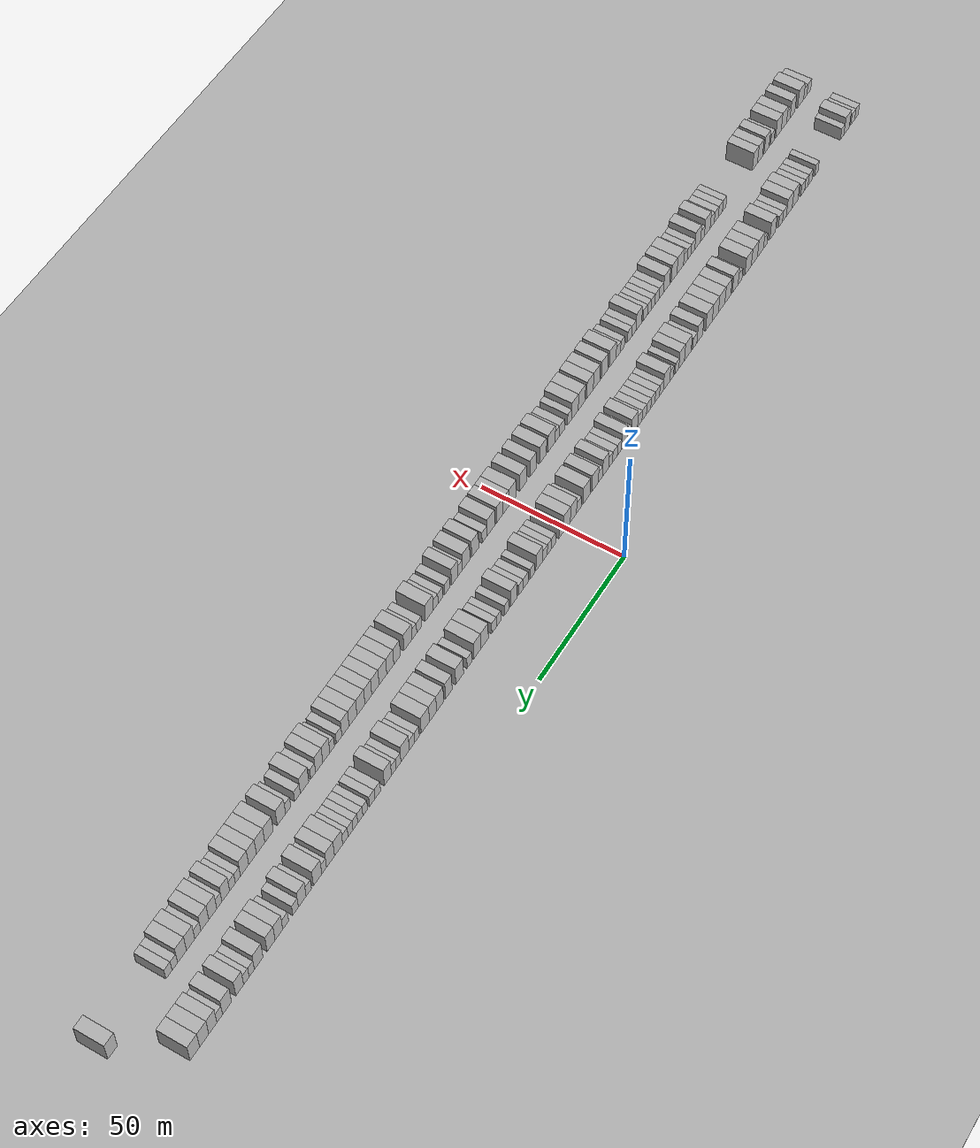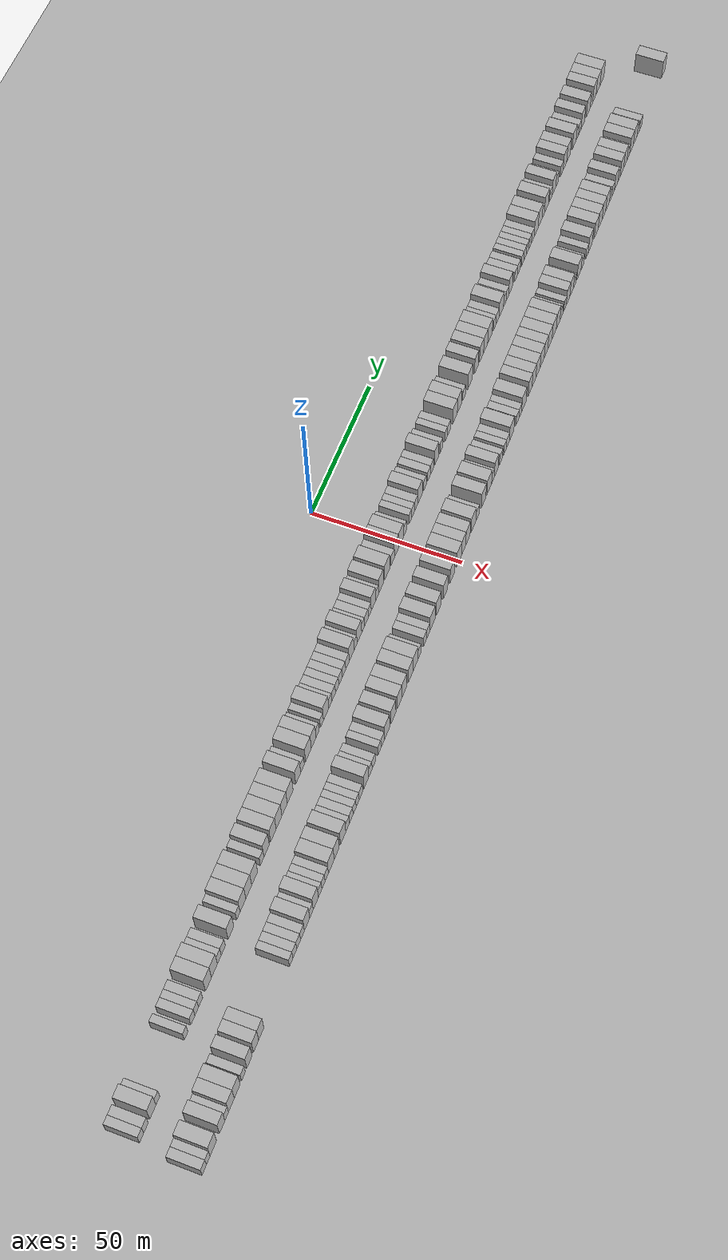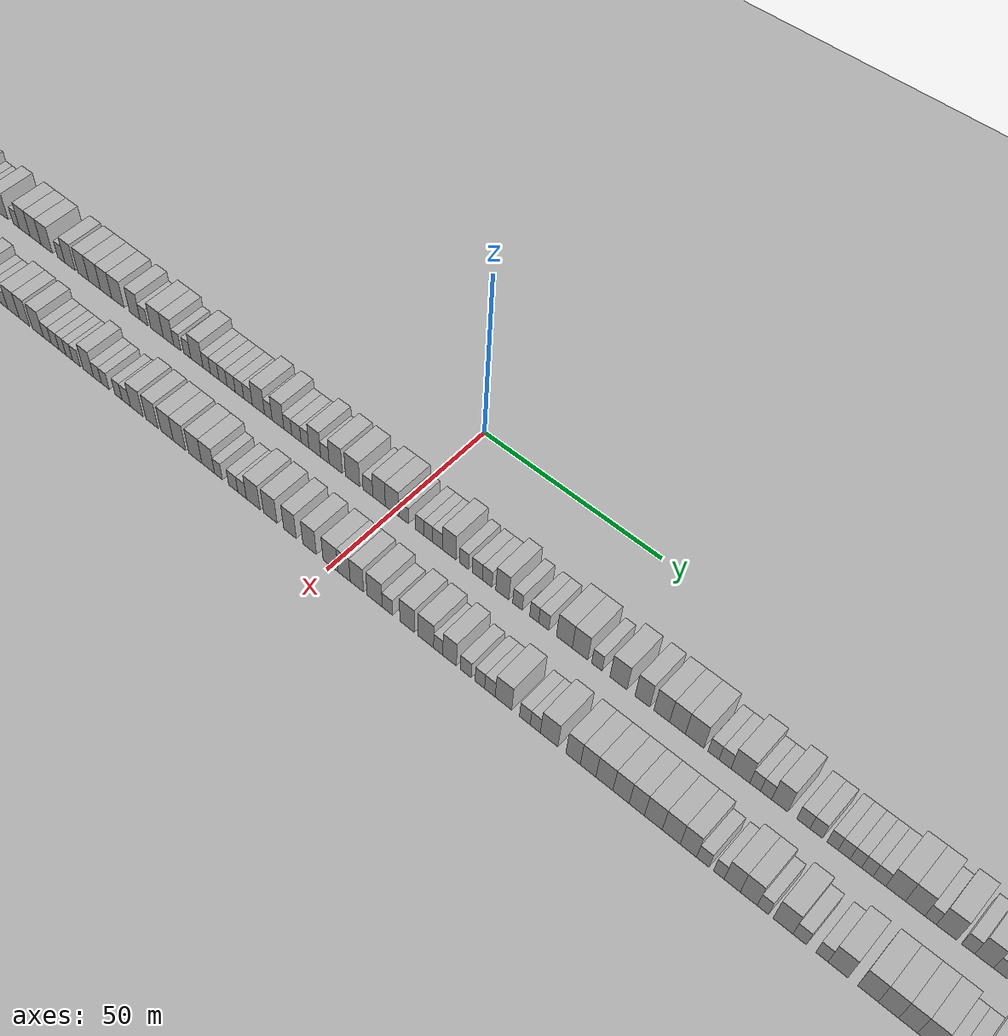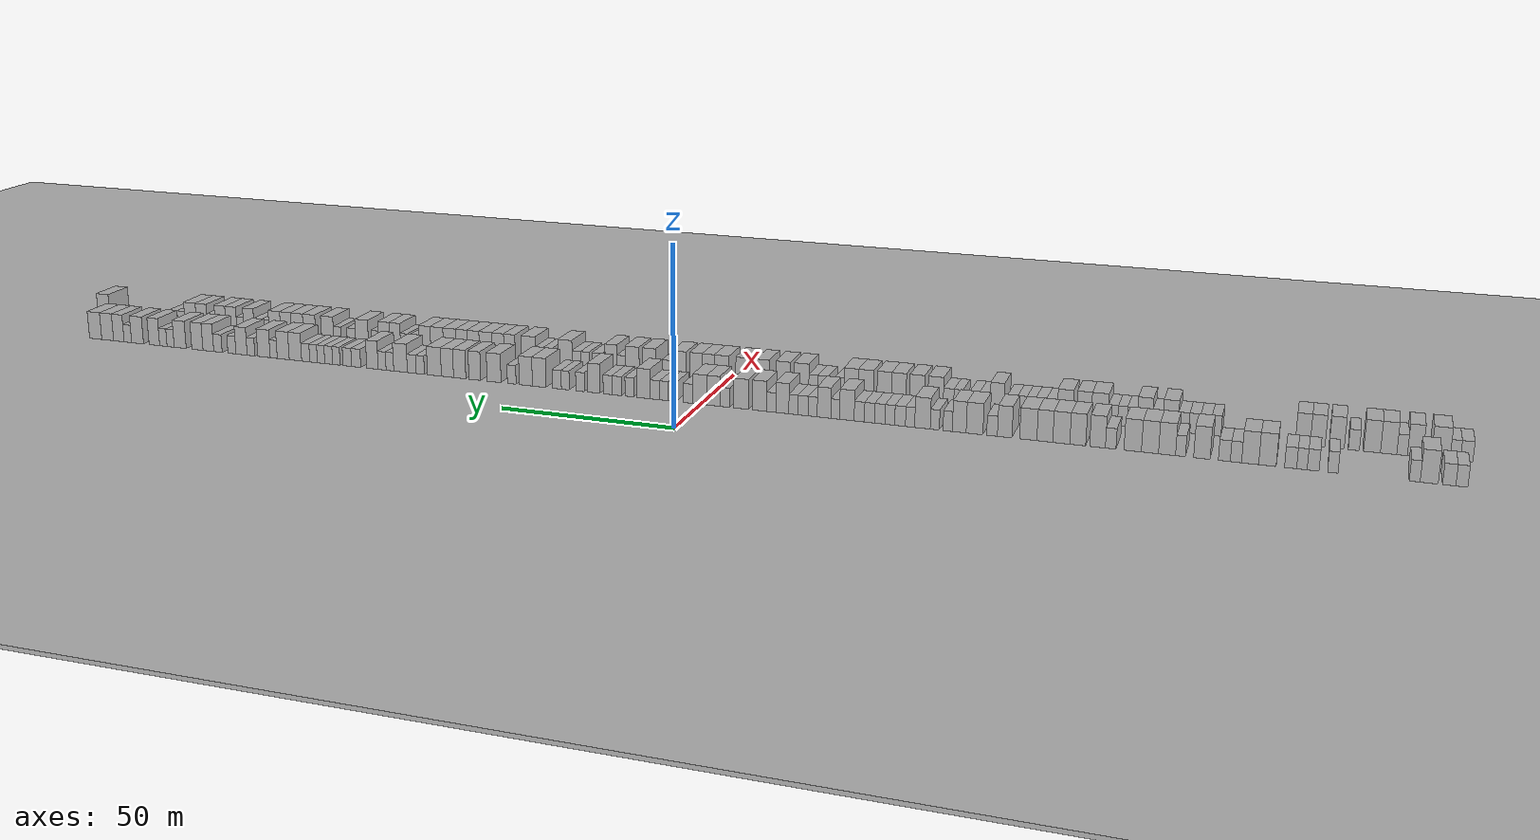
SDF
<?xml version="1.0" encoding="utf-8"?>

<sdf version="1.6">

   <world name="default">

      <gui fullscreen="0">

         <camera name="user_camera">

            <pose>-15 0 4.57585 0 0 0</pose>

            <view_controller>orbit</view_controller>

         </camera>

      </gui>

      <scene>

         <sky>

           <clouds>

             <speed>12</speed>

           </clouds>

         </sky>

         <ambient>0.4 0.4 0.4 1</ambient>

         <background>0.7 0.7 0.7 1</background>

         <shadows>1</shadows>

      </scene>

      <gravity>0 0 -9.8066</gravity>

      <magnetic_field>6e-06 2.3e-05 -4.2e-05</magnetic_field>

      <physics default="0" name="default_physics" type="ode">

         <ode>

            <solver>

               <type>quick</type>

               <iters>10</iters>

               <sor>1.0</sor>

               <use_dynamic_moi_rescaling>0</use_dynamic_moi_rescaling>

            </solver>

            <constraints>

               <cfm>0</cfm>

               <erp>0.2</erp>

               <contact_max_correcting_vel>100</contact_max_correcting_vel>

               <contact_surface_layer>0.001</contact_surface_layer>

            </constraints>

         </ode>

         <max_step_size>0.004</max_step_size>

         <real_time_factor>1</real_time_factor>

         <real_time_update_rate>250</real_time_update_rate>

      </physics>

      <light name="sun" type="directional">

         <cast_shadows>1</cast_shadows>

         <pose>0 0 10 0 0 0</pose>

         <diffuse>0.8 0.8 0.8 1</diffuse>

         <specular>0.2 0.2 0.2 1</specular>

         <attenuation>

            <range>1000</range>

            <constant>0.9</constant>

            <linear>0.01</linear>

            <quadratic>0.001</quadratic>

         </attenuation>

         <direction>-0.5 0.1 -0.9</direction>

      </light>

      <include>

         <name>ground_plane_1</name>

         <uri>model://HANNAS_ground_plane</uri>

         <pose>0 0 0  0 0 0</pose>

      </include>

      <include>

         <name>ground_plane_2</name>

         <uri>model://HANNAS_ground_plane</uri>

         <pose>100 0 0  0 0 0</pose>

      </include>

      <model name="building_1">

         <static>1</static>

         <pose frame="">25.0000 -194.6447 0 0.000000 0.000000 0.000000</pose>

         <link name="link">

            <pose frame="">0 0 3.00 0 0 0</pose>

            <collision name="collision">

               <geometry>

                  <box>

                     <size>10.0000 2.7106 6.0000</size>

                  </box>

               </geometry>

               <max_contacts>10</max_contacts>

               <surface>

                  <contact>

                     <ode/>

                  </contact>

                  <bounce/>

                  <friction>

                     <torsional>

                        <ode/>

                     </torsional>

                     <ode/>

                  </friction>

               </surface>

            </collision>

            <visual name="visual">

               <cast_shadows>0</cast_shadows>

               <geometry>

                  <box>

                     <size>10.0000 2.7106 6.0000</size>

                  </box>

               </geometry>

               <material>

                  <script>

                     <uri>model://HANNAS_wall/materials/scripts</uri>

                     <uri>model://HANNAS_wall/materials/textures</uri>

                     <name>vrc/HANNAS_wall</name>

                  </script>

               </material>

            </visual>

            <self_collide>0</self_collide>

            <enable_wind>0</enable_wind>

            <kinematic>0</kinematic>

         </link>

      </model>

      <model name="building_2">

         <static>1</static>

         <pose frame="">25.0000 -191.7946 0 0.000000 0.000000 0.000000</pose>

         <link name="link">

            <pose frame="">0 0 3.00 0 0 0</pose>

            <collision name="collision">

               <geometry>

                  <box>

                     <size>10.0000 2.9896 6.0000</size>

                  </box>

               </geometry>

               <max_contacts>10</max_contacts>

               <surface>

                  <contact>

                     <ode/>

                  </contact>

                  <bounce/>

                  <friction>

                     <torsional>

                        <ode/>

                     </torsional>

                     <ode/>

                  </friction>

               </surface>

            </collision>

            <visual name="visual">

               <cast_shadows>0</cast_shadows>

               <geometry>

                  <box>

                     <size>10.0000 2.9896 6.0000</size>

                  </box>

               </geometry>

               <material>

                  <script>

                     <uri>model://HANNAS_wall/materials/scripts</uri>

                     <uri>model://HANNAS_wall/materials/textures</uri>

                     <name>vrc/HANNAS_wall</name>

                  </script>

               </material>

            </visual>

            <self_collide>0</self_collide>

            <enable_wind>0</enable_wind>

            <kinematic>0</kinematic>

         </link>

      </model>

      <model name="building_3">

         <static>1</static>

         <pose frame="">25.0000 -187.2565 0 0.000000 0.000000 0.000000</pose>

         <link name="link">

            <pose frame="">0 0 4.50 0 0 0</pose>

            <collision name="collision">

               <geometry>

                  <box>

                     <size>10.0000 4.0864 9.0000</size>

                  </box>

               </geometry>

               <max_contacts>10</max_contacts>

               <surface>

                  <contact>

                     <ode/>

                  </contact>

                  <bounce/>

                  <friction>

                     <torsional>

                        <ode/>

                     </torsional>

                     <ode/>

                  </friction>

               </surface>

            </collision>

            <visual name="visual">

               <cast_shadows>0</cast_shadows>

               <geometry>

                  <box>

                     <size>10.0000 4.0864 9.0000</size>

                  </box>

               </geometry>

               <material>

                  <script>

                     <uri>model://HANNAS_wall/materials/scripts</uri>

                     <uri>model://HANNAS_wall/materials/textures</uri>

                     <name>vrc/HANNAS_wall</name>

                  </script>

               </material>

            </visual>

            <self_collide>0</self_collide>

            <enable_wind>0</enable_wind>

            <kinematic>0</kinematic>

         </link>

      </model>

      <model name="building_4">

         <static>1</static>

         <pose frame="">25.0000 -183.9715 0 0.000000 0.000000 0.000000</pose>

         <link name="link">

            <pose frame="">0 0 3.00 0 0 0</pose>

            <collision name="collision">

               <geometry>

                  <box>

                     <size>10.0000 2.4836 6.0000</size>

                  </box>

               </geometry>

               <max_contacts>10</max_contacts>

               <surface>

                  <contact>

                     <ode/>

                  </contact>

                  <bounce/>

                  <friction>

                     <torsional>

                        <ode/>

                     </torsional>

                     <ode/>

                  </friction>

               </surface>

            </collision>

            <visual name="visual">

               <cast_shadows>0</cast_shadows>

               <geometry>

                  <box>

                     <size>10.0000 2.4836 6.0000</size>

                  </box>

               </geometry>

               <material>

                  <script>

                     <uri>model://HANNAS_wall/materials/scripts</uri>

                     <uri>model://HANNAS_wall/materials/textures</uri>

                     <name>vrc/HANNAS_wall</name>

                  </script>

               </material>

            </visual>

            <self_collide>0</self_collide>

            <enable_wind>0</enable_wind>

            <kinematic>0</kinematic>

         </link>

      </model>

      <model name="building_5">

         <static>1</static>

         <pose frame="">25.0000 -165.0640 0 0.000000 0.000000 0.000000</pose>

         <link name="link">

            <pose frame="">0 0 3.00 0 0 0</pose>

            <collision name="collision">

               <geometry>

                  <box>

                     <size>10.0000 2.4438 6.0000</size>

                  </box>

               </geometry>

               <max_contacts>10</max_contacts>

               <surface>

                  <contact>

                     <ode/>

                  </contact>

                  <bounce/>

                  <friction>

                     <torsional>

                        <ode/>

                     </torsional>

                     <ode/>

                  </friction>

               </surface>

            </collision>

            <visual name="visual">

               <cast_shadows>0</cast_shadows>

               <geometry>

                  <box>

                     <size>10.0000 2.4438 6.0000</size>

                  </box>

               </geometry>

               <material>

                  <script>

                     <uri>model://HANNAS_wall/materials/scripts</uri>

                     <uri>model://HANNAS_wall/materials/textures</uri>

                     <name>vrc/HANNAS_wall</name>

                  </script>

               </material>

            </visual>

            <self_collide>0</self_collide>

            <enable_wind>0</enable_wind>

            <kinematic>0</kinematic>

         </link>

      </model>

      <model name="building_6">

         <static>1</static>

         <pose frame="">25.0000 -160.4400 0 0.000000 0.000000 0.000000</pose>

         <link name="link">

            <pose frame="">0 0 3.00 0 0 0</pose>

            <collision name="collision">

               <geometry>

                  <box>

                     <size>10.0000 2.8041 6.0000</size>

                  </box>

               </geometry>

               <max_contacts>10</max_contacts>

               <surface>

                  <contact>

                     <ode/>

                  </contact>

                  <bounce/>

                  <friction>

                     <torsional>

                        <ode/>

                     </torsional>

                     <ode/>

                  </friction>

               </surface>

            </collision>

            <visual name="visual">

               <cast_shadows>0</cast_shadows>

               <geometry>

                  <box>

                     <size>10.0000 2.8041 6.0000</size>

                  </box>

               </geometry>

               <material>

                  <script>

                     <uri>model://HANNAS_wall/materials/scripts</uri>

                     <uri>model://HANNAS_wall/materials/textures</uri>

                     <name>vrc/HANNAS_wall</name>

                  </script>

               </material>

            </visual>

            <self_collide>0</self_collide>

            <enable_wind>0</enable_wind>

            <kinematic>0</kinematic>

         </link>

      </model>

      <model name="building_7">

         <static>1</static>

         <pose frame="">25.0000 -157.7915 0 0.000000 0.000000 0.000000</pose>

         <link name="link">

            <pose frame="">0 0 3.00 0 0 0</pose>

            <collision name="collision">

               <geometry>

                  <box>

                     <size>10.0000 2.4929 6.0000</size>

                  </box>

               </geometry>

               <max_contacts>10</max_contacts>

               <surface>

                  <contact>

                     <ode/>

                  </contact>

                  <bounce/>

                  <friction>

                     <torsional>

                        <ode/>

                     </torsional>

                     <ode/>

                  </friction>

               </surface>

            </collision>

            <visual name="visual">

               <cast_shadows>0</cast_shadows>

               <geometry>

                  <box>

                     <size>10.0000 2.4929 6.0000</size>

                  </box>

               </geometry>

               <material>

                  <script>

                     <uri>model://HANNAS_wall/materials/scripts</uri>

                     <uri>model://HANNAS_wall/materials/textures</uri>

                     <name>vrc/HANNAS_wall</name>

                  </script>

               </material>

            </visual>

            <self_collide>0</self_collide>

            <enable_wind>0</enable_wind>

            <kinematic>0</kinematic>

         </link>

      </model>

      <model name="building_8">

         <static>1</static>

         <pose frame="">25.0000 -155.1140 0 0.000000 0.000000 0.000000</pose>

         <link name="link">

            <pose frame="">0 0 3.00 0 0 0</pose>

            <collision name="collision">

               <geometry>

                  <box>

                     <size>10.0000 2.8622 6.0000</size>

                  </box>

               </geometry>

               <max_contacts>10</max_contacts>

               <surface>

                  <contact>

                     <ode/>

                  </contact>

                  <bounce/>

                  <friction>

                     <torsional>

                        <ode/>

                     </torsional>

                     <ode/>

                  </friction>

               </surface>

            </collision>

            <visual name="visual">

               <cast_shadows>0</cast_shadows>

               <geometry>

                  <box>

                     <size>10.0000 2.8622 6.0000</size>

                  </box>

               </geometry>

               <material>

                  <script>

                     <uri>model://HANNAS_wall/materials/scripts</uri>

                     <uri>model://HANNAS_wall/materials/textures</uri>

                     <name>vrc/HANNAS_wall</name>

                  </script>

               </material>

            </visual>

            <self_collide>0</self_collide>

            <enable_wind>0</enable_wind>

            <kinematic>0</kinematic>

         </link>

      </model>

      <model name="building_9">

         <static>1</static>

         <pose frame="">25.0000 -149.5959 0 0.000000 0.000000 0.000000</pose>

         <link name="link">

            <pose frame="">0 0 4.50 0 0 0</pose>

            <collision name="collision">

               <geometry>

                  <box>

                     <size>10.0000 4.1739 9.0000</size>

                  </box>

               </geometry>

               <max_contacts>10</max_contacts>

               <surface>

                  <contact>

                     <ode/>

                  </contact>

                  <bounce/>

                  <friction>

                     <torsional>

                        <ode/>

                     </torsional>

                     <ode/>

                  </friction>

               </surface>

            </collision>

            <visual name="visual">

               <cast_shadows>0</cast_shadows>

               <geometry>

                  <box>

                     <size>10.0000 4.1739 9.0000</size>

                  </box>

               </geometry>

               <material>

                  <script>

                     <uri>model://HANNAS_wall/materials/scripts</uri>

                     <uri>model://HANNAS_wall/materials/textures</uri>

                     <name>vrc/HANNAS_wall</name>

                  </script>

               </material>

            </visual>

            <self_collide>0</self_collide>

            <enable_wind>0</enable_wind>

            <kinematic>0</kinematic>

         </link>

      </model>

      <model name="building_10">

         <static>1</static>

         <pose frame="">25.0000 -145.4531 0 0.000000 0.000000 0.000000</pose>

         <link name="link">

            <pose frame="">0 0 4.50 0 0 0</pose>

            <collision name="collision">

               <geometry>

                  <box>

                     <size>10.0000 4.1118 9.0000</size>

                  </box>

               </geometry>

               <max_contacts>10</max_contacts>

               <surface>

                  <contact>

                     <ode/>

                  </contact>

                  <bounce/>

                  <friction>

                     <torsional>

                        <ode/>

                     </torsional>

                     <ode/>

                  </friction>

               </surface>

            </collision>

            <visual name="visual">

               <cast_shadows>0</cast_shadows>

               <geometry>

                  <box>

                     <size>10.0000 4.1118 9.0000</size>

                  </box>

               </geometry>

               <material>

                  <script>

                     <uri>model://HANNAS_wall/materials/scripts</uri>

                     <uri>model://HANNAS_wall/materials/textures</uri>

                     <name>vrc/HANNAS_wall</name>

                  </script>

               </material>

            </visual>

            <self_collide>0</self_collide>

            <enable_wind>0</enable_wind>

            <kinematic>0</kinematic>

         </link>

      </model>

      <model name="building_11">

         <static>1</static>

         <pose frame="">25.0000 -142.0381 0 0.000000 0.000000 0.000000</pose>

         <link name="link">

            <pose frame="">0 0 3.00 0 0 0</pose>

            <collision name="collision">

               <geometry>

                  <box>

                     <size>10.0000 2.7182 6.0000</size>

                  </box>

               </geometry>

               <max_contacts>10</max_contacts>

               <surface>

                  <contact>

                     <ode/>

                  </contact>

                  <bounce/>

                  <friction>

                     <torsional>

                        <ode/>

                     </torsional>

                     <ode/>

                  </friction>

               </surface>

            </collision>

            <visual name="visual">

               <cast_shadows>0</cast_shadows>

               <geometry>

                  <box>

                     <size>10.0000 2.7182 6.0000</size>

                  </box>

               </geometry>

               <material>

                  <script>

                     <uri>model://HANNAS_wall/materials/scripts</uri>

                     <uri>model://HANNAS_wall/materials/textures</uri>

                     <name>vrc/HANNAS_wall</name>

                  </script>

               </material>

            </visual>

            <self_collide>0</self_collide>

            <enable_wind>0</enable_wind>

            <kinematic>0</kinematic>

         </link>

      </model>

      <model name="building_12">

         <static>1</static>

         <pose frame="">25.0000 -139.2262 0 0.000000 0.000000 0.000000</pose>

         <link name="link">

            <pose frame="">0 0 3.00 0 0 0</pose>

            <collision name="collision">

               <geometry>

                  <box>

                     <size>10.0000 2.9058 6.0000</size>

                  </box>

               </geometry>

               <max_contacts>10</max_contacts>

               <surface>

                  <contact>

                     <ode/>

                  </contact>

                  <bounce/>

                  <friction>

                     <torsional>

                        <ode/>

                     </torsional>

                     <ode/>

                  </friction>

               </surface>

            </collision>

            <visual name="visual">

               <cast_shadows>0</cast_shadows>

               <geometry>

                  <box>

                     <size>10.0000 2.9058 6.0000</size>

                  </box>

               </geometry>

               <material>

                  <script>

                     <uri>model://HANNAS_wall/materials/scripts</uri>

                     <uri>model://HANNAS_wall/materials/textures</uri>

                     <name>vrc/HANNAS_wall</name>

                  </script>

               </material>

            </visual>

            <self_collide>0</self_collide>

            <enable_wind>0</enable_wind>

            <kinematic>0</kinematic>

         </link>

      </model>

      <model name="building_13">

         <static>1</static>

         <pose frame="">25.0000 -133.7597 0 0.000000 0.000000 0.000000</pose>

         <link name="link">

            <pose frame="">0 0 4.50 0 0 0</pose>

            <collision name="collision">

               <geometry>

                  <box>

                     <size>10.0000 4.0272 9.0000</size>

                  </box>

               </geometry>

               <max_contacts>10</max_contacts>

               <surface>

                  <contact>

                     <ode/>

                  </contact>

                  <bounce/>

                  <friction>

                     <torsional>

                        <ode/>

                     </torsional>

                     <ode/>

                  </friction>

               </surface>

            </collision>

            <visual name="visual">

               <cast_shadows>0</cast_shadows>

               <geometry>

                  <box>

                     <size>10.0000 4.0272 9.0000</size>

                  </box>

               </geometry>

               <material>

                  <script>

                     <uri>model://HANNAS_wall/materials/scripts</uri>

                     <uri>model://HANNAS_wall/materials/textures</uri>

                     <name>vrc/HANNAS_wall</name>

                  </script>

               </material>

            </visual>

            <self_collide>0</self_collide>

            <enable_wind>0</enable_wind>

            <kinematic>0</kinematic>

         </link>

      </model>

      <model name="building_14">

         <static>1</static>

         <pose frame="">25.0000 -128.5231 0 0.000000 0.000000 0.000000</pose>

         <link name="link">

            <pose frame="">0 0 3.00 0 0 0</pose>

            <collision name="collision">

               <geometry>

                  <box>

                     <size>10.0000 2.4459 6.0000</size>

                  </box>

               </geometry>

               <max_contacts>10</max_contacts>

               <surface>

                  <contact>

                     <ode/>

                  </contact>

                  <bounce/>

                  <friction>

                     <torsional>

                        <ode/>

                     </torsional>

                     <ode/>

                  </friction>

               </surface>

            </collision>

            <visual name="visual">

               <cast_shadows>0</cast_shadows>

               <geometry>

                  <box>

                     <size>10.0000 2.4459 6.0000</size>

                  </box>

               </geometry>

               <material>

                  <script>

                     <uri>model://HANNAS_wall/materials/scripts</uri>

                     <uri>model://HANNAS_wall/materials/textures</uri>

                     <name>vrc/HANNAS_wall</name>

                  </script>

               </material>

            </visual>

            <self_collide>0</self_collide>

            <enable_wind>0</enable_wind>

            <kinematic>0</kinematic>

         </link>

      </model>

      <model name="building_15">

         <static>1</static>

         <pose frame="">25.0000 -125.1942 0 0.000000 0.000000 0.000000</pose>

         <link name="link">

            <pose frame="">0 0 4.50 0 0 0</pose>

            <collision name="collision">

               <geometry>

                  <box>

                     <size>10.0000 4.2118 9.0000</size>

                  </box>

               </geometry>

               <max_contacts>10</max_contacts>

               <surface>

                  <contact>

                     <ode/>

                  </contact>

                  <bounce/>

                  <friction>

                     <torsional>

                        <ode/>

                     </torsional>

                     <ode/>

                  </friction>

               </surface>

            </collision>

            <visual name="visual">

               <cast_shadows>0</cast_shadows>

               <geometry>

                  <box>

                     <size>10.0000 4.2118 9.0000</size>

                  </box>

               </geometry>

               <material>

                  <script>

                     <uri>model://HANNAS_wall/materials/scripts</uri>

                     <uri>model://HANNAS_wall/materials/textures</uri>

                     <name>vrc/HANNAS_wall</name>

                  </script>

               </material>

            </visual>

            <self_collide>0</self_collide>

            <enable_wind>0</enable_wind>

            <kinematic>0</kinematic>

         </link>

      </model>

      <model name="building_16">

         <static>1</static>

         <pose frame="">25.0000 -120.9669 0 0.000000 0.000000 0.000000</pose>

         <link name="link">

            <pose frame="">0 0 4.50 0 0 0</pose>

            <collision name="collision">

               <geometry>

                  <box>

                     <size>10.0000 4.2428 9.0000</size>

                  </box>

               </geometry>

               <max_contacts>10</max_contacts>

               <surface>

                  <contact>

                     <ode/>

                  </contact>

                  <bounce/>

                  <friction>

                     <torsional>

                        <ode/>

                     </torsional>

                     <ode/>

                  </friction>

               </surface>

            </collision>

            <visual name="visual">

               <cast_shadows>0</cast_shadows>

               <geometry>

                  <box>

                     <size>10.0000 4.2428 9.0000</size>

                  </box>

               </geometry>

               <material>

                  <script>

                     <uri>model://HANNAS_wall/materials/scripts</uri>

                     <uri>model://HANNAS_wall/materials/textures</uri>

                     <name>vrc/HANNAS_wall</name>

                  </script>

               </material>

            </visual>

            <self_collide>0</self_collide>

            <enable_wind>0</enable_wind>

            <kinematic>0</kinematic>

         </link>

      </model>

      <model name="building_17">

         <static>1</static>

         <pose frame="">25.0000 -116.6630 0 0.000000 0.000000 0.000000</pose>

         <link name="link">

            <pose frame="">0 0 4.50 0 0 0</pose>

            <collision name="collision">

               <geometry>

                  <box>

                     <size>10.0000 4.3650 9.0000</size>

                  </box>

               </geometry>

               <max_contacts>10</max_contacts>

               <surface>

                  <contact>

                     <ode/>

                  </contact>

                  <bounce/>

                  <friction>

                     <torsional>

                        <ode/>

                     </torsional>

                     <ode/>

                  </friction>

               </surface>

            </collision>

            <visual name="visual">

               <cast_shadows>0</cast_shadows>

               <geometry>

                  <box>

                     <size>10.0000 4.3650 9.0000</size>

                  </box>

               </geometry>

               <material>

                  <script>

                     <uri>model://HANNAS_wall/materials/scripts</uri>

                     <uri>model://HANNAS_wall/materials/textures</uri>

                     <name>vrc/HANNAS_wall</name>

                  </script>

               </material>

            </visual>

            <self_collide>0</self_collide>

            <enable_wind>0</enable_wind>

            <kinematic>0</kinematic>

         </link>

      </model>

      <model name="building_18">

         <static>1</static>

         <pose frame="">25.0000 -111.1464 0 0.000000 0.000000 0.000000</pose>

         <link name="link">

            <pose frame="">0 0 3.00 0 0 0</pose>

            <collision name="collision">

               <geometry>

                  <box>

                     <size>10.0000 2.6683 6.0000</size>

                  </box>

               </geometry>

               <max_contacts>10</max_contacts>

               <surface>

                  <contact>

                     <ode/>

                  </contact>

                  <bounce/>

                  <friction>

                     <torsional>

                        <ode/>

                     </torsional>

                     <ode/>

                  </friction>

               </surface>

            </collision>

            <visual name="visual">

               <cast_shadows>0</cast_shadows>

               <geometry>

                  <box>

                     <size>10.0000 2.6683 6.0000</size>

                  </box>

               </geometry>

               <material>

                  <script>

                     <uri>model://HANNAS_wall/materials/scripts</uri>

                     <uri>model://HANNAS_wall/materials/textures</uri>

                     <name>vrc/HANNAS_wall</name>

                  </script>

               </material>

            </visual>

            <self_collide>0</self_collide>

            <enable_wind>0</enable_wind>

            <kinematic>0</kinematic>

         </link>

      </model>

      <model name="building_19">

         <static>1</static>

         <pose frame="">25.0000 -107.8260 0 0.000000 0.000000 0.000000</pose>

         <link name="link">

            <pose frame="">0 0 4.50 0 0 0</pose>

            <collision name="collision">

               <geometry>

                  <box>

                     <size>10.0000 3.9724 9.0000</size>

                  </box>

               </geometry>

               <max_contacts>10</max_contacts>

               <surface>

                  <contact>

                     <ode/>

                  </contact>

                  <bounce/>

                  <friction>

                     <torsional>

                        <ode/>

                     </torsional>

                     <ode/>

                  </friction>

               </surface>

            </collision>

            <visual name="visual">

               <cast_shadows>0</cast_shadows>

               <geometry>

                  <box>

                     <size>10.0000 3.9724 9.0000</size>

                  </box>

               </geometry>

               <material>

                  <script>

                     <uri>model://HANNAS_wall/materials/scripts</uri>

                     <uri>model://HANNAS_wall/materials/textures</uri>

                     <name>vrc/HANNAS_wall</name>

                  </script>

               </material>

            </visual>

            <self_collide>0</self_collide>

            <enable_wind>0</enable_wind>

            <kinematic>0</kinematic>

         </link>

      </model>

      <model name="building_20">

         <static>1</static>

         <pose frame="">25.0000 -102.8106 0 0.000000 0.000000 0.000000</pose>

         <link name="link">

            <pose frame="">0 0 4.50 0 0 0</pose>

            <collision name="collision">

               <geometry>

                  <box>

                     <size>10.0000 4.0584 9.0000</size>

                  </box>

               </geometry>

               <max_contacts>10</max_contacts>

               <surface>

                  <contact>

                     <ode/>

                  </contact>

                  <bounce/>

                  <friction>

                     <torsional>

                        <ode/>

                     </torsional>

                     <ode/>

                  </friction>

               </surface>

            </collision>

            <visual name="visual">

               <cast_shadows>0</cast_shadows>

               <geometry>

                  <box>

                     <size>10.0000 4.0584 9.0000</size>

                  </box>

               </geometry>

               <material>

                  <script>

                     <uri>model://HANNAS_wall/materials/scripts</uri>

                     <uri>model://HANNAS_wall/materials/textures</uri>

                     <name>vrc/HANNAS_wall</name>

                  </script>

               </material>

            </visual>

            <self_collide>0</self_collide>

            <enable_wind>0</enable_wind>

            <kinematic>0</kinematic>

         </link>

      </model>

      <model name="building_21">

         <static>1</static>

         <pose frame="">25.0000 -98.6065 0 0.000000 0.000000 0.000000</pose>

         <link name="link">

            <pose frame="">0 0 4.50 0 0 0</pose>

            <collision name="collision">

               <geometry>

                  <box>

                     <size>10.0000 4.3498 9.0000</size>

                  </box>

               </geometry>

               <max_contacts>10</max_contacts>

               <surface>

                  <contact>

                     <ode/>

                  </contact>

                  <bounce/>

                  <friction>

                     <torsional>

                        <ode/>

                     </torsional>

                     <ode/>

                  </friction>

               </surface>

            </collision>

            <visual name="visual">

               <cast_shadows>0</cast_shadows>

               <geometry>

                  <box>

                     <size>10.0000 4.3498 9.0000</size>

                  </box>

               </geometry>

               <material>

                  <script>

                     <uri>model://HANNAS_wall/materials/scripts</uri>

                     <uri>model://HANNAS_wall/materials/textures</uri>

                     <name>vrc/HANNAS_wall</name>

                  </script>

               </material>

            </visual>

            <self_collide>0</self_collide>

            <enable_wind>0</enable_wind>

            <kinematic>0</kinematic>

         </link>

      </model>

      <model name="building_22">

         <static>1</static>

         <pose frame="">25.0000 -94.3852 0 0.000000 0.000000 0.000000</pose>

         <link name="link">

            <pose frame="">0 0 4.50 0 0 0</pose>

            <collision name="collision">

               <geometry>

                  <box>

                     <size>10.0000 4.0928 9.0000</size>

                  </box>

               </geometry>

               <max_contacts>10</max_contacts>

               <surface>

                  <contact>

                     <ode/>

                  </contact>

                  <bounce/>

                  <friction>

                     <torsional>

                        <ode/>

                     </torsional>

                     <ode/>

                  </friction>

               </surface>

            </collision>

            <visual name="visual">

               <cast_shadows>0</cast_shadows>

               <geometry>

                  <box>

                     <size>10.0000 4.0928 9.0000</size>

                  </box>

               </geometry>

               <material>

                  <script>

                     <uri>model://HANNAS_wall/materials/scripts</uri>

                     <uri>model://HANNAS_wall/materials/textures</uri>

                     <name>vrc/HANNAS_wall</name>

                  </script>

               </material>

            </visual>

            <self_collide>0</self_collide>

            <enable_wind>0</enable_wind>

            <kinematic>0</kinematic>

         </link>

      </model>

      <model name="building_23">

         <static>1</static>

         <pose frame="">25.0000 -90.1121 0 0.000000 0.000000 0.000000</pose>

         <link name="link">

            <pose frame="">0 0 4.50 0 0 0</pose>

            <collision name="collision">

               <geometry>

                  <box>

                     <size>10.0000 4.4532 9.0000</size>

                  </box>

               </geometry>

               <max_contacts>10</max_contacts>

               <surface>

                  <contact>

                     <ode/>

                  </contact>

                  <bounce/>

                  <friction>

                     <torsional>

                        <ode/>

                     </torsional>

                     <ode/>

                  </friction>

               </surface>

            </collision>

            <visual name="visual">

               <cast_shadows>0</cast_shadows>

               <geometry>

                  <box>

                     <size>10.0000 4.4532 9.0000</size>

                  </box>

               </geometry>

               <material>

                  <script>

                     <uri>model://HANNAS_wall/materials/scripts</uri>

                     <uri>model://HANNAS_wall/materials/textures</uri>

                     <name>vrc/HANNAS_wall</name>

                  </script>

               </material>

            </visual>

            <self_collide>0</self_collide>

            <enable_wind>0</enable_wind>

            <kinematic>0</kinematic>

         </link>

      </model>

      <model name="building_24">

         <static>1</static>

         <pose frame="">25.0000 -83.9858 0 0.000000 0.000000 0.000000</pose>

         <link name="link">

            <pose frame="">0 0 4.50 0 0 0</pose>

            <collision name="collision">

               <geometry>

                  <box>

                     <size>10.0000 3.7995 9.0000</size>

                  </box>

               </geometry>

               <max_contacts>10</max_contacts>

               <surface>

                  <contact>

                     <ode/>

                  </contact>

                  <bounce/>

                  <friction>

                     <torsional>

                        <ode/>

                     </torsional>

                     <ode/>

                  </friction>

               </surface>

            </collision>

            <visual name="visual">

               <cast_shadows>0</cast_shadows>

               <geometry>

                  <box>

                     <size>10.0000 3.7995 9.0000</size>

                  </box>

               </geometry>

               <material>

                  <script>

                     <uri>model://HANNAS_wall/materials/scripts</uri>

                     <uri>model://HANNAS_wall/materials/textures</uri>

                     <name>vrc/HANNAS_wall</name>

                  </script>

               </material>

            </visual>

            <self_collide>0</self_collide>

            <enable_wind>0</enable_wind>

            <kinematic>0</kinematic>

         </link>

      </model>

      <model name="building_25">

         <static>1</static>

         <pose frame="">25.0000 -80.6869 0 0.000000 0.000000 0.000000</pose>

         <link name="link">

            <pose frame="">0 0 3.00 0 0 0</pose>

            <collision name="collision">

               <geometry>

                  <box>

                     <size>10.0000 2.7982 6.0000</size>

                  </box>

               </geometry>

               <max_contacts>10</max_contacts>

               <surface>

                  <contact>

                     <ode/>

                  </contact>

                  <bounce/>

                  <friction>

                     <torsional>

                        <ode/>

                     </torsional>

                     <ode/>

                  </friction>

               </surface>

            </collision>

            <visual name="visual">

               <cast_shadows>0</cast_shadows>

               <geometry>

                  <box>

                     <size>10.0000 2.7982 6.0000</size>

                  </box>

               </geometry>

               <material>

                  <script>

                     <uri>model://HANNAS_wall/materials/scripts</uri>

                     <uri>model://HANNAS_wall/materials/textures</uri>

                     <name>vrc/HANNAS_wall</name>

                  </script>

               </material>

            </visual>

            <self_collide>0</self_collide>

            <enable_wind>0</enable_wind>

            <kinematic>0</kinematic>

         </link>

      </model>

      <model name="building_26">

         <static>1</static>

         <pose frame="">25.0000 -76.0856 0 0.000000 0.000000 0.000000</pose>

         <link name="link">

            <pose frame="">0 0 4.50 0 0 0</pose>

            <collision name="collision">

               <geometry>

                  <box>

                     <size>10.0000 4.4045 9.0000</size>

                  </box>

               </geometry>

               <max_contacts>10</max_contacts>

               <surface>

                  <contact>

                     <ode/>

                  </contact>

                  <bounce/>

                  <friction>

                     <torsional>

                        <ode/>

                     </torsional>

                     <ode/>

                  </friction>

               </surface>

            </collision>

            <visual name="visual">

               <cast_shadows>0</cast_shadows>

               <geometry>

                  <box>

                     <size>10.0000 4.4045 9.0000</size>

                  </box>

               </geometry>

               <material>

                  <script>

                     <uri>model://HANNAS_wall/materials/scripts</uri>

                     <uri>model://HANNAS_wall/materials/textures</uri>

                     <name>vrc/HANNAS_wall</name>

                  </script>

               </material>

            </visual>

            <self_collide>0</self_collide>

            <enable_wind>0</enable_wind>

            <kinematic>0</kinematic>

         </link>

      </model>

      <model name="building_27">

         <static>1</static>

         <pose frame="">25.0000 -72.0492 0 0.000000 0.000000 0.000000</pose>

         <link name="link">

            <pose frame="">0 0 4.50 0 0 0</pose>

            <collision name="collision">

               <geometry>

                  <box>

                     <size>10.0000 3.6683 9.0000</size>

                  </box>

               </geometry>

               <max_contacts>10</max_contacts>

               <surface>

                  <contact>

                     <ode/>

                  </contact>

                  <bounce/>

                  <friction>

                     <torsional>

                        <ode/>

                     </torsional>

                     <ode/>

                  </friction>

               </surface>

            </collision>

            <visual name="visual">

               <cast_shadows>0</cast_shadows>

               <geometry>

                  <box>

                     <size>10.0000 3.6683 9.0000</size>

                  </box>

               </geometry>

               <material>

                  <script>

                     <uri>model://HANNAS_wall/materials/scripts</uri>

                     <uri>model://HANNAS_wall/materials/textures</uri>

                     <name>vrc/HANNAS_wall</name>

                  </script>

               </material>

            </visual>

            <self_collide>0</self_collide>

            <enable_wind>0</enable_wind>

            <kinematic>0</kinematic>

         </link>

      </model>

      <model name="building_28">

         <static>1</static>

         <pose frame="">25.0000 -68.9863 0 0.000000 0.000000 0.000000</pose>

         <link name="link">

            <pose frame="">0 0 3.00 0 0 0</pose>

            <collision name="collision">

               <geometry>

                  <box>

                     <size>10.0000 2.4575 6.0000</size>

                  </box>

               </geometry>

               <max_contacts>10</max_contacts>

               <surface>

                  <contact>

                     <ode/>

                  </contact>

                  <bounce/>

                  <friction>

                     <torsional>

                        <ode/>

                     </torsional>

                     <ode/>

                  </friction>

               </surface>

            </collision>

            <visual name="visual">

               <cast_shadows>0</cast_shadows>

               <geometry>

                  <box>

                     <size>10.0000 2.4575 6.0000</size>

                  </box>

               </geometry>

               <material>

                  <script>

                     <uri>model://HANNAS_wall/materials/scripts</uri>

                     <uri>model://HANNAS_wall/materials/textures</uri>

                     <name>vrc/HANNAS_wall</name>

                  </script>

               </material>

            </visual>

            <self_collide>0</self_collide>

            <enable_wind>0</enable_wind>

            <kinematic>0</kinematic>

         </link>

      </model>

      <model name="building_29">

         <static>1</static>

         <pose frame="">25.0000 -65.5421 0 0.000000 0.000000 0.000000</pose>

         <link name="link">

            <pose frame="">0 0 3.00 0 0 0</pose>

            <collision name="collision">

               <geometry>

                  <box>

                     <size>10.0000 2.4310 6.0000</size>

                  </box>

               </geometry>

               <max_contacts>10</max_contacts>

               <surface>

                  <contact>

                     <ode/>

                  </contact>

                  <bounce/>

                  <friction>

                     <torsional>

                        <ode/>

                     </torsional>

                     <ode/>

                  </friction>

               </surface>

            </collision>

            <visual name="visual">

               <cast_shadows>0</cast_shadows>

               <geometry>

                  <box>

                     <size>10.0000 2.4310 6.0000</size>

                  </box>

               </geometry>

               <material>

                  <script>

                     <uri>model://HANNAS_wall/materials/scripts</uri>

                     <uri>model://HANNAS_wall/materials/textures</uri>

                     <name>vrc/HANNAS_wall</name>

                  </script>

               </material>

            </visual>

            <self_collide>0</self_collide>

            <enable_wind>0</enable_wind>

            <kinematic>0</kinematic>

         </link>

      </model>

      <model name="building_30">

         <static>1</static>

         <pose frame="">25.0000 -62.2385 0 0.000000 0.000000 0.000000</pose>

         <link name="link">

            <pose frame="">0 0 4.50 0 0 0</pose>

            <collision name="collision">

               <geometry>

                  <box>

                     <size>10.0000 4.1763 9.0000</size>

                  </box>

               </geometry>

               <max_contacts>10</max_contacts>

               <surface>

                  <contact>

                     <ode/>

                  </contact>

                  <bounce/>

                  <friction>

                     <torsional>

                        <ode/>

                     </torsional>

                     <ode/>

                  </friction>

               </surface>

            </collision>

            <visual name="visual">

               <cast_shadows>0</cast_shadows>

               <geometry>

                  <box>

                     <size>10.0000 4.1763 9.0000</size>

                  </box>

               </geometry>

               <material>

                  <script>

                     <uri>model://HANNAS_wall/materials/scripts</uri>

                     <uri>model://HANNAS_wall/materials/textures</uri>

                     <name>vrc/HANNAS_wall</name>

                  </script>

               </material>

            </visual>

            <self_collide>0</self_collide>

            <enable_wind>0</enable_wind>

            <kinematic>0</kinematic>

         </link>

      </model>

      <model name="building_31">

         <static>1</static>

         <pose frame="">25.0000 -58.9045 0 0.000000 0.000000 0.000000</pose>

         <link name="link">

            <pose frame="">0 0 3.00 0 0 0</pose>

            <collision name="collision">

               <geometry>

                  <box>

                     <size>10.0000 2.4916 6.0000</size>

                  </box>

               </geometry>

               <max_contacts>10</max_contacts>

               <surface>

                  <contact>

                     <ode/>

                  </contact>

                  <bounce/>

                  <friction>

                     <torsional>

                        <ode/>

                     </torsional>

                     <ode/>

                  </friction>

               </surface>

            </collision>

            <visual name="visual">

               <cast_shadows>0</cast_shadows>

               <geometry>

                  <box>

                     <size>10.0000 2.4916 6.0000</size>

                  </box>

               </geometry>

               <material>

                  <script>

                     <uri>model://HANNAS_wall/materials/scripts</uri>

                     <uri>model://HANNAS_wall/materials/textures</uri>

                     <name>vrc/HANNAS_wall</name>

                  </script>

               </material>

            </visual>

            <self_collide>0</self_collide>

            <enable_wind>0</enable_wind>

            <kinematic>0</kinematic>

         </link>

      </model>

      <model name="building_32">

         <static>1</static>

         <pose frame="">25.0000 -56.2115 0 0.000000 0.000000 0.000000</pose>

         <link name="link">

            <pose frame="">0 0 3.00 0 0 0</pose>

            <collision name="collision">

               <geometry>

                  <box>

                     <size>10.0000 2.8945 6.0000</size>

                  </box>

               </geometry>

               <max_contacts>10</max_contacts>

               <surface>

                  <contact>

                     <ode/>

                  </contact>

                  <bounce/>

                  <friction>

                     <torsional>

                        <ode/>

                     </torsional>

                     <ode/>

                  </friction>

               </surface>

            </collision>

            <visual name="visual">

               <cast_shadows>0</cast_shadows>

               <geometry>

                  <box>

                     <size>10.0000 2.8945 6.0000</size>

                  </box>

               </geometry>

               <material>

                  <script>

                     <uri>model://HANNAS_wall/materials/scripts</uri>

                     <uri>model://HANNAS_wall/materials/textures</uri>

                     <name>vrc/HANNAS_wall</name>

                  </script>

               </material>

            </visual>

            <self_collide>0</self_collide>

            <enable_wind>0</enable_wind>

            <kinematic>0</kinematic>

         </link>

      </model>

      <model name="building_33">

         <static>1</static>

         <pose frame="">25.0000 -53.4264 0 0.000000 0.000000 0.000000</pose>

         <link name="link">

            <pose frame="">0 0 3.00 0 0 0</pose>

            <collision name="collision">

               <geometry>

                  <box>

                     <size>10.0000 2.6756 6.0000</size>

                  </box>

               </geometry>

               <max_contacts>10</max_contacts>

               <surface>

                  <contact>

                     <ode/>

                  </contact>

                  <bounce/>

                  <friction>

                     <torsional>

                        <ode/>

                     </torsional>

                     <ode/>

                  </friction>

               </surface>

            </collision>

            <visual name="visual">

               <cast_shadows>0</cast_shadows>

               <geometry>

                  <box>

                     <size>10.0000 2.6756 6.0000</size>

                  </box>

               </geometry>

               <material>

                  <script>

                     <uri>model://HANNAS_wall/materials/scripts</uri>

                     <uri>model://HANNAS_wall/materials/textures</uri>

                     <name>vrc/HANNAS_wall</name>

                  </script>

               </material>

            </visual>

            <self_collide>0</self_collide>

            <enable_wind>0</enable_wind>

            <kinematic>0</kinematic>

         </link>

      </model>

      <model name="building_34">

         <static>1</static>

         <pose frame="">25.0000 -50.6966 0 0.000000 0.000000 0.000000</pose>

         <link name="link">

            <pose frame="">0 0 3.00 0 0 0</pose>

            <collision name="collision">

               <geometry>

                  <box>

                     <size>10.0000 2.7839 6.0000</size>

                  </box>

               </geometry>

               <max_contacts>10</max_contacts>

               <surface>

                  <contact>

                     <ode/>

                  </contact>

                  <bounce/>

                  <friction>

                     <torsional>

                        <ode/>

                     </torsional>

                     <ode/>

                  </friction>

               </surface>

            </collision>

            <visual name="visual">

               <cast_shadows>0</cast_shadows>

               <geometry>

                  <box>

                     <size>10.0000 2.7839 6.0000</size>

                  </box>

               </geometry>

               <material>

                  <script>

                     <uri>model://HANNAS_wall/materials/scripts</uri>

                     <uri>model://HANNAS_wall/materials/textures</uri>

                     <name>vrc/HANNAS_wall</name>

                  </script>

               </material>

            </visual>

            <self_collide>0</self_collide>

            <enable_wind>0</enable_wind>

            <kinematic>0</kinematic>

         </link>

      </model>

      <model name="building_35">

         <static>1</static>

         <pose frame="">25.0000 -47.9064 0 0.000000 0.000000 0.000000</pose>

         <link name="link">

            <pose frame="">0 0 3.00 0 0 0</pose>

            <collision name="collision">

               <geometry>

                  <box>

                     <size>10.0000 2.7965 6.0000</size>

                  </box>

               </geometry>

               <max_contacts>10</max_contacts>

               <surface>

                  <contact>

                     <ode/>

                  </contact>

                  <bounce/>

                  <friction>

                     <torsional>

                        <ode/>

                     </torsional>

                     <ode/>

                  </friction>

               </surface>

            </collision>

            <visual name="visual">

               <cast_shadows>0</cast_shadows>

               <geometry>

                  <box>

                     <size>10.0000 2.7965 6.0000</size>

                  </box>

               </geometry>

               <material>

                  <script>

                     <uri>model://HANNAS_wall/materials/scripts</uri>

                     <uri>model://HANNAS_wall/materials/textures</uri>

                     <name>vrc/HANNAS_wall</name>

                  </script>

               </material>

            </visual>

            <self_collide>0</self_collide>

            <enable_wind>0</enable_wind>

            <kinematic>0</kinematic>

         </link>

      </model>

      <model name="building_36">

         <static>1</static>

         <pose frame="">25.0000 -45.0983 0 0.000000 0.000000 0.000000</pose>

         <link name="link">

            <pose frame="">0 0 3.00 0 0 0</pose>

            <collision name="collision">

               <geometry>

                  <box>

                     <size>10.0000 2.8197 6.0000</size>

                  </box>

               </geometry>

               <max_contacts>10</max_contacts>

               <surface>

                  <contact>

                     <ode/>

                  </contact>

                  <bounce/>

                  <friction>

                     <torsional>

                        <ode/>

                     </torsional>

                     <ode/>

                  </friction>

               </surface>

            </collision>

            <visual name="visual">

               <cast_shadows>0</cast_shadows>

               <geometry>

                  <box>

                     <size>10.0000 2.8197 6.0000</size>

                  </box>

               </geometry>

               <material>

                  <script>

                     <uri>model://HANNAS_wall/materials/scripts</uri>

                     <uri>model://HANNAS_wall/materials/textures</uri>

                     <name>vrc/HANNAS_wall</name>

                  </script>

               </material>

            </visual>

            <self_collide>0</self_collide>

            <enable_wind>0</enable_wind>

            <kinematic>0</kinematic>

         </link>

      </model>

      <model name="building_37">

         <static>1</static>

         <pose frame="">25.0000 -41.6867 0 0.000000 0.000000 0.000000</pose>

         <link name="link">

            <pose frame="">0 0 4.50 0 0 0</pose>

            <collision name="collision">

               <geometry>

                  <box>

                     <size>10.0000 4.0036 9.0000</size>

                  </box>

               </geometry>

               <max_contacts>10</max_contacts>

               <surface>

                  <contact>

                     <ode/>

                  </contact>

                  <bounce/>

                  <friction>

                     <torsional>

                        <ode/>

                     </torsional>

                     <ode/>

                  </friction>

               </surface>

            </collision>

            <visual name="visual">

               <cast_shadows>0</cast_shadows>

               <geometry>

                  <box>

                     <size>10.0000 4.0036 9.0000</size>

                  </box>

               </geometry>

               <material>

                  <script>

                     <uri>model://HANNAS_wall/materials/scripts</uri>

                     <uri>model://HANNAS_wall/materials/textures</uri>

                     <name>vrc/HANNAS_wall</name>

                  </script>

               </material>

            </visual>

            <self_collide>0</self_collide>

            <enable_wind>0</enable_wind>

            <kinematic>0</kinematic>

         </link>

      </model>

      <model name="building_38">

         <static>1</static>

         <pose frame="">25.0000 -38.4677 0 0.000000 0.000000 0.000000</pose>

         <link name="link">

            <pose frame="">0 0 3.00 0 0 0</pose>

            <collision name="collision">

               <geometry>

                  <box>

                     <size>10.0000 2.4344 6.0000</size>

                  </box>

               </geometry>

               <max_contacts>10</max_contacts>

               <surface>

                  <contact>

                     <ode/>

                  </contact>

                  <bounce/>

                  <friction>

                     <torsional>

                        <ode/>

                     </torsional>

                     <ode/>

                  </friction>

               </surface>

            </collision>

            <visual name="visual">

               <cast_shadows>0</cast_shadows>

               <geometry>

                  <box>

                     <size>10.0000 2.4344 6.0000</size>

                  </box>

               </geometry>

               <material>

                  <script>

                     <uri>model://HANNAS_wall/materials/scripts</uri>

                     <uri>model://HANNAS_wall/materials/textures</uri>

                     <name>vrc/HANNAS_wall</name>

                  </script>

               </material>

            </visual>

            <self_collide>0</self_collide>

            <enable_wind>0</enable_wind>

            <kinematic>0</kinematic>

         </link>

      </model>

      <model name="building_39">

         <static>1</static>

         <pose frame="">25.0000 -35.3633 0 0.000000 0.000000 0.000000</pose>

         <link name="link">

            <pose frame="">0 0 4.50 0 0 0</pose>

            <collision name="collision">

               <geometry>

                  <box>

                     <size>10.0000 3.7743 9.0000</size>

                  </box>

               </geometry>

               <max_contacts>10</max_contacts>

               <surface>

                  <contact>

                     <ode/>

                  </contact>

                  <bounce/>

                  <friction>

                     <torsional>

                        <ode/>

                     </torsional>

                     <ode/>

                  </friction>

               </surface>

            </collision>

            <visual name="visual">

               <cast_shadows>0</cast_shadows>

               <geometry>

                  <box>

                     <size>10.0000 3.7743 9.0000</size>

                  </box>

               </geometry>

               <material>

                  <script>

                     <uri>model://HANNAS_wall/materials/scripts</uri>

                     <uri>model://HANNAS_wall/materials/textures</uri>

                     <name>vrc/HANNAS_wall</name>

                  </script>

               </material>

            </visual>

            <self_collide>0</self_collide>

            <enable_wind>0</enable_wind>

            <kinematic>0</kinematic>

         </link>

      </model>

      <model name="building_40">

         <static>1</static>

         <pose frame="">25.0000 -32.2189 0 0.000000 0.000000 0.000000</pose>

         <link name="link">

            <pose frame="">0 0 3.00 0 0 0</pose>

            <collision name="collision">

               <geometry>

                  <box>

                     <size>10.0000 2.5145 6.0000</size>

                  </box>

               </geometry>

               <max_contacts>10</max_contacts>

               <surface>

                  <contact>

                     <ode/>

                  </contact>

                  <bounce/>

                  <friction>

                     <torsional>

                        <ode/>

                     </torsional>

                     <ode/>

                  </friction>

               </surface>

            </collision>

            <visual name="visual">

               <cast_shadows>0</cast_shadows>

               <geometry>

                  <box>

                     <size>10.0000 2.5145 6.0000</size>

                  </box>

               </geometry>

               <material>

                  <script>

                     <uri>model://HANNAS_wall/materials/scripts</uri>

                     <uri>model://HANNAS_wall/materials/textures</uri>

                     <name>vrc/HANNAS_wall</name>

                  </script>

               </material>

            </visual>

            <self_collide>0</self_collide>

            <enable_wind>0</enable_wind>

            <kinematic>0</kinematic>

         </link>

      </model>

      <model name="building_41">

         <static>1</static>

         <pose frame="">25.0000 -29.4833 0 0.000000 0.000000 0.000000</pose>

         <link name="link">

            <pose frame="">0 0 3.00 0 0 0</pose>

            <collision name="collision">

               <geometry>

                  <box>

                     <size>10.0000 2.9567 6.0000</size>

                  </box>

               </geometry>

               <max_contacts>10</max_contacts>

               <surface>

                  <contact>

                     <ode/>

                  </contact>

                  <bounce/>

                  <friction>

                     <torsional>

                        <ode/>

                     </torsional>

                     <ode/>

                  </friction>

               </surface>

            </collision>

            <visual name="visual">

               <cast_shadows>0</cast_shadows>

               <geometry>

                  <box>

                     <size>10.0000 2.9567 6.0000</size>

                  </box>

               </geometry>

               <material>

                  <script>

                     <uri>model://HANNAS_wall/materials/scripts</uri>

                     <uri>model://HANNAS_wall/materials/textures</uri>

                     <name>vrc/HANNAS_wall</name>

                  </script>

               </material>

            </visual>

            <self_collide>0</self_collide>

            <enable_wind>0</enable_wind>

            <kinematic>0</kinematic>

         </link>

      </model>

      <model name="building_42">

         <static>1</static>

         <pose frame="">25.0000 -26.7671 0 0.000000 0.000000 0.000000</pose>

         <link name="link">

            <pose frame="">0 0 3.00 0 0 0</pose>

            <collision name="collision">

               <geometry>

                  <box>

                     <size>10.0000 2.4755 6.0000</size>

                  </box>

               </geometry>

               <max_contacts>10</max_contacts>

               <surface>

                  <contact>

                     <ode/>

                  </contact>

                  <bounce/>

                  <friction>

                     <torsional>

                        <ode/>

                     </torsional>

                     <ode/>

                  </friction>

               </surface>

            </collision>

            <visual name="visual">

               <cast_shadows>0</cast_shadows>

               <geometry>

                  <box>

                     <size>10.0000 2.4755 6.0000</size>

                  </box>

               </geometry>

               <material>

                  <script>

                     <uri>model://HANNAS_wall/materials/scripts</uri>

                     <uri>model://HANNAS_wall/materials/textures</uri>

                     <name>vrc/HANNAS_wall</name>

                  </script>

               </material>

            </visual>

            <self_collide>0</self_collide>

            <enable_wind>0</enable_wind>

            <kinematic>0</kinematic>

         </link>

      </model>

      <model name="building_43">

         <static>1</static>

         <pose frame="">25.0000 -23.6810 0 0.000000 0.000000 0.000000</pose>

         <link name="link">

            <pose frame="">0 0 4.50 0 0 0</pose>

            <collision name="collision">

               <geometry>

                  <box>

                     <size>10.0000 3.6968 9.0000</size>

                  </box>

               </geometry>

               <max_contacts>10</max_contacts>

               <surface>

                  <contact>

                     <ode/>

                  </contact>

                  <bounce/>

                  <friction>

                     <torsional>

                        <ode/>

                     </torsional>

                     <ode/>

                  </friction>

               </surface>

            </collision>

            <visual name="visual">

               <cast_shadows>0</cast_shadows>

               <geometry>

                  <box>

                     <size>10.0000 3.6968 9.0000</size>

                  </box>

               </geometry>

               <material>

                  <script>

                     <uri>model://HANNAS_wall/materials/scripts</uri>

                     <uri>model://HANNAS_wall/materials/textures</uri>

                     <name>vrc/HANNAS_wall</name>

                  </script>

               </material>

            </visual>

            <self_collide>0</self_collide>

            <enable_wind>0</enable_wind>

            <kinematic>0</kinematic>

         </link>

      </model>

      <model name="building_44">

         <static>1</static>

         <pose frame="">25.0000 -20.5308 0 0.000000 0.000000 0.000000</pose>

         <link name="link">

            <pose frame="">0 0 3.00 0 0 0</pose>

            <collision name="collision">

               <geometry>

                  <box>

                     <size>10.0000 2.6037 6.0000</size>

                  </box>

               </geometry>

               <max_contacts>10</max_contacts>

               <surface>

                  <contact>

                     <ode/>

                  </contact>

                  <bounce/>

                  <friction>

                     <torsional>

                        <ode/>

                     </torsional>

                     <ode/>

                  </friction>

               </surface>

            </collision>

            <visual name="visual">

               <cast_shadows>0</cast_shadows>

               <geometry>

                  <box>

                     <size>10.0000 2.6037 6.0000</size>

                  </box>

               </geometry>

               <material>

                  <script>

                     <uri>model://HANNAS_wall/materials/scripts</uri>

                     <uri>model://HANNAS_wall/materials/textures</uri>

                     <name>vrc/HANNAS_wall</name>

                  </script>

               </material>

            </visual>

            <self_collide>0</self_collide>

            <enable_wind>0</enable_wind>

            <kinematic>0</kinematic>

         </link>

      </model>

      <model name="building_45">

         <static>1</static>

         <pose frame="">25.0000 -17.2107 0 0.000000 0.000000 0.000000</pose>

         <link name="link">

            <pose frame="">0 0 4.50 0 0 0</pose>

            <collision name="collision">

               <geometry>

                  <box>

                     <size>10.0000 4.0365 9.0000</size>

                  </box>

               </geometry>

               <max_contacts>10</max_contacts>

               <surface>

                  <contact>

                     <ode/>

                  </contact>

                  <bounce/>

                  <friction>

                     <torsional>

                        <ode/>

                     </torsional>

                     <ode/>

                  </friction>

               </surface>

            </collision>

            <visual name="visual">

               <cast_shadows>0</cast_shadows>

               <geometry>

                  <box>

                     <size>10.0000 4.0365 9.0000</size>

                  </box>

               </geometry>

               <material>

                  <script>

                     <uri>model://HANNAS_wall/materials/scripts</uri>

                     <uri>model://HANNAS_wall/materials/textures</uri>

                     <name>vrc/HANNAS_wall</name>

                  </script>

               </material>

            </visual>

            <self_collide>0</self_collide>

            <enable_wind>0</enable_wind>

            <kinematic>0</kinematic>

         </link>

      </model>

      <model name="building_46">

         <static>1</static>

         <pose frame="">25.0000 -12.0202 0 0.000000 0.000000 0.000000</pose>

         <link name="link">

            <pose frame="">0 0 4.50 0 0 0</pose>

            <collision name="collision">

               <geometry>

                  <box>

                     <size>10.0000 4.3445 9.0000</size>

                  </box>

               </geometry>

               <max_contacts>10</max_contacts>

               <surface>

                  <contact>

                     <ode/>

                  </contact>

                  <bounce/>

                  <friction>

                     <torsional>

                        <ode/>

                     </torsional>

                     <ode/>

                  </friction>

               </surface>

            </collision>

            <visual name="visual">

               <cast_shadows>0</cast_shadows>

               <geometry>

                  <box>

                     <size>10.0000 4.3445 9.0000</size>

                  </box>

               </geometry>

               <material>

                  <script>

                     <uri>model://HANNAS_wall/materials/scripts</uri>

                     <uri>model://HANNAS_wall/materials/textures</uri>

                     <name>vrc/HANNAS_wall</name>

                  </script>

               </material>

            </visual>

            <self_collide>0</self_collide>

            <enable_wind>0</enable_wind>

            <kinematic>0</kinematic>

         </link>

      </model>

      <model name="building_47">

         <static>1</static>

         <pose frame="">25.0000 -7.3743 0 0.000000 0.000000 0.000000</pose>

         <link name="link">

            <pose frame="">0 0 3.00 0 0 0</pose>

            <collision name="collision">

               <geometry>

                  <box>

                     <size>10.0000 2.9473 6.0000</size>

                  </box>

               </geometry>

               <max_contacts>10</max_contacts>

               <surface>

                  <contact>

                     <ode/>

                  </contact>

                  <bounce/>

                  <friction>

                     <torsional>

                        <ode/>

                     </torsional>

                     <ode/>

                  </friction>

               </surface>

            </collision>

            <visual name="visual">

               <cast_shadows>0</cast_shadows>

               <geometry>

                  <box>

                     <size>10.0000 2.9473 6.0000</size>

                  </box>

               </geometry>

               <material>

                  <script>

                     <uri>model://HANNAS_wall/materials/scripts</uri>

                     <uri>model://HANNAS_wall/materials/textures</uri>

                     <name>vrc/HANNAS_wall</name>

                  </script>

               </material>

            </visual>

            <self_collide>0</self_collide>

            <enable_wind>0</enable_wind>

            <kinematic>0</kinematic>

         </link>

      </model>

      <model name="building_48">

         <static>1</static>

         <pose frame="">25.0000 -4.0361 0 0.000000 0.000000 0.000000</pose>

         <link name="link">

            <pose frame="">0 0 4.50 0 0 0</pose>

            <collision name="collision">

               <geometry>

                  <box>

                     <size>10.0000 3.7290 9.0000</size>

                  </box>

               </geometry>

               <max_contacts>10</max_contacts>

               <surface>

                  <contact>

                     <ode/>

                  </contact>

                  <bounce/>

                  <friction>

                     <torsional>

                        <ode/>

                     </torsional>

                     <ode/>

                  </friction>

               </surface>

            </collision>

            <visual name="visual">

               <cast_shadows>0</cast_shadows>

               <geometry>

                  <box>

                     <size>10.0000 3.7290 9.0000</size>

                  </box>

               </geometry>

               <material>

                  <script>

                     <uri>model://HANNAS_wall/materials/scripts</uri>

                     <uri>model://HANNAS_wall/materials/textures</uri>

                     <name>vrc/HANNAS_wall</name>

                  </script>

               </material>

            </visual>

            <self_collide>0</self_collide>

            <enable_wind>0</enable_wind>

            <kinematic>0</kinematic>

         </link>

      </model>

      <model name="building_49">

         <static>1</static>

         <pose frame="">25.0000 -0.1658 0 0.000000 0.000000 0.000000</pose>

         <link name="link">

            <pose frame="">0 0 4.50 0 0 0</pose>

            <collision name="collision">

               <geometry>

                  <box>

                     <size>10.0000 4.0117 9.0000</size>

                  </box>

               </geometry>

               <max_contacts>10</max_contacts>

               <surface>

                  <contact>

                     <ode/>

                  </contact>

                  <bounce/>

                  <friction>

                     <torsional>

                        <ode/>

                     </torsional>

                     <ode/>

                  </friction>

               </surface>

            </collision>

            <visual name="visual">

               <cast_shadows>0</cast_shadows>

               <geometry>

                  <box>

                     <size>10.0000 4.0117 9.0000</size>

                  </box>

               </geometry>

               <material>

                  <script>

                     <uri>model://HANNAS_wall/materials/scripts</uri>

                     <uri>model://HANNAS_wall/materials/textures</uri>

                     <name>vrc/HANNAS_wall</name>

                  </script>

               </material>

            </visual>

            <self_collide>0</self_collide>

            <enable_wind>0</enable_wind>

            <kinematic>0</kinematic>

         </link>

      </model>

      <model name="building_50">

         <static>1</static>

         <pose frame="">25.0000 3.2630 0 0.000000 0.000000 0.000000</pose>

         <link name="link">

            <pose frame="">0 0 3.00 0 0 0</pose>

            <collision name="collision">

               <geometry>

                  <box>

                     <size>10.0000 2.8459 6.0000</size>

                  </box>

               </geometry>

               <max_contacts>10</max_contacts>

               <surface>

                  <contact>

                     <ode/>

                  </contact>

                  <bounce/>

                  <friction>

                     <torsional>

                        <ode/>

                     </torsional>

                     <ode/>

                  </friction>

               </surface>

            </collision>

            <visual name="visual">

               <cast_shadows>0</cast_shadows>

               <geometry>

                  <box>

                     <size>10.0000 2.8459 6.0000</size>

                  </box>

               </geometry>

               <material>

                  <script>

                     <uri>model://HANNAS_wall/materials/scripts</uri>

                     <uri>model://HANNAS_wall/materials/textures</uri>

                     <name>vrc/HANNAS_wall</name>

                  </script>

               </material>

            </visual>

            <self_collide>0</self_collide>

            <enable_wind>0</enable_wind>

            <kinematic>0</kinematic>

         </link>

      </model>

      <model name="building_51">

         <static>1</static>

         <pose frame="">25.0000 7.9048 0 0.000000 0.000000 0.000000</pose>

         <link name="link">

            <pose frame="">0 0 3.00 0 0 0</pose>

            <collision name="collision">

               <geometry>

                  <box>

                     <size>10.0000 2.4378 6.0000</size>

                  </box>

               </geometry>

               <max_contacts>10</max_contacts>

               <surface>

                  <contact>

                     <ode/>

                  </contact>

                  <bounce/>

                  <friction>

                     <torsional>

                        <ode/>

                     </torsional>

                     <ode/>

                  </friction>

               </surface>

            </collision>

            <visual name="visual">

               <cast_shadows>0</cast_shadows>

               <geometry>

                  <box>

                     <size>10.0000 2.4378 6.0000</size>

                  </box>

               </geometry>

               <material>

                  <script>

                     <uri>model://HANNAS_wall/materials/scripts</uri>

                     <uri>model://HANNAS_wall/materials/textures</uri>

                     <name>vrc/HANNAS_wall</name>

                  </script>

               </material>

            </visual>

            <self_collide>0</self_collide>

            <enable_wind>0</enable_wind>

            <kinematic>0</kinematic>

         </link>

      </model>

      <model name="building_52">

         <static>1</static>

         <pose frame="">25.0000 10.3342 0 0.000000 0.000000 0.000000</pose>

         <link name="link">

            <pose frame="">0 0 3.00 0 0 0</pose>

            <collision name="collision">

               <geometry>

                  <box>

                     <size>10.0000 2.4209 6.0000</size>

                  </box>

               </geometry>

               <max_contacts>10</max_contacts>

               <surface>

                  <contact>

                     <ode/>

                  </contact>

                  <bounce/>

                  <friction>

                     <torsional>

                        <ode/>

                     </torsional>

                     <ode/>

                  </friction>

               </surface>

            </collision>

            <visual name="visual">

               <cast_shadows>0</cast_shadows>

               <geometry>

                  <box>

                     <size>10.0000 2.4209 6.0000</size>

                  </box>

               </geometry>

               <material>

                  <script>

                     <uri>model://HANNAS_wall/materials/scripts</uri>

                     <uri>model://HANNAS_wall/materials/textures</uri>

                     <name>vrc/HANNAS_wall</name>

                  </script>

               </material>

            </visual>

            <self_collide>0</self_collide>

            <enable_wind>0</enable_wind>

            <kinematic>0</kinematic>

         </link>

      </model>

      <model name="building_53">

         <static>1</static>

         <pose frame="">25.0000 13.0067 0 0.000000 0.000000 0.000000</pose>

         <link name="link">

            <pose frame="">0 0 3.00 0 0 0</pose>

            <collision name="collision">

               <geometry>

                  <box>

                     <size>10.0000 2.9242 6.0000</size>

                  </box>

               </geometry>

               <max_contacts>10</max_contacts>

               <surface>

                  <contact>

                     <ode/>

                  </contact>

                  <bounce/>

                  <friction>

                     <torsional>

                        <ode/>

                     </torsional>

                     <ode/>

                  </friction>

               </surface>

            </collision>

            <visual name="visual">

               <cast_shadows>0</cast_shadows>

               <geometry>

                  <box>

                     <size>10.0000 2.9242 6.0000</size>

                  </box>

               </geometry>

               <material>

                  <script>

                     <uri>model://HANNAS_wall/materials/scripts</uri>

                     <uri>model://HANNAS_wall/materials/textures</uri>

                     <name>vrc/HANNAS_wall</name>

                  </script>

               </material>

            </visual>

            <self_collide>0</self_collide>

            <enable_wind>0</enable_wind>

            <kinematic>0</kinematic>

         </link>

      </model>

      <model name="building_54">

         <static>1</static>

         <pose frame="">25.0000 16.3869 0 0.000000 0.000000 0.000000</pose>

         <link name="link">

            <pose frame="">0 0 4.50 0 0 0</pose>

            <collision name="collision">

               <geometry>

                  <box>

                     <size>10.0000 3.8363 9.0000</size>

                  </box>

               </geometry>

               <max_contacts>10</max_contacts>

               <surface>

                  <contact>

                     <ode/>

                  </contact>

                  <bounce/>

                  <friction>

                     <torsional>

                        <ode/>

                     </torsional>

                     <ode/>

                  </friction>

               </surface>

            </collision>

            <visual name="visual">

               <cast_shadows>0</cast_shadows>

               <geometry>

                  <box>

                     <size>10.0000 3.8363 9.0000</size>

                  </box>

               </geometry>

               <material>

                  <script>

                     <uri>model://HANNAS_wall/materials/scripts</uri>

                     <uri>model://HANNAS_wall/materials/textures</uri>

                     <name>vrc/HANNAS_wall</name>

                  </script>

               </material>

            </visual>

            <self_collide>0</self_collide>

            <enable_wind>0</enable_wind>

            <kinematic>0</kinematic>

         </link>

      </model>

      <model name="building_55">

         <static>1</static>

         <pose frame="">25.0000 20.5947 0 0.000000 0.000000 0.000000</pose>

         <link name="link">

            <pose frame="">0 0 3.00 0 0 0</pose>

            <collision name="collision">

               <geometry>

                  <box>

                     <size>10.0000 2.5793 6.0000</size>

                  </box>

               </geometry>

               <max_contacts>10</max_contacts>

               <surface>

                  <contact>

                     <ode/>

                  </contact>

                  <bounce/>

                  <friction>

                     <torsional>

                        <ode/>

                     </torsional>

                     <ode/>

                  </friction>

               </surface>

            </collision>

            <visual name="visual">

               <cast_shadows>0</cast_shadows>

               <geometry>

                  <box>

                     <size>10.0000 2.5793 6.0000</size>

                  </box>

               </geometry>

               <material>

                  <script>

                     <uri>model://HANNAS_wall/materials/scripts</uri>

                     <uri>model://HANNAS_wall/materials/textures</uri>

                     <name>vrc/HANNAS_wall</name>

                  </script>

               </material>

            </visual>

            <self_collide>0</self_collide>

            <enable_wind>0</enable_wind>

            <kinematic>0</kinematic>

         </link>

      </model>

      <model name="building_56">

         <static>1</static>

         <pose frame="">25.0000 24.3041 0 0.000000 0.000000 0.000000</pose>

         <link name="link">

            <pose frame="">0 0 3.00 0 0 0</pose>

            <collision name="collision">

               <geometry>

                  <box>

                     <size>10.0000 2.8395 6.0000</size>

                  </box>

               </geometry>

               <max_contacts>10</max_contacts>

               <surface>

                  <contact>

                     <ode/>

                  </contact>

                  <bounce/>

                  <friction>

                     <torsional>

                        <ode/>

                     </torsional>

                     <ode/>

                  </friction>

               </surface>

            </collision>

            <visual name="visual">

               <cast_shadows>0</cast_shadows>

               <geometry>

                  <box>

                     <size>10.0000 2.8395 6.0000</size>

                  </box>

               </geometry>

               <material>

                  <script>

                     <uri>model://HANNAS_wall/materials/scripts</uri>

                     <uri>model://HANNAS_wall/materials/textures</uri>

                     <name>vrc/HANNAS_wall</name>

                  </script>

               </material>

            </visual>

            <self_collide>0</self_collide>

            <enable_wind>0</enable_wind>

            <kinematic>0</kinematic>

         </link>

      </model>

      <model name="building_57">

         <static>1</static>

         <pose frame="">25.0000 27.0720 0 0.000000 0.000000 0.000000</pose>

         <link name="link">

            <pose frame="">0 0 3.00 0 0 0</pose>

            <collision name="collision">

               <geometry>

                  <box>

                     <size>10.0000 2.6962 6.0000</size>

                  </box>

               </geometry>

               <max_contacts>10</max_contacts>

               <surface>

                  <contact>

                     <ode/>

                  </contact>

                  <bounce/>

                  <friction>

                     <torsional>

                        <ode/>

                     </torsional>

                     <ode/>

                  </friction>

               </surface>

            </collision>

            <visual name="visual">

               <cast_shadows>0</cast_shadows>

               <geometry>

                  <box>

                     <size>10.0000 2.6962 6.0000</size>

                  </box>

               </geometry>

               <material>

                  <script>

                     <uri>model://HANNAS_wall/materials/scripts</uri>

                     <uri>model://HANNAS_wall/materials/textures</uri>

                     <name>vrc/HANNAS_wall</name>

                  </script>

               </material>

            </visual>

            <self_collide>0</self_collide>

            <enable_wind>0</enable_wind>

            <kinematic>0</kinematic>

         </link>

      </model>

      <model name="building_58">

         <static>1</static>

         <pose frame="">25.0000 31.2471 0 0.000000 0.000000 0.000000</pose>

         <link name="link">

            <pose frame="">0 0 4.50 0 0 0</pose>

            <collision name="collision">

               <geometry>

                  <box>

                     <size>10.0000 3.6541 9.0000</size>

                  </box>

               </geometry>

               <max_contacts>10</max_contacts>

               <surface>

                  <contact>

                     <ode/>

                  </contact>

                  <bounce/>

                  <friction>

                     <torsional>

                        <ode/>

                     </torsional>

                     <ode/>

                  </friction>

               </surface>

            </collision>

            <visual name="visual">

               <cast_shadows>0</cast_shadows>

               <geometry>

                  <box>

                     <size>10.0000 3.6541 9.0000</size>

                  </box>

               </geometry>

               <material>

                  <script>

                     <uri>model://HANNAS_wall/materials/scripts</uri>

                     <uri>model://HANNAS_wall/materials/textures</uri>

                     <name>vrc/HANNAS_wall</name>

                  </script>

               </material>

            </visual>

            <self_collide>0</self_collide>

            <enable_wind>0</enable_wind>

            <kinematic>0</kinematic>

         </link>

      </model>

      <model name="building_59">

         <static>1</static>

         <pose frame="">25.0000 35.3834 0 0.000000 0.000000 0.000000</pose>

         <link name="link">

            <pose frame="">0 0 3.00 0 0 0</pose>

            <collision name="collision">

               <geometry>

                  <box>

                     <size>10.0000 2.6183 6.0000</size>

                  </box>

               </geometry>

               <max_contacts>10</max_contacts>

               <surface>

                  <contact>

                     <ode/>

                  </contact>

                  <bounce/>

                  <friction>

                     <torsional>

                        <ode/>

                     </torsional>

                     <ode/>

                  </friction>

               </surface>

            </collision>

            <visual name="visual">

               <cast_shadows>0</cast_shadows>

               <geometry>

                  <box>

                     <size>10.0000 2.6183 6.0000</size>

                  </box>

               </geometry>

               <material>

                  <script>

                     <uri>model://HANNAS_wall/materials/scripts</uri>

                     <uri>model://HANNAS_wall/materials/textures</uri>

                     <name>vrc/HANNAS_wall</name>

                  </script>

               </material>

            </visual>

            <self_collide>0</self_collide>

            <enable_wind>0</enable_wind>

            <kinematic>0</kinematic>

         </link>

      </model>

      <model name="building_60">

         <static>1</static>

         <pose frame="">25.0000 39.8968 0 0.000000 0.000000 0.000000</pose>

         <link name="link">

            <pose frame="">0 0 3.00 0 0 0</pose>

            <collision name="collision">

               <geometry>

                  <box>

                     <size>10.0000 2.4085 6.0000</size>

                  </box>

               </geometry>

               <max_contacts>10</max_contacts>

               <surface>

                  <contact>

                     <ode/>

                  </contact>

                  <bounce/>

                  <friction>

                     <torsional>

                        <ode/>

                     </torsional>

                     <ode/>

                  </friction>

               </surface>

            </collision>

            <visual name="visual">

               <cast_shadows>0</cast_shadows>

               <geometry>

                  <box>

                     <size>10.0000 2.4085 6.0000</size>

                  </box>

               </geometry>

               <material>

                  <script>

                     <uri>model://HANNAS_wall/materials/scripts</uri>

                     <uri>model://HANNAS_wall/materials/textures</uri>

                     <name>vrc/HANNAS_wall</name>

                  </script>

               </material>

            </visual>

            <self_collide>0</self_collide>

            <enable_wind>0</enable_wind>

            <kinematic>0</kinematic>

         </link>

      </model>

      <model name="building_61">

         <static>1</static>

         <pose frame="">25.0000 42.4648 0 0.000000 0.000000 0.000000</pose>

         <link name="link">

            <pose frame="">0 0 3.00 0 0 0</pose>

            <collision name="collision">

               <geometry>

                  <box>

                     <size>10.0000 2.7277 6.0000</size>

                  </box>

               </geometry>

               <max_contacts>10</max_contacts>

               <surface>

                  <contact>

                     <ode/>

                  </contact>

                  <bounce/>

                  <friction>

                     <torsional>

                        <ode/>

                     </torsional>

                     <ode/>

                  </friction>

               </surface>

            </collision>

            <visual name="visual">

               <cast_shadows>0</cast_shadows>

               <geometry>

                  <box>

                     <size>10.0000 2.7277 6.0000</size>

                  </box>

               </geometry>

               <material>

                  <script>

                     <uri>model://HANNAS_wall/materials/scripts</uri>

                     <uri>model://HANNAS_wall/materials/textures</uri>

                     <name>vrc/HANNAS_wall</name>

                  </script>

               </material>

            </visual>

            <self_collide>0</self_collide>

            <enable_wind>0</enable_wind>

            <kinematic>0</kinematic>

         </link>

      </model>

      <model name="building_62">

         <static>1</static>

         <pose frame="">25.0000 47.9217 0 0.000000 0.000000 0.000000</pose>

         <link name="link">

            <pose frame="">0 0 4.50 0 0 0</pose>

            <collision name="collision">

               <geometry>

                  <box>

                     <size>10.0000 4.1862 9.0000</size>

                  </box>

               </geometry>

               <max_contacts>10</max_contacts>

               <surface>

                  <contact>

                     <ode/>

                  </contact>

                  <bounce/>

                  <friction>

                     <torsional>

                        <ode/>

                     </torsional>

                     <ode/>

                  </friction>

               </surface>

            </collision>

            <visual name="visual">

               <cast_shadows>0</cast_shadows>

               <geometry>

                  <box>

                     <size>10.0000 4.1862 9.0000</size>

                  </box>

               </geometry>

               <material>

                  <script>

                     <uri>model://HANNAS_wall/materials/scripts</uri>

                     <uri>model://HANNAS_wall/materials/textures</uri>

                     <name>vrc/HANNAS_wall</name>

                  </script>

               </material>

            </visual>

            <self_collide>0</self_collide>

            <enable_wind>0</enable_wind>

            <kinematic>0</kinematic>

         </link>

      </model>

      <model name="building_63">

         <static>1</static>

         <pose frame="">25.0000 52.0363 0 0.000000 0.000000 0.000000</pose>

         <link name="link">

            <pose frame="">0 0 4.50 0 0 0</pose>

            <collision name="collision">

               <geometry>

                  <box>

                     <size>10.0000 4.0429 9.0000</size>

                  </box>

               </geometry>

               <max_contacts>10</max_contacts>

               <surface>

                  <contact>

                     <ode/>

                  </contact>

                  <bounce/>

                  <friction>

                     <torsional>

                        <ode/>

                     </torsional>

                     <ode/>

                  </friction>

               </surface>

            </collision>

            <visual name="visual">

               <cast_shadows>0</cast_shadows>

               <geometry>

                  <box>

                     <size>10.0000 4.0429 9.0000</size>

                  </box>

               </geometry>

               <material>

                  <script>

                     <uri>model://HANNAS_wall/materials/scripts</uri>

                     <uri>model://HANNAS_wall/materials/textures</uri>

                     <name>vrc/HANNAS_wall</name>

                  </script>

               </material>

            </visual>

            <self_collide>0</self_collide>

            <enable_wind>0</enable_wind>

            <kinematic>0</kinematic>

         </link>

      </model>

      <model name="building_64">

         <static>1</static>

         <pose frame="">25.0000 56.3998 0 0.000000 0.000000 0.000000</pose>

         <link name="link">

            <pose frame="">0 0 3.00 0 0 0</pose>

            <collision name="collision">

               <geometry>

                  <box>

                     <size>10.0000 2.6841 6.0000</size>

                  </box>

               </geometry>

               <max_contacts>10</max_contacts>

               <surface>

                  <contact>

                     <ode/>

                  </contact>

                  <bounce/>

                  <friction>

                     <torsional>

                        <ode/>

                     </torsional>

                     <ode/>

                  </friction>

               </surface>

            </collision>

            <visual name="visual">

               <cast_shadows>0</cast_shadows>

               <geometry>

                  <box>

                     <size>10.0000 2.6841 6.0000</size>

                  </box>

               </geometry>

               <material>

                  <script>

                     <uri>model://HANNAS_wall/materials/scripts</uri>

                     <uri>model://HANNAS_wall/materials/textures</uri>

                     <name>vrc/HANNAS_wall</name>

                  </script>

               </material>

            </visual>

            <self_collide>0</self_collide>

            <enable_wind>0</enable_wind>

            <kinematic>0</kinematic>

         </link>

      </model>

      <model name="building_65">

         <static>1</static>

         <pose frame="">25.0000 61.9227 0 0.000000 0.000000 0.000000</pose>

         <link name="link">

            <pose frame="">0 0 4.50 0 0 0</pose>

            <collision name="collision">

               <geometry>

                  <box>

                     <size>10.0000 4.3616 9.0000</size>

                  </box>

               </geometry>

               <max_contacts>10</max_contacts>

               <surface>

                  <contact>

                     <ode/>

                  </contact>

                  <bounce/>

                  <friction>

                     <torsional>

                        <ode/>

                     </torsional>

                     <ode/>

                  </friction>

               </surface>

            </collision>

            <visual name="visual">

               <cast_shadows>0</cast_shadows>

               <geometry>

                  <box>

                     <size>10.0000 4.3616 9.0000</size>

                  </box>

               </geometry>

               <material>

                  <script>

                     <uri>model://HANNAS_wall/materials/scripts</uri>

                     <uri>model://HANNAS_wall/materials/textures</uri>

                     <name>vrc/HANNAS_wall</name>

                  </script>

               </material>

            </visual>

            <self_collide>0</self_collide>

            <enable_wind>0</enable_wind>

            <kinematic>0</kinematic>

         </link>

      </model>

      <model name="building_66">

         <static>1</static>

         <pose frame="">25.0000 67.9620 0 0.000000 0.000000 0.000000</pose>

         <link name="link">

            <pose frame="">0 0 4.50 0 0 0</pose>

            <collision name="collision">

               <geometry>

                  <box>

                     <size>10.0000 3.7170 9.0000</size>

                  </box>

               </geometry>

               <max_contacts>10</max_contacts>

               <surface>

                  <contact>

                     <ode/>

                  </contact>

                  <bounce/>

                  <friction>

                     <torsional>

                        <ode/>

                     </torsional>

                     <ode/>

                  </friction>

               </surface>

            </collision>

            <visual name="visual">

               <cast_shadows>0</cast_shadows>

               <geometry>

                  <box>

                     <size>10.0000 3.7170 9.0000</size>

                  </box>

               </geometry>

               <material>

                  <script>

                     <uri>model://HANNAS_wall/materials/scripts</uri>

                     <uri>model://HANNAS_wall/materials/textures</uri>

                     <name>vrc/HANNAS_wall</name>

                  </script>

               </material>

            </visual>

            <self_collide>0</self_collide>

            <enable_wind>0</enable_wind>

            <kinematic>0</kinematic>

         </link>

      </model>

      <model name="building_67">

         <static>1</static>

         <pose frame="">25.0000 72.7585 0 0.000000 0.000000 0.000000</pose>

         <link name="link">

            <pose frame="">0 0 4.50 0 0 0</pose>

            <collision name="collision">

               <geometry>

                  <box>

                     <size>10.0000 3.8760 9.0000</size>

                  </box>

               </geometry>

               <max_contacts>10</max_contacts>

               <surface>

                  <contact>

                     <ode/>

                  </contact>

                  <bounce/>

                  <friction>

                     <torsional>

                        <ode/>

                     </torsional>

                     <ode/>

                  </friction>

               </surface>

            </collision>

            <visual name="visual">

               <cast_shadows>0</cast_shadows>

               <geometry>

                  <box>

                     <size>10.0000 3.8760 9.0000</size>

                  </box>

               </geometry>

               <material>

                  <script>

                     <uri>model://HANNAS_wall/materials/scripts</uri>

                     <uri>model://HANNAS_wall/materials/textures</uri>

                     <name>vrc/HANNAS_wall</name>

                  </script>

               </material>

            </visual>

            <self_collide>0</self_collide>

            <enable_wind>0</enable_wind>

            <kinematic>0</kinematic>

         </link>

      </model>

      <model name="building_68">

         <static>1</static>

         <pose frame="">25.0000 76.6357 0 0.000000 0.000000 0.000000</pose>

         <link name="link">

            <pose frame="">0 0 4.50 0 0 0</pose>

            <collision name="collision">

               <geometry>

                  <box>

                     <size>10.0000 3.8783 9.0000</size>

                  </box>

               </geometry>

               <max_contacts>10</max_contacts>

               <surface>

                  <contact>

                     <ode/>

                  </contact>

                  <bounce/>

                  <friction>

                     <torsional>

                        <ode/>

                     </torsional>

                     <ode/>

                  </friction>

               </surface>

            </collision>

            <visual name="visual">

               <cast_shadows>0</cast_shadows>

               <geometry>

                  <box>

                     <size>10.0000 3.8783 9.0000</size>

                  </box>

               </geometry>

               <material>

                  <script>

                     <uri>model://HANNAS_wall/materials/scripts</uri>

                     <uri>model://HANNAS_wall/materials/textures</uri>

                     <name>vrc/HANNAS_wall</name>

                  </script>

               </material>

            </visual>

            <self_collide>0</self_collide>

            <enable_wind>0</enable_wind>

            <kinematic>0</kinematic>

         </link>

      </model>

      <model name="building_69">

         <static>1</static>

         <pose frame="">25.0000 80.7984 0 0.000000 0.000000 0.000000</pose>

         <link name="link">

            <pose frame="">0 0 4.50 0 0 0</pose>

            <collision name="collision">

               <geometry>

                  <box>

                     <size>10.0000 4.4471 9.0000</size>

                  </box>

               </geometry>

               <max_contacts>10</max_contacts>

               <surface>

                  <contact>

                     <ode/>

                  </contact>

                  <bounce/>

                  <friction>

                     <torsional>

                        <ode/>

                     </torsional>

                     <ode/>

                  </friction>

               </surface>

            </collision>

            <visual name="visual">

               <cast_shadows>0</cast_shadows>

               <geometry>

                  <box>

                     <size>10.0000 4.4471 9.0000</size>

                  </box>

               </geometry>

               <material>

                  <script>

                     <uri>model://HANNAS_wall/materials/scripts</uri>

                     <uri>model://HANNAS_wall/materials/textures</uri>

                     <name>vrc/HANNAS_wall</name>

                  </script>

               </material>

            </visual>

            <self_collide>0</self_collide>

            <enable_wind>0</enable_wind>

            <kinematic>0</kinematic>

         </link>

      </model>

      <model name="building_70">

         <static>1</static>

         <pose frame="">25.0000 85.3449 0 0.000000 0.000000 0.000000</pose>

         <link name="link">

            <pose frame="">0 0 3.00 0 0 0</pose>

            <collision name="collision">

               <geometry>

                  <box>

                     <size>10.0000 2.6458 6.0000</size>

                  </box>

               </geometry>

               <max_contacts>10</max_contacts>

               <surface>

                  <contact>

                     <ode/>

                  </contact>

                  <bounce/>

                  <friction>

                     <torsional>

                        <ode/>

                     </torsional>

                     <ode/>

                  </friction>

               </surface>

            </collision>

            <visual name="visual">

               <cast_shadows>0</cast_shadows>

               <geometry>

                  <box>

                     <size>10.0000 2.6458 6.0000</size>

                  </box>

               </geometry>

               <material>

                  <script>

                     <uri>model://HANNAS_wall/materials/scripts</uri>

                     <uri>model://HANNAS_wall/materials/textures</uri>

                     <name>vrc/HANNAS_wall</name>

                  </script>

               </material>

            </visual>

            <self_collide>0</self_collide>

            <enable_wind>0</enable_wind>

            <kinematic>0</kinematic>

         </link>

      </model>

      <model name="building_71">

         <static>1</static>

         <pose frame="">25.0000 88.0918 0 0.000000 0.000000 0.000000</pose>

         <link name="link">

            <pose frame="">0 0 3.00 0 0 0</pose>

            <collision name="collision">

               <geometry>

                  <box>

                     <size>10.0000 2.8480 6.0000</size>

                  </box>

               </geometry>

               <max_contacts>10</max_contacts>

               <surface>

                  <contact>

                     <ode/>

                  </contact>

                  <bounce/>

                  <friction>

                     <torsional>

                        <ode/>

                     </torsional>

                     <ode/>

                  </friction>

               </surface>

            </collision>

            <visual name="visual">

               <cast_shadows>0</cast_shadows>

               <geometry>

                  <box>

                     <size>10.0000 2.8480 6.0000</size>

                  </box>

               </geometry>

               <material>

                  <script>

                     <uri>model://HANNAS_wall/materials/scripts</uri>

                     <uri>model://HANNAS_wall/materials/textures</uri>

                     <name>vrc/HANNAS_wall</name>

                  </script>

               </material>

            </visual>

            <self_collide>0</self_collide>

            <enable_wind>0</enable_wind>

            <kinematic>0</kinematic>

         </link>

      </model>

      <model name="building_72">

         <static>1</static>

         <pose frame="">25.0000 91.7264 0 0.000000 0.000000 0.000000</pose>

         <link name="link">

            <pose frame="">0 0 4.50 0 0 0</pose>

            <collision name="collision">

               <geometry>

                  <box>

                     <size>10.0000 4.4214 9.0000</size>

                  </box>

               </geometry>

               <max_contacts>10</max_contacts>

               <surface>

                  <contact>

                     <ode/>

                  </contact>

                  <bounce/>

                  <friction>

                     <torsional>

                        <ode/>

                     </torsional>

                     <ode/>

                  </friction>

               </surface>

            </collision>

            <visual name="visual">

               <cast_shadows>0</cast_shadows>

               <geometry>

                  <box>

                     <size>10.0000 4.4214 9.0000</size>

                  </box>

               </geometry>

               <material>

                  <script>

                     <uri>model://HANNAS_wall/materials/scripts</uri>

                     <uri>model://HANNAS_wall/materials/textures</uri>

                     <name>vrc/HANNAS_wall</name>

                  </script>

               </material>

            </visual>

            <self_collide>0</self_collide>

            <enable_wind>0</enable_wind>

            <kinematic>0</kinematic>

         </link>

      </model>

      <model name="building_73">

         <static>1</static>

         <pose frame="">25.0000 95.1813 0 0.000000 0.000000 0.000000</pose>

         <link name="link">

            <pose frame="">0 0 3.00 0 0 0</pose>

            <collision name="collision">

               <geometry>

                  <box>

                     <size>10.0000 2.4884 6.0000</size>

                  </box>

               </geometry>

               <max_contacts>10</max_contacts>

               <surface>

                  <contact>

                     <ode/>

                  </contact>

                  <bounce/>

                  <friction>

                     <torsional>

                        <ode/>

                     </torsional>

                     <ode/>

                  </friction>

               </surface>

            </collision>

            <visual name="visual">

               <cast_shadows>0</cast_shadows>

               <geometry>

                  <box>

                     <size>10.0000 2.4884 6.0000</size>

                  </box>

               </geometry>

               <material>

                  <script>

                     <uri>model://HANNAS_wall/materials/scripts</uri>

                     <uri>model://HANNAS_wall/materials/textures</uri>

                     <name>vrc/HANNAS_wall</name>

                  </script>

               </material>

            </visual>

            <self_collide>0</self_collide>

            <enable_wind>0</enable_wind>

            <kinematic>0</kinematic>

         </link>

      </model>

      <model name="building_74">

         <static>1</static>

         <pose frame="">25.0000 97.7119 0 0.000000 0.000000 0.000000</pose>

         <link name="link">

            <pose frame="">0 0 3.00 0 0 0</pose>

            <collision name="collision">

               <geometry>

                  <box>

                     <size>10.0000 2.5727 6.0000</size>

                  </box>

               </geometry>

               <max_contacts>10</max_contacts>

               <surface>

                  <contact>

                     <ode/>

                  </contact>

                  <bounce/>

                  <friction>

                     <torsional>

                        <ode/>

                     </torsional>

                     <ode/>

                  </friction>

               </surface>

            </collision>

            <visual name="visual">

               <cast_shadows>0</cast_shadows>

               <geometry>

                  <box>

                     <size>10.0000 2.5727 6.0000</size>

                  </box>

               </geometry>

               <material>

                  <script>

                     <uri>model://HANNAS_wall/materials/scripts</uri>

                     <uri>model://HANNAS_wall/materials/textures</uri>

                     <name>vrc/HANNAS_wall</name>

                  </script>

               </material>

            </visual>

            <self_collide>0</self_collide>

            <enable_wind>0</enable_wind>

            <kinematic>0</kinematic>

         </link>

      </model>

      <model name="building_75">

         <static>1</static>

         <pose frame="">25.0000 100.8656 0 0.000000 0.000000 0.000000</pose>

         <link name="link">

            <pose frame="">0 0 4.50 0 0 0</pose>

            <collision name="collision">

               <geometry>

                  <box>

                     <size>10.0000 3.7347 9.0000</size>

                  </box>

               </geometry>

               <max_contacts>10</max_contacts>

               <surface>

                  <contact>

                     <ode/>

                  </contact>

                  <bounce/>

                  <friction>

                     <torsional>

                        <ode/>

                     </torsional>

                     <ode/>

                  </friction>

               </surface>

            </collision>

            <visual name="visual">

               <cast_shadows>0</cast_shadows>

               <geometry>

                  <box>

                     <size>10.0000 3.7347 9.0000</size>

                  </box>

               </geometry>

               <material>

                  <script>

                     <uri>model://HANNAS_wall/materials/scripts</uri>

                     <uri>model://HANNAS_wall/materials/textures</uri>

                     <name>vrc/HANNAS_wall</name>

                  </script>

               </material>

            </visual>

            <self_collide>0</self_collide>

            <enable_wind>0</enable_wind>

            <kinematic>0</kinematic>

         </link>

      </model>

      <model name="building_76">

         <static>1</static>

         <pose frame="">25.0000 106.2307 0 0.000000 0.000000 0.000000</pose>

         <link name="link">

            <pose frame="">0 0 3.00 0 0 0</pose>

            <collision name="collision">

               <geometry>

                  <box>

                     <size>10.0000 2.9956 6.0000</size>

                  </box>

               </geometry>

               <max_contacts>10</max_contacts>

               <surface>

                  <contact>

                     <ode/>

                  </contact>

                  <bounce/>

                  <friction>

                     <torsional>

                        <ode/>

                     </torsional>

                     <ode/>

                  </friction>

               </surface>

            </collision>

            <visual name="visual">

               <cast_shadows>0</cast_shadows>

               <geometry>

                  <box>

                     <size>10.0000 2.9956 6.0000</size>

                  </box>

               </geometry>

               <material>

                  <script>

                     <uri>model://HANNAS_wall/materials/scripts</uri>

                     <uri>model://HANNAS_wall/materials/textures</uri>

                     <name>vrc/HANNAS_wall</name>

                  </script>

               </material>

            </visual>

            <self_collide>0</self_collide>

            <enable_wind>0</enable_wind>

            <kinematic>0</kinematic>

         </link>

      </model>

      <model name="building_77">

         <static>1</static>

         <pose frame="">25.0000 109.1348 0 0.000000 0.000000 0.000000</pose>

         <link name="link">

            <pose frame="">0 0 3.00 0 0 0</pose>

            <collision name="collision">

               <geometry>

                  <box>

                     <size>10.0000 2.8125 6.0000</size>

                  </box>

               </geometry>

               <max_contacts>10</max_contacts>

               <surface>

                  <contact>

                     <ode/>

                  </contact>

                  <bounce/>

                  <friction>

                     <torsional>

                        <ode/>

                     </torsional>

                     <ode/>

                  </friction>

               </surface>

            </collision>

            <visual name="visual">

               <cast_shadows>0</cast_shadows>

               <geometry>

                  <box>

                     <size>10.0000 2.8125 6.0000</size>

                  </box>

               </geometry>

               <material>

                  <script>

                     <uri>model://HANNAS_wall/materials/scripts</uri>

                     <uri>model://HANNAS_wall/materials/textures</uri>

                     <name>vrc/HANNAS_wall</name>

                  </script>

               </material>

            </visual>

            <self_collide>0</self_collide>

            <enable_wind>0</enable_wind>

            <kinematic>0</kinematic>

         </link>

      </model>

      <model name="building_78">

         <static>1</static>

         <pose frame="">25.0000 112.7714 0 0.000000 0.000000 0.000000</pose>

         <link name="link">

            <pose frame="">0 0 3.00 0 0 0</pose>

            <collision name="collision">

               <geometry>

                  <box>

                     <size>10.0000 2.4606 6.0000</size>

                  </box>

               </geometry>

               <max_contacts>10</max_contacts>

               <surface>

                  <contact>

                     <ode/>

                  </contact>

                  <bounce/>

                  <friction>

                     <torsional>

                        <ode/>

                     </torsional>

                     <ode/>

                  </friction>

               </surface>

            </collision>

            <visual name="visual">

               <cast_shadows>0</cast_shadows>

               <geometry>

                  <box>

                     <size>10.0000 2.4606 6.0000</size>

                  </box>

               </geometry>

               <material>

                  <script>

                     <uri>model://HANNAS_wall/materials/scripts</uri>

                     <uri>model://HANNAS_wall/materials/textures</uri>

                     <name>vrc/HANNAS_wall</name>

                  </script>

               </material>

            </visual>

            <self_collide>0</self_collide>

            <enable_wind>0</enable_wind>

            <kinematic>0</kinematic>

         </link>

      </model>

      <model name="building_79">

         <static>1</static>

         <pose frame="">25.0000 115.3239 0 0.000000 0.000000 0.000000</pose>

         <link name="link">

            <pose frame="">0 0 3.00 0 0 0</pose>

            <collision name="collision">

               <geometry>

                  <box>

                     <size>10.0000 2.6445 6.0000</size>

                  </box>

               </geometry>

               <max_contacts>10</max_contacts>

               <surface>

                  <contact>

                     <ode/>

                  </contact>

                  <bounce/>

                  <friction>

                     <torsional>

                        <ode/>

                     </torsional>

                     <ode/>

                  </friction>

               </surface>

            </collision>

            <visual name="visual">

               <cast_shadows>0</cast_shadows>

               <geometry>

                  <box>

                     <size>10.0000 2.6445 6.0000</size>

                  </box>

               </geometry>

               <material>

                  <script>

                     <uri>model://HANNAS_wall/materials/scripts</uri>

                     <uri>model://HANNAS_wall/materials/textures</uri>

                     <name>vrc/HANNAS_wall</name>

                  </script>

               </material>

            </visual>

            <self_collide>0</self_collide>

            <enable_wind>0</enable_wind>

            <kinematic>0</kinematic>

         </link>

      </model>

      <model name="building_80">

         <static>1</static>

         <pose frame="">25.0000 117.8810 0 0.000000 0.000000 0.000000</pose>

         <link name="link">

            <pose frame="">0 0 3.00 0 0 0</pose>

            <collision name="collision">

               <geometry>

                  <box>

                     <size>10.0000 2.4697 6.0000</size>

                  </box>

               </geometry>

               <max_contacts>10</max_contacts>

               <surface>

                  <contact>

                     <ode/>

                  </contact>

                  <bounce/>

                  <friction>

                     <torsional>

                        <ode/>

                     </torsional>

                     <ode/>

                  </friction>

               </surface>

            </collision>

            <visual name="visual">

               <cast_shadows>0</cast_shadows>

               <geometry>

                  <box>

                     <size>10.0000 2.4697 6.0000</size>

                  </box>

               </geometry>

               <material>

                  <script>

                     <uri>model://HANNAS_wall/materials/scripts</uri>

                     <uri>model://HANNAS_wall/materials/textures</uri>

                     <name>vrc/HANNAS_wall</name>

                  </script>

               </material>

            </visual>

            <self_collide>0</self_collide>

            <enable_wind>0</enable_wind>

            <kinematic>0</kinematic>

         </link>

      </model>

      <model name="building_81">

         <static>1</static>

         <pose frame="">25.0000 120.3787 0 0.000000 0.000000 0.000000</pose>

         <link name="link">

            <pose frame="">0 0 3.00 0 0 0</pose>

            <collision name="collision">

               <geometry>

                  <box>

                     <size>10.0000 2.5256 6.0000</size>

                  </box>

               </geometry>

               <max_contacts>10</max_contacts>

               <surface>

                  <contact>

                     <ode/>

                  </contact>

                  <bounce/>

                  <friction>

                     <torsional>

                        <ode/>

                     </torsional>

                     <ode/>

                  </friction>

               </surface>

            </collision>

            <visual name="visual">

               <cast_shadows>0</cast_shadows>

               <geometry>

                  <box>

                     <size>10.0000 2.5256 6.0000</size>

                  </box>

               </geometry>

               <material>

                  <script>

                     <uri>model://HANNAS_wall/materials/scripts</uri>

                     <uri>model://HANNAS_wall/materials/textures</uri>

                     <name>vrc/HANNAS_wall</name>

                  </script>

               </material>

            </visual>

            <self_collide>0</self_collide>

            <enable_wind>0</enable_wind>

            <kinematic>0</kinematic>

         </link>

      </model>

      <model name="building_82">

         <static>1</static>

         <pose frame="">25.0000 123.0207 0 0.000000 0.000000 0.000000</pose>

         <link name="link">

            <pose frame="">0 0 3.00 0 0 0</pose>

            <collision name="collision">

               <geometry>

                  <box>

                     <size>10.0000 2.7585 6.0000</size>

                  </box>

               </geometry>

               <max_contacts>10</max_contacts>

               <surface>

                  <contact>

                     <ode/>

                  </contact>

                  <bounce/>

                  <friction>

                     <torsional>

                        <ode/>

                     </torsional>

                     <ode/>

                  </friction>

               </surface>

            </collision>

            <visual name="visual">

               <cast_shadows>0</cast_shadows>

               <geometry>

                  <box>

                     <size>10.0000 2.7585 6.0000</size>

                  </box>

               </geometry>

               <material>

                  <script>

                     <uri>model://HANNAS_wall/materials/scripts</uri>

                     <uri>model://HANNAS_wall/materials/textures</uri>

                     <name>vrc/HANNAS_wall</name>

                  </script>

               </material>

            </visual>

            <self_collide>0</self_collide>

            <enable_wind>0</enable_wind>

            <kinematic>0</kinematic>

         </link>

      </model>

      <model name="building_83">

         <static>1</static>

         <pose frame="">25.0000 126.5004 0 0.000000 0.000000 0.000000</pose>

         <link name="link">

            <pose frame="">0 0 4.50 0 0 0</pose>

            <collision name="collision">

               <geometry>

                  <box>

                     <size>10.0000 4.2008 9.0000</size>

                  </box>

               </geometry>

               <max_contacts>10</max_contacts>

               <surface>

                  <contact>

                     <ode/>

                  </contact>

                  <bounce/>

                  <friction>

                     <torsional>

                        <ode/>

                     </torsional>

                     <ode/>

                  </friction>

               </surface>

            </collision>

            <visual name="visual">

               <cast_shadows>0</cast_shadows>

               <geometry>

                  <box>

                     <size>10.0000 4.2008 9.0000</size>

                  </box>

               </geometry>

               <material>

                  <script>

                     <uri>model://HANNAS_wall/materials/scripts</uri>

                     <uri>model://HANNAS_wall/materials/textures</uri>

                     <name>vrc/HANNAS_wall</name>

                  </script>

               </material>

            </visual>

            <self_collide>0</self_collide>

            <enable_wind>0</enable_wind>

            <kinematic>0</kinematic>

         </link>

      </model>

      <model name="building_84">

         <static>1</static>

         <pose frame="">25.0000 130.6376 0 0.000000 0.000000 0.000000</pose>

         <link name="link">

            <pose frame="">0 0 4.50 0 0 0</pose>

            <collision name="collision">

               <geometry>

                  <box>

                     <size>10.0000 4.0737 9.0000</size>

                  </box>

               </geometry>

               <max_contacts>10</max_contacts>

               <surface>

                  <contact>

                     <ode/>

                  </contact>

                  <bounce/>

                  <friction>

                     <torsional>

                        <ode/>

                     </torsional>

                     <ode/>

                  </friction>

               </surface>

            </collision>

            <visual name="visual">

               <cast_shadows>0</cast_shadows>

               <geometry>

                  <box>

                     <size>10.0000 4.0737 9.0000</size>

                  </box>

               </geometry>

               <material>

                  <script>

                     <uri>model://HANNAS_wall/materials/scripts</uri>

                     <uri>model://HANNAS_wall/materials/textures</uri>

                     <name>vrc/HANNAS_wall</name>

                  </script>

               </material>

            </visual>

            <self_collide>0</self_collide>

            <enable_wind>0</enable_wind>

            <kinematic>0</kinematic>

         </link>

      </model>

      <model name="building_85">

         <static>1</static>

         <pose frame="">25.0000 133.8751 0 0.000000 0.000000 0.000000</pose>

         <link name="link">

            <pose frame="">0 0 3.00 0 0 0</pose>

            <collision name="collision">

               <geometry>

                  <box>

                     <size>10.0000 2.4012 6.0000</size>

                  </box>

               </geometry>

               <max_contacts>10</max_contacts>

               <surface>

                  <contact>

                     <ode/>

                  </contact>

                  <bounce/>

                  <friction>

                     <torsional>

                        <ode/>

                     </torsional>

                     <ode/>

                  </friction>

               </surface>

            </collision>

            <visual name="visual">

               <cast_shadows>0</cast_shadows>

               <geometry>

                  <box>

                     <size>10.0000 2.4012 6.0000</size>

                  </box>

               </geometry>

               <material>

                  <script>

                     <uri>model://HANNAS_wall/materials/scripts</uri>

                     <uri>model://HANNAS_wall/materials/textures</uri>

                     <name>vrc/HANNAS_wall</name>

                  </script>

               </material>

            </visual>

            <self_collide>0</self_collide>

            <enable_wind>0</enable_wind>

            <kinematic>0</kinematic>

         </link>

      </model>

      <model name="building_86">

         <static>1</static>

         <pose frame="">25.0000 137.1848 0 0.000000 0.000000 0.000000</pose>

         <link name="link">

            <pose frame="">0 0 4.50 0 0 0</pose>

            <collision name="collision">

               <geometry>

                  <box>

                     <size>10.0000 4.2183 9.0000</size>

                  </box>

               </geometry>

               <max_contacts>10</max_contacts>

               <surface>

                  <contact>

                     <ode/>

                  </contact>

                  <bounce/>

                  <friction>

                     <torsional>

                        <ode/>

                     </torsional>

                     <ode/>

                  </friction>

               </surface>

            </collision>

            <visual name="visual">

               <cast_shadows>0</cast_shadows>

               <geometry>

                  <box>

                     <size>10.0000 4.2183 9.0000</size>

                  </box>

               </geometry>

               <material>

                  <script>

                     <uri>model://HANNAS_wall/materials/scripts</uri>

                     <uri>model://HANNAS_wall/materials/textures</uri>

                     <name>vrc/HANNAS_wall</name>

                  </script>

               </material>

            </visual>

            <self_collide>0</self_collide>

            <enable_wind>0</enable_wind>

            <kinematic>0</kinematic>

         </link>

      </model>

      <model name="building_87">

         <static>1</static>

         <pose frame="">25.0000 141.6239 0 0.000000 0.000000 0.000000</pose>

         <link name="link">

            <pose frame="">0 0 3.00 0 0 0</pose>

            <collision name="collision">

               <geometry>

                  <box>

                     <size>10.0000 2.6598 6.0000</size>

                  </box>

               </geometry>

               <max_contacts>10</max_contacts>

               <surface>

                  <contact>

                     <ode/>

                  </contact>

                  <bounce/>

                  <friction>

                     <torsional>

                        <ode/>

                     </torsional>

                     <ode/>

                  </friction>

               </surface>

            </collision>

            <visual name="visual">

               <cast_shadows>0</cast_shadows>

               <geometry>

                  <box>

                     <size>10.0000 2.6598 6.0000</size>

                  </box>

               </geometry>

               <material>

                  <script>

                     <uri>model://HANNAS_wall/materials/scripts</uri>

                     <uri>model://HANNAS_wall/materials/textures</uri>

                     <name>vrc/HANNAS_wall</name>

                  </script>

               </material>

            </visual>

            <self_collide>0</self_collide>

            <enable_wind>0</enable_wind>

            <kinematic>0</kinematic>

         </link>

      </model>

      <model name="building_88">

         <static>1</static>

         <pose frame="">25.0000 144.8832 0 0.000000 0.000000 0.000000</pose>

         <link name="link">

            <pose frame="">0 0 4.50 0 0 0</pose>

            <collision name="collision">

               <geometry>

                  <box>

                     <size>10.0000 3.8589 9.0000</size>

                  </box>

               </geometry>

               <max_contacts>10</max_contacts>

               <surface>

                  <contact>

                     <ode/>

                  </contact>

                  <bounce/>

                  <friction>

                     <torsional>

                        <ode/>

                     </torsional>

                     <ode/>

                  </friction>

               </surface>

            </collision>

            <visual name="visual">

               <cast_shadows>0</cast_shadows>

               <geometry>

                  <box>

                     <size>10.0000 3.8589 9.0000</size>

                  </box>

               </geometry>

               <material>

                  <script>

                     <uri>model://HANNAS_wall/materials/scripts</uri>

                     <uri>model://HANNAS_wall/materials/textures</uri>

                     <name>vrc/HANNAS_wall</name>

                  </script>

               </material>

            </visual>

            <self_collide>0</self_collide>

            <enable_wind>0</enable_wind>

            <kinematic>0</kinematic>

         </link>

      </model>

      <model name="building_89">

         <static>1</static>

         <pose frame="">25.0000 148.2148 0 0.000000 0.000000 0.000000</pose>

         <link name="link">

            <pose frame="">0 0 3.00 0 0 0</pose>

            <collision name="collision">

               <geometry>

                  <box>

                     <size>10.0000 2.8042 6.0000</size>

                  </box>

               </geometry>

               <max_contacts>10</max_contacts>

               <surface>

                  <contact>

                     <ode/>

                  </contact>

                  <bounce/>

                  <friction>

                     <torsional>

                        <ode/>

                     </torsional>

                     <ode/>

                  </friction>

               </surface>

            </collision>

            <visual name="visual">

               <cast_shadows>0</cast_shadows>

               <geometry>

                  <box>

                     <size>10.0000 2.8042 6.0000</size>

                  </box>

               </geometry>

               <material>

                  <script>

                     <uri>model://HANNAS_wall/materials/scripts</uri>

                     <uri>model://HANNAS_wall/materials/textures</uri>

                     <name>vrc/HANNAS_wall</name>

                  </script>

               </material>

            </visual>

            <self_collide>0</self_collide>

            <enable_wind>0</enable_wind>

            <kinematic>0</kinematic>

         </link>

      </model>

      <model name="building_90">

         <static>1</static>

         <pose frame="">25.0000 153.0869 0 0.000000 0.000000 0.000000</pose>

         <link name="link">

            <pose frame="">0 0 3.00 0 0 0</pose>

            <collision name="collision">

               <geometry>

                  <box>

                     <size>10.0000 2.9399 6.0000</size>

                  </box>

               </geometry>

               <max_contacts>10</max_contacts>

               <surface>

                  <contact>

                     <ode/>

                  </contact>

                  <bounce/>

                  <friction>

                     <torsional>

                        <ode/>

                     </torsional>

                     <ode/>

                  </friction>

               </surface>

            </collision>

            <visual name="visual">

               <cast_shadows>0</cast_shadows>

               <geometry>

                  <box>

                     <size>10.0000 2.9399 6.0000</size>

                  </box>

               </geometry>

               <material>

                  <script>

                     <uri>model://HANNAS_wall/materials/scripts</uri>

                     <uri>model://HANNAS_wall/materials/textures</uri>

                     <name>vrc/HANNAS_wall</name>

                  </script>

               </material>

            </visual>

            <self_collide>0</self_collide>

            <enable_wind>0</enable_wind>

            <kinematic>0</kinematic>

         </link>

      </model>

      <model name="building_91">

         <static>1</static>

         <pose frame="">25.0000 156.4311 0 0.000000 0.000000 0.000000</pose>

         <link name="link">

            <pose frame="">0 0 4.50 0 0 0</pose>

            <collision name="collision">

               <geometry>

                  <box>

                     <size>10.0000 3.7486 9.0000</size>

                  </box>

               </geometry>

               <max_contacts>10</max_contacts>

               <surface>

                  <contact>

                     <ode/>

                  </contact>

                  <bounce/>

                  <friction>

                     <torsional>

                        <ode/>

                     </torsional>

                     <ode/>

                  </friction>

               </surface>

            </collision>

            <visual name="visual">

               <cast_shadows>0</cast_shadows>

               <geometry>

                  <box>

                     <size>10.0000 3.7486 9.0000</size>

                  </box>

               </geometry>

               <material>

                  <script>

                     <uri>model://HANNAS_wall/materials/scripts</uri>

                     <uri>model://HANNAS_wall/materials/textures</uri>

                     <name>vrc/HANNAS_wall</name>

                  </script>

               </material>

            </visual>

            <self_collide>0</self_collide>

            <enable_wind>0</enable_wind>

            <kinematic>0</kinematic>

         </link>

      </model>

      <model name="building_92">

         <static>1</static>

         <pose frame="">25.0000 160.2554 0 0.000000 0.000000 0.000000</pose>

         <link name="link">

            <pose frame="">0 0 4.50 0 0 0</pose>

            <collision name="collision">

               <geometry>

                  <box>

                     <size>10.0000 3.9000 9.0000</size>

                  </box>

               </geometry>

               <max_contacts>10</max_contacts>

               <surface>

                  <contact>

                     <ode/>

                  </contact>

                  <bounce/>

                  <friction>

                     <torsional>

                        <ode/>

                     </torsional>

                     <ode/>

                  </friction>

               </surface>

            </collision>

            <visual name="visual">

               <cast_shadows>0</cast_shadows>

               <geometry>

                  <box>

                     <size>10.0000 3.9000 9.0000</size>

                  </box>

               </geometry>

               <material>

                  <script>

                     <uri>model://HANNAS_wall/materials/scripts</uri>

                     <uri>model://HANNAS_wall/materials/textures</uri>

                     <name>vrc/HANNAS_wall</name>

                  </script>

               </material>

            </visual>

            <self_collide>0</self_collide>

            <enable_wind>0</enable_wind>

            <kinematic>0</kinematic>

         </link>

      </model>

      <model name="building_93">

         <static>1</static>

         <pose frame="">25.0000 166.3129 0 0.000000 0.000000 0.000000</pose>

         <link name="link">

            <pose frame="">0 0 4.50 0 0 0</pose>

            <collision name="collision">

               <geometry>

                  <box>

                     <size>10.0000 4.2150 9.0000</size>

                  </box>

               </geometry>

               <max_contacts>10</max_contacts>

               <surface>

                  <contact>

                     <ode/>

                  </contact>

                  <bounce/>

                  <friction>

                     <torsional>

                        <ode/>

                     </torsional>

                     <ode/>

                  </friction>

               </surface>

            </collision>

            <visual name="visual">

               <cast_shadows>0</cast_shadows>

               <geometry>

                  <box>

                     <size>10.0000 4.2150 9.0000</size>

                  </box>

               </geometry>

               <material>

                  <script>

                     <uri>model://HANNAS_wall/materials/scripts</uri>

                     <uri>model://HANNAS_wall/materials/textures</uri>

                     <name>vrc/HANNAS_wall</name>

                  </script>

               </material>

            </visual>

            <self_collide>0</self_collide>

            <enable_wind>0</enable_wind>

            <kinematic>0</kinematic>

         </link>

      </model>

      <model name="building_94">

         <static>1</static>

         <pose frame="">25.0000 169.6944 0 0.000000 0.000000 0.000000</pose>

         <link name="link">

            <pose frame="">0 0 3.00 0 0 0</pose>

            <collision name="collision">

               <geometry>

                  <box>

                     <size>10.0000 2.5481 6.0000</size>

                  </box>

               </geometry>

               <max_contacts>10</max_contacts>

               <surface>

                  <contact>

                     <ode/>

                  </contact>

                  <bounce/>

                  <friction>

                     <torsional>

                        <ode/>

                     </torsional>

                     <ode/>

                  </friction>

               </surface>

            </collision>

            <visual name="visual">

               <cast_shadows>0</cast_shadows>

               <geometry>

                  <box>

                     <size>10.0000 2.5481 6.0000</size>

                  </box>

               </geometry>

               <material>

                  <script>

                     <uri>model://HANNAS_wall/materials/scripts</uri>

                     <uri>model://HANNAS_wall/materials/textures</uri>

                     <name>vrc/HANNAS_wall</name>

                  </script>

               </material>

            </visual>

            <self_collide>0</self_collide>

            <enable_wind>0</enable_wind>

            <kinematic>0</kinematic>

         </link>

      </model>

      <model name="building_95">

         <static>1</static>

         <pose frame="">25.0000 172.2940 0 0.000000 0.000000 0.000000</pose>

         <link name="link">

            <pose frame="">0 0 3.00 0 0 0</pose>

            <collision name="collision">

               <geometry>

                  <box>

                     <size>10.0000 2.6511 6.0000</size>

                  </box>

               </geometry>

               <max_contacts>10</max_contacts>

               <surface>

                  <contact>

                     <ode/>

                  </contact>

                  <bounce/>

                  <friction>

                     <torsional>

                        <ode/>

                     </torsional>

                     <ode/>

                  </friction>

               </surface>

            </collision>

            <visual name="visual">

               <cast_shadows>0</cast_shadows>

               <geometry>

                  <box>

                     <size>10.0000 2.6511 6.0000</size>

                  </box>

               </geometry>

               <material>

                  <script>

                     <uri>model://HANNAS_wall/materials/scripts</uri>

                     <uri>model://HANNAS_wall/materials/textures</uri>

                     <name>vrc/HANNAS_wall</name>

                  </script>

               </material>

            </visual>

            <self_collide>0</self_collide>

            <enable_wind>0</enable_wind>

            <kinematic>0</kinematic>

         </link>

      </model>

      <model name="building_96">

         <static>1</static>

         <pose frame="">25.0000 175.4958 0 0.000000 0.000000 0.000000</pose>

         <link name="link">

            <pose frame="">0 0 4.50 0 0 0</pose>

            <collision name="collision">

               <geometry>

                  <box>

                     <size>10.0000 3.7526 9.0000</size>

                  </box>

               </geometry>

               <max_contacts>10</max_contacts>

               <surface>

                  <contact>

                     <ode/>

                  </contact>

                  <bounce/>

                  <friction>

                     <torsional>

                        <ode/>

                     </torsional>

                     <ode/>

                  </friction>

               </surface>

            </collision>

            <visual name="visual">

               <cast_shadows>0</cast_shadows>

               <geometry>

                  <box>

                     <size>10.0000 3.7526 9.0000</size>

                  </box>

               </geometry>

               <material>

                  <script>

                     <uri>model://HANNAS_wall/materials/scripts</uri>

                     <uri>model://HANNAS_wall/materials/textures</uri>

                     <name>vrc/HANNAS_wall</name>

                  </script>

               </material>

            </visual>

            <self_collide>0</self_collide>

            <enable_wind>0</enable_wind>

            <kinematic>0</kinematic>

         </link>

      </model>

      <model name="building_97">

         <static>1</static>

         <pose frame="">25.0000 181.5063 0 0.000000 0.000000 0.000000</pose>

         <link name="link">

            <pose frame="">0 0 4.50 0 0 0</pose>

            <collision name="collision">

               <geometry>

                  <box>

                     <size>10.0000 4.2684 9.0000</size>

                  </box>

               </geometry>

               <max_contacts>10</max_contacts>

               <surface>

                  <contact>

                     <ode/>

                  </contact>

                  <bounce/>

                  <friction>

                     <torsional>

                        <ode/>

                     </torsional>

                     <ode/>

                  </friction>

               </surface>

            </collision>

            <visual name="visual">

               <cast_shadows>0</cast_shadows>

               <geometry>

                  <box>

                     <size>10.0000 4.2684 9.0000</size>

                  </box>

               </geometry>

               <material>

                  <script>

                     <uri>model://HANNAS_wall/materials/scripts</uri>

                     <uri>model://HANNAS_wall/materials/textures</uri>

                     <name>vrc/HANNAS_wall</name>

                  </script>

               </material>

            </visual>

            <self_collide>0</self_collide>

            <enable_wind>0</enable_wind>

            <kinematic>0</kinematic>

         </link>

      </model>

      <model name="building_98">

         <static>1</static>

         <pose frame="">25.0000 184.9955 0 0.000000 0.000000 0.000000</pose>

         <link name="link">

            <pose frame="">0 0 3.00 0 0 0</pose>

            <collision name="collision">

               <geometry>

                  <box>

                     <size>10.0000 2.7100 6.0000</size>

                  </box>

               </geometry>

               <max_contacts>10</max_contacts>

               <surface>

                  <contact>

                     <ode/>

                  </contact>

                  <bounce/>

                  <friction>

                     <torsional>

                        <ode/>

                     </torsional>

                     <ode/>

                  </friction>

               </surface>

            </collision>

            <visual name="visual">

               <cast_shadows>0</cast_shadows>

               <geometry>

                  <box>

                     <size>10.0000 2.7100 6.0000</size>

                  </box>

               </geometry>

               <material>

                  <script>

                     <uri>model://HANNAS_wall/materials/scripts</uri>

                     <uri>model://HANNAS_wall/materials/textures</uri>

                     <name>vrc/HANNAS_wall</name>

                  </script>

               </material>

            </visual>

            <self_collide>0</self_collide>

            <enable_wind>0</enable_wind>

            <kinematic>0</kinematic>

         </link>

      </model>

      <model name="building_99">

         <static>1</static>

         <pose frame="">25.0000 188.2530 0 0.000000 0.000000 0.000000</pose>

         <link name="link">

            <pose frame="">0 0 4.50 0 0 0</pose>

            <collision name="collision">

               <geometry>

                  <box>

                     <size>10.0000 3.8049 9.0000</size>

                  </box>

               </geometry>

               <max_contacts>10</max_contacts>

               <surface>

                  <contact>

                     <ode/>

                  </contact>

                  <bounce/>

                  <friction>

                     <torsional>

                        <ode/>

                     </torsional>

                     <ode/>

                  </friction>

               </surface>

            </collision>

            <visual name="visual">

               <cast_shadows>0</cast_shadows>

               <geometry>

                  <box>

                     <size>10.0000 3.8049 9.0000</size>

                  </box>

               </geometry>

               <material>

                  <script>

                     <uri>model://HANNAS_wall/materials/scripts</uri>

                     <uri>model://HANNAS_wall/materials/textures</uri>

                     <name>vrc/HANNAS_wall</name>

                  </script>

               </material>

            </visual>

            <self_collide>0</self_collide>

            <enable_wind>0</enable_wind>

            <kinematic>0</kinematic>

         </link>

      </model>

      <model name="building_100">

         <static>1</static>

         <pose frame="">25.0000 192.3092 0 0.000000 0.000000 0.000000</pose>

         <link name="link">

            <pose frame="">0 0 4.50 0 0 0</pose>

            <collision name="collision">

               <geometry>

                  <box>

                     <size>10.0000 4.3074 9.0000</size>

                  </box>

               </geometry>

               <max_contacts>10</max_contacts>

               <surface>

                  <contact>

                     <ode/>

                  </contact>

                  <bounce/>

                  <friction>

                     <torsional>

                        <ode/>

                     </torsional>

                     <ode/>

                  </friction>

               </surface>

            </collision>

            <visual name="visual">

               <cast_shadows>0</cast_shadows>

               <geometry>

                  <box>

                     <size>10.0000 4.3074 9.0000</size>

                  </box>

               </geometry>

               <material>

                  <script>

                     <uri>model://HANNAS_wall/materials/scripts</uri>

                     <uri>model://HANNAS_wall/materials/textures</uri>

                     <name>vrc/HANNAS_wall</name>

                  </script>

               </material>

            </visual>

            <self_collide>0</self_collide>

            <enable_wind>0</enable_wind>

            <kinematic>0</kinematic>

         </link>

      </model>

      <model name="building_101">

         <static>1</static>

         <pose frame="">25.0000 196.6898 0 0.000000 0.000000 0.000000</pose>

         <link name="link">

            <pose frame="">0 0 4.50 0 0 0</pose>

            <collision name="collision">

               <geometry>

                  <box>

                     <size>10.0000 4.4540 9.0000</size>

                  </box>

               </geometry>

               <max_contacts>10</max_contacts>

               <surface>

                  <contact>

                     <ode/>

                  </contact>

                  <bounce/>

                  <friction>

                     <torsional>

                        <ode/>

                     </torsional>

                     <ode/>

                  </friction>

               </surface>

            </collision>

            <visual name="visual">

               <cast_shadows>0</cast_shadows>

               <geometry>

                  <box>

                     <size>10.0000 4.4540 9.0000</size>

                  </box>

               </geometry>

               <material>

                  <script>

                     <uri>model://HANNAS_wall/materials/scripts</uri>

                     <uri>model://HANNAS_wall/materials/textures</uri>

                     <name>vrc/HANNAS_wall</name>

                  </script>

               </material>

            </visual>

            <self_collide>0</self_collide>

            <enable_wind>0</enable_wind>

            <kinematic>0</kinematic>

         </link>

      </model>

      <model name="building_102">

         <static>1</static>

         <pose frame="">44.0000 -196.5353 0 0.000000 0.000000 0.000000</pose>

         <link name="link">

            <pose frame="">0 0 3.00 0 0 0</pose>

            <collision name="collision">

               <geometry>

                  <box>

                     <size>10.0000 2.9295 6.0000</size>

                  </box>

               </geometry>

               <max_contacts>10</max_contacts>

               <surface>

                  <contact>

                     <ode/>

                  </contact>

                  <bounce/>

                  <friction>

                     <torsional>

                        <ode/>

                     </torsional>

                     <ode/>

                  </friction>

               </surface>

            </collision>

            <visual name="visual">

               <cast_shadows>0</cast_shadows>

               <geometry>

                  <box>

                     <size>10.0000 2.9295 6.0000</size>

                  </box>

               </geometry>

               <material>

                  <script>

                     <uri>model://HANNAS_wall/materials/scripts</uri>

                     <uri>model://HANNAS_wall/materials/textures</uri>

                     <name>vrc/HANNAS_wall</name>

                  </script>

               </material>

            </visual>

            <self_collide>0</self_collide>

            <enable_wind>0</enable_wind>

            <kinematic>0</kinematic>

         </link>

      </model>

      <model name="building_103">

         <static>1</static>

         <pose frame="">44.0000 -193.8550 0 0.000000 0.000000 0.000000</pose>

         <link name="link">

            <pose frame="">0 0 3.00 0 0 0</pose>

            <collision name="collision">

               <geometry>

                  <box>

                     <size>10.0000 2.4311 6.0000</size>

                  </box>

               </geometry>

               <max_contacts>10</max_contacts>

               <surface>

                  <contact>

                     <ode/>

                  </contact>

                  <bounce/>

                  <friction>

                     <torsional>

                        <ode/>

                     </torsional>

                     <ode/>

                  </friction>

               </surface>

            </collision>

            <visual name="visual">

               <cast_shadows>0</cast_shadows>

               <geometry>

                  <box>

                     <size>10.0000 2.4311 6.0000</size>

                  </box>

               </geometry>

               <material>

                  <script>

                     <uri>model://HANNAS_wall/materials/scripts</uri>

                     <uri>model://HANNAS_wall/materials/textures</uri>

                     <name>vrc/HANNAS_wall</name>

                  </script>

               </material>

            </visual>

            <self_collide>0</self_collide>

            <enable_wind>0</enable_wind>

            <kinematic>0</kinematic>

         </link>

      </model>

      <model name="building_104">

         <static>1</static>

         <pose frame="">44.0000 -190.4529 0 0.000000 0.000000 0.000000</pose>

         <link name="link">

            <pose frame="">0 0 4.50 0 0 0</pose>

            <collision name="collision">

               <geometry>

                  <box>

                     <size>10.0000 4.3731 9.0000</size>

                  </box>

               </geometry>

               <max_contacts>10</max_contacts>

               <surface>

                  <contact>

                     <ode/>

                  </contact>

                  <bounce/>

                  <friction>

                     <torsional>

                        <ode/>

                     </torsional>

                     <ode/>

                  </friction>

               </surface>

            </collision>

            <visual name="visual">

               <cast_shadows>0</cast_shadows>

               <geometry>

                  <box>

                     <size>10.0000 4.3731 9.0000</size>

                  </box>

               </geometry>

               <material>

                  <script>

                     <uri>model://HANNAS_wall/materials/scripts</uri>

                     <uri>model://HANNAS_wall/materials/textures</uri>

                     <name>vrc/HANNAS_wall</name>

                  </script>

               </material>

            </visual>

            <self_collide>0</self_collide>

            <enable_wind>0</enable_wind>

            <kinematic>0</kinematic>

         </link>

      </model>

      <model name="building_105">

         <static>1</static>

         <pose frame="">44.0000 -184.4496 0 0.000000 0.000000 0.000000</pose>

         <link name="link">

            <pose frame="">0 0 4.50 0 0 0</pose>

            <collision name="collision">

               <geometry>

                  <box>

                     <size>10.0000 3.6335 9.0000</size>

                  </box>

               </geometry>

               <max_contacts>10</max_contacts>

               <surface>

                  <contact>

                     <ode/>

                  </contact>

                  <bounce/>

                  <friction>

                     <torsional>

                        <ode/>

                     </torsional>

                     <ode/>

                  </friction>

               </surface>

            </collision>

            <visual name="visual">

               <cast_shadows>0</cast_shadows>

               <geometry>

                  <box>

                     <size>10.0000 3.6335 9.0000</size>

                  </box>

               </geometry>

               <material>

                  <script>

                     <uri>model://HANNAS_wall/materials/scripts</uri>

                     <uri>model://HANNAS_wall/materials/textures</uri>

                     <name>vrc/HANNAS_wall</name>

                  </script>

               </material>

            </visual>

            <self_collide>0</self_collide>

            <enable_wind>0</enable_wind>

            <kinematic>0</kinematic>

         </link>

      </model>

      <model name="building_106">

         <static>1</static>

         <pose frame="">44.0000 -181.3695 0 0.000000 0.000000 0.000000</pose>

         <link name="link">

            <pose frame="">0 0 3.00 0 0 0</pose>

            <collision name="collision">

               <geometry>

                  <box>

                     <size>10.0000 2.5266 6.0000</size>

                  </box>

               </geometry>

               <max_contacts>10</max_contacts>

               <surface>

                  <contact>

                     <ode/>

                  </contact>

                  <bounce/>

                  <friction>

                     <torsional>

                        <ode/>

                     </torsional>

                     <ode/>

                  </friction>

               </surface>

            </collision>

            <visual name="visual">

               <cast_shadows>0</cast_shadows>

               <geometry>

                  <box>

                     <size>10.0000 2.5266 6.0000</size>

                  </box>

               </geometry>

               <material>

                  <script>

                     <uri>model://HANNAS_wall/materials/scripts</uri>

                     <uri>model://HANNAS_wall/materials/textures</uri>

                     <name>vrc/HANNAS_wall</name>

                  </script>

               </material>

            </visual>

            <self_collide>0</self_collide>

            <enable_wind>0</enable_wind>

            <kinematic>0</kinematic>

         </link>

      </model>

      <model name="building_107">

         <static>1</static>

         <pose frame="">44.0000 -178.1562 0 0.000000 0.000000 0.000000</pose>

         <link name="link">

            <pose frame="">0 0 4.50 0 0 0</pose>

            <collision name="collision">

               <geometry>

                  <box>

                     <size>10.0000 3.9000 9.0000</size>

                  </box>

               </geometry>

               <max_contacts>10</max_contacts>

               <surface>

                  <contact>

                     <ode/>

                  </contact>

                  <bounce/>

                  <friction>

                     <torsional>

                        <ode/>

                     </torsional>

                     <ode/>

                  </friction>

               </surface>

            </collision>

            <visual name="visual">

               <cast_shadows>0</cast_shadows>

               <geometry>

                  <box>

                     <size>10.0000 3.9000 9.0000</size>

                  </box>

               </geometry>

               <material>

                  <script>

                     <uri>model://HANNAS_wall/materials/scripts</uri>

                     <uri>model://HANNAS_wall/materials/textures</uri>

                     <name>vrc/HANNAS_wall</name>

                  </script>

               </material>

            </visual>

            <self_collide>0</self_collide>

            <enable_wind>0</enable_wind>

            <kinematic>0</kinematic>

         </link>

      </model>

      <model name="building_108">

         <static>1</static>

         <pose frame="">44.0000 -174.1901 0 0.000000 0.000000 0.000000</pose>

         <link name="link">

            <pose frame="">0 0 4.50 0 0 0</pose>

            <collision name="collision">

               <geometry>

                  <box>

                     <size>10.0000 4.0322 9.0000</size>

                  </box>

               </geometry>

               <max_contacts>10</max_contacts>

               <surface>

                  <contact>

                     <ode/>

                  </contact>

                  <bounce/>

                  <friction>

                     <torsional>

                        <ode/>

                     </torsional>

                     <ode/>

                  </friction>

               </surface>

            </collision>

            <visual name="visual">

               <cast_shadows>0</cast_shadows>

               <geometry>

                  <box>

                     <size>10.0000 4.0322 9.0000</size>

                  </box>

               </geometry>

               <material>

                  <script>

                     <uri>model://HANNAS_wall/materials/scripts</uri>

                     <uri>model://HANNAS_wall/materials/textures</uri>

                     <name>vrc/HANNAS_wall</name>

                  </script>

               </material>

            </visual>

            <self_collide>0</self_collide>

            <enable_wind>0</enable_wind>

            <kinematic>0</kinematic>

         </link>

      </model>

      <model name="building_109">

         <static>1</static>

         <pose frame="">44.0000 -169.8359 0 0.000000 0.000000 0.000000</pose>

         <link name="link">

            <pose frame="">0 0 3.00 0 0 0</pose>

            <collision name="collision">

               <geometry>

                  <box>

                     <size>10.0000 2.6761 6.0000</size>

                  </box>

               </geometry>

               <max_contacts>10</max_contacts>

               <surface>

                  <contact>

                     <ode/>

                  </contact>

                  <bounce/>

                  <friction>

                     <torsional>

                        <ode/>

                     </torsional>

                     <ode/>

                  </friction>

               </surface>

            </collision>

            <visual name="visual">

               <cast_shadows>0</cast_shadows>

               <geometry>

                  <box>

                     <size>10.0000 2.6761 6.0000</size>

                  </box>

               </geometry>

               <material>

                  <script>

                     <uri>model://HANNAS_wall/materials/scripts</uri>

                     <uri>model://HANNAS_wall/materials/textures</uri>

                     <name>vrc/HANNAS_wall</name>

                  </script>

               </material>

            </visual>

            <self_collide>0</self_collide>

            <enable_wind>0</enable_wind>

            <kinematic>0</kinematic>

         </link>

      </model>

      <model name="building_110">

         <static>1</static>

         <pose frame="">44.0000 -165.6674 0 0.000000 0.000000 0.000000</pose>

         <link name="link">

            <pose frame="">0 0 4.50 0 0 0</pose>

            <collision name="collision">

               <geometry>

                  <box>

                     <size>10.0000 3.6610 9.0000</size>

                  </box>

               </geometry>

               <max_contacts>10</max_contacts>

               <surface>

                  <contact>

                     <ode/>

                  </contact>

                  <bounce/>

                  <friction>

                     <torsional>

                        <ode/>

                     </torsional>

                     <ode/>

                  </friction>

               </surface>

            </collision>

            <visual name="visual">

               <cast_shadows>0</cast_shadows>

               <geometry>

                  <box>

                     <size>10.0000 3.6610 9.0000</size>

                  </box>

               </geometry>

               <material>

                  <script>

                     <uri>model://HANNAS_wall/materials/scripts</uri>

                     <uri>model://HANNAS_wall/materials/textures</uri>

                     <name>vrc/HANNAS_wall</name>

                  </script>

               </material>

            </visual>

            <self_collide>0</self_collide>

            <enable_wind>0</enable_wind>

            <kinematic>0</kinematic>

         </link>

      </model>

      <model name="building_111">

         <static>1</static>

         <pose frame="">44.0000 -161.0129 0 0.000000 0.000000 0.000000</pose>

         <link name="link">

            <pose frame="">0 0 4.50 0 0 0</pose>

            <collision name="collision">

               <geometry>

                  <box>

                     <size>10.0000 3.6479 9.0000</size>

                  </box>

               </geometry>

               <max_contacts>10</max_contacts>

               <surface>

                  <contact>

                     <ode/>

                  </contact>

                  <bounce/>

                  <friction>

                     <torsional>

                        <ode/>

                     </torsional>

                     <ode/>

                  </friction>

               </surface>

            </collision>

            <visual name="visual">

               <cast_shadows>0</cast_shadows>

               <geometry>

                  <box>

                     <size>10.0000 3.6479 9.0000</size>

                  </box>

               </geometry>

               <material>

                  <script>

                     <uri>model://HANNAS_wall/materials/scripts</uri>

                     <uri>model://HANNAS_wall/materials/textures</uri>

                     <name>vrc/HANNAS_wall</name>

                  </script>

               </material>

            </visual>

            <self_collide>0</self_collide>

            <enable_wind>0</enable_wind>

            <kinematic>0</kinematic>

         </link>

      </model>

      <model name="building_112">

         <static>1</static>

         <pose frame="">44.0000 -157.3645 0 0.000000 0.000000 0.000000</pose>

         <link name="link">

            <pose frame="">0 0 4.50 0 0 0</pose>

            <collision name="collision">

               <geometry>

                  <box>

                     <size>10.0000 3.6488 9.0000</size>

                  </box>

               </geometry>

               <max_contacts>10</max_contacts>

               <surface>

                  <contact>

                     <ode/>

                  </contact>

                  <bounce/>

                  <friction>

                     <torsional>

                        <ode/>

                     </torsional>

                     <ode/>

                  </friction>

               </surface>

            </collision>

            <visual name="visual">

               <cast_shadows>0</cast_shadows>

               <geometry>

                  <box>

                     <size>10.0000 3.6488 9.0000</size>

                  </box>

               </geometry>

               <material>

                  <script>

                     <uri>model://HANNAS_wall/materials/scripts</uri>

                     <uri>model://HANNAS_wall/materials/textures</uri>

                     <name>vrc/HANNAS_wall</name>

                  </script>

               </material>

            </visual>

            <self_collide>0</self_collide>

            <enable_wind>0</enable_wind>

            <kinematic>0</kinematic>

         </link>

      </model>

      <model name="building_113">

         <static>1</static>

         <pose frame="">44.0000 -135.8015 0 0.000000 0.000000 0.000000</pose>

         <link name="link">

            <pose frame="">0 0 3.00 0 0 0</pose>

            <collision name="collision">

               <geometry>

                  <box>

                     <size>10.0000 2.4924 6.0000</size>

                  </box>

               </geometry>

               <max_contacts>10</max_contacts>

               <surface>

                  <contact>

                     <ode/>

                  </contact>

                  <bounce/>

                  <friction>

                     <torsional>

                        <ode/>

                     </torsional>

                     <ode/>

                  </friction>

               </surface>

            </collision>

            <visual name="visual">

               <cast_shadows>0</cast_shadows>

               <geometry>

                  <box>

                     <size>10.0000 2.4924 6.0000</size>

                  </box>

               </geometry>

               <material>

                  <script>

                     <uri>model://HANNAS_wall/materials/scripts</uri>

                     <uri>model://HANNAS_wall/materials/textures</uri>

                     <name>vrc/HANNAS_wall</name>

                  </script>

               </material>

            </visual>

            <self_collide>0</self_collide>

            <enable_wind>0</enable_wind>

            <kinematic>0</kinematic>

         </link>

      </model>

      <model name="building_114">

         <static>1</static>

         <pose frame="">44.0000 -133.1254 0 0.000000 0.000000 0.000000</pose>

         <link name="link">

            <pose frame="">0 0 3.00 0 0 0</pose>

            <collision name="collision">

               <geometry>

                  <box>

                     <size>10.0000 2.8598 6.0000</size>

                  </box>

               </geometry>

               <max_contacts>10</max_contacts>

               <surface>

                  <contact>

                     <ode/>

                  </contact>

                  <bounce/>

                  <friction>

                     <torsional>

                        <ode/>

                     </torsional>

                     <ode/>

                  </friction>

               </surface>

            </collision>

            <visual name="visual">

               <cast_shadows>0</cast_shadows>

               <geometry>

                  <box>

                     <size>10.0000 2.8598 6.0000</size>

                  </box>

               </geometry>

               <material>

                  <script>

                     <uri>model://HANNAS_wall/materials/scripts</uri>

                     <uri>model://HANNAS_wall/materials/textures</uri>

                     <name>vrc/HANNAS_wall</name>

                  </script>

               </material>

            </visual>

            <self_collide>0</self_collide>

            <enable_wind>0</enable_wind>

            <kinematic>0</kinematic>

         </link>

      </model>

      <model name="building_115">

         <static>1</static>

         <pose frame="">44.0000 -130.2917 0 0.000000 0.000000 0.000000</pose>

         <link name="link">

            <pose frame="">0 0 3.00 0 0 0</pose>

            <collision name="collision">

               <geometry>

                  <box>

                     <size>10.0000 2.8074 6.0000</size>

                  </box>

               </geometry>

               <max_contacts>10</max_contacts>

               <surface>

                  <contact>

                     <ode/>

                  </contact>

                  <bounce/>

                  <friction>

                     <torsional>

                        <ode/>

                     </torsional>

                     <ode/>

                  </friction>

               </surface>

            </collision>

            <visual name="visual">

               <cast_shadows>0</cast_shadows>

               <geometry>

                  <box>

                     <size>10.0000 2.8074 6.0000</size>

                  </box>

               </geometry>

               <material>

                  <script>

                     <uri>model://HANNAS_wall/materials/scripts</uri>

                     <uri>model://HANNAS_wall/materials/textures</uri>

                     <name>vrc/HANNAS_wall</name>

                  </script>

               </material>

            </visual>

            <self_collide>0</self_collide>

            <enable_wind>0</enable_wind>

            <kinematic>0</kinematic>

         </link>

      </model>

      <model name="building_116">

         <static>1</static>

         <pose frame="">44.0000 -127.4849 0 0.000000 0.000000 0.000000</pose>

         <link name="link">

            <pose frame="">0 0 3.00 0 0 0</pose>

            <collision name="collision">

               <geometry>

                  <box>

                     <size>10.0000 2.8063 6.0000</size>

                  </box>

               </geometry>

               <max_contacts>10</max_contacts>

               <surface>

                  <contact>

                     <ode/>

                  </contact>

                  <bounce/>

                  <friction>

                     <torsional>

                        <ode/>

                     </torsional>

                     <ode/>

                  </friction>

               </surface>

            </collision>

            <visual name="visual">

               <cast_shadows>0</cast_shadows>

               <geometry>

                  <box>

                     <size>10.0000 2.8063 6.0000</size>

                  </box>

               </geometry>

               <material>

                  <script>

                     <uri>model://HANNAS_wall/materials/scripts</uri>

                     <uri>model://HANNAS_wall/materials/textures</uri>

                     <name>vrc/HANNAS_wall</name>

                  </script>

               </material>

            </visual>

            <self_collide>0</self_collide>

            <enable_wind>0</enable_wind>

            <kinematic>0</kinematic>

         </link>

      </model>

      <model name="building_117">

         <static>1</static>

         <pose frame="">44.0000 -124.0967 0 0.000000 0.000000 0.000000</pose>

         <link name="link">

            <pose frame="">0 0 4.50 0 0 0</pose>

            <collision name="collision">

               <geometry>

                  <box>

                     <size>10.0000 3.9700 9.0000</size>

                  </box>

               </geometry>

               <max_contacts>10</max_contacts>

               <surface>

                  <contact>

                     <ode/>

                  </contact>

                  <bounce/>

                  <friction>

                     <torsional>

                        <ode/>

                     </torsional>

                     <ode/>

                  </friction>

               </surface>

            </collision>

            <visual name="visual">

               <cast_shadows>0</cast_shadows>

               <geometry>

                  <box>

                     <size>10.0000 3.9700 9.0000</size>

                  </box>

               </geometry>

               <material>

                  <script>

                     <uri>model://HANNAS_wall/materials/scripts</uri>

                     <uri>model://HANNAS_wall/materials/textures</uri>

                     <name>vrc/HANNAS_wall</name>

                  </script>

               </material>

            </visual>

            <self_collide>0</self_collide>

            <enable_wind>0</enable_wind>

            <kinematic>0</kinematic>

         </link>

      </model>

      <model name="building_118">

         <static>1</static>

         <pose frame="">44.0000 -120.7946 0 0.000000 0.000000 0.000000</pose>

         <link name="link">

            <pose frame="">0 0 3.00 0 0 0</pose>

            <collision name="collision">

               <geometry>

                  <box>

                     <size>10.0000 2.6342 6.0000</size>

                  </box>

               </geometry>

               <max_contacts>10</max_contacts>

               <surface>

                  <contact>

                     <ode/>

                  </contact>

                  <bounce/>

                  <friction>

                     <torsional>

                        <ode/>

                     </torsional>

                     <ode/>

                  </friction>

               </surface>

            </collision>

            <visual name="visual">

               <cast_shadows>0</cast_shadows>

               <geometry>

                  <box>

                     <size>10.0000 2.6342 6.0000</size>

                  </box>

               </geometry>

               <material>

                  <script>

                     <uri>model://HANNAS_wall/materials/scripts</uri>

                     <uri>model://HANNAS_wall/materials/textures</uri>

                     <name>vrc/HANNAS_wall</name>

                  </script>

               </material>

            </visual>

            <self_collide>0</self_collide>

            <enable_wind>0</enable_wind>

            <kinematic>0</kinematic>

         </link>

      </model>

      <model name="building_119">

         <static>1</static>

         <pose frame="">44.0000 -117.5185 0 0.000000 0.000000 0.000000</pose>

         <link name="link">

            <pose frame="">0 0 4.50 0 0 0</pose>

            <collision name="collision">

               <geometry>

                  <box>

                     <size>10.0000 3.9182 9.0000</size>

                  </box>

               </geometry>

               <max_contacts>10</max_contacts>

               <surface>

                  <contact>

                     <ode/>

                  </contact>

                  <bounce/>

                  <friction>

                     <torsional>

                        <ode/>

                     </torsional>

                     <ode/>

                  </friction>

               </surface>

            </collision>

            <visual name="visual">

               <cast_shadows>0</cast_shadows>

               <geometry>

                  <box>

                     <size>10.0000 3.9182 9.0000</size>

                  </box>

               </geometry>

               <material>

                  <script>

                     <uri>model://HANNAS_wall/materials/scripts</uri>

                     <uri>model://HANNAS_wall/materials/textures</uri>

                     <name>vrc/HANNAS_wall</name>

                  </script>

               </material>

            </visual>

            <self_collide>0</self_collide>

            <enable_wind>0</enable_wind>

            <kinematic>0</kinematic>

         </link>

      </model>

      <model name="building_120">

         <static>1</static>

         <pose frame="">44.0000 -114.2616 0 0.000000 0.000000 0.000000</pose>

         <link name="link">

            <pose frame="">0 0 3.00 0 0 0</pose>

            <collision name="collision">

               <geometry>

                  <box>

                     <size>10.0000 2.5955 6.0000</size>

                  </box>

               </geometry>

               <max_contacts>10</max_contacts>

               <surface>

                  <contact>

                     <ode/>

                  </contact>

                  <bounce/>

                  <friction>

                     <torsional>

                        <ode/>

                     </torsional>

                     <ode/>

                  </friction>

               </surface>

            </collision>

            <visual name="visual">

               <cast_shadows>0</cast_shadows>

               <geometry>

                  <box>

                     <size>10.0000 2.5955 6.0000</size>

                  </box>

               </geometry>

               <material>

                  <script>

                     <uri>model://HANNAS_wall/materials/scripts</uri>

                     <uri>model://HANNAS_wall/materials/textures</uri>

                     <name>vrc/HANNAS_wall</name>

                  </script>

               </material>

            </visual>

            <self_collide>0</self_collide>

            <enable_wind>0</enable_wind>

            <kinematic>0</kinematic>

         </link>

      </model>

      <model name="building_121">

         <static>1</static>

         <pose frame="">44.0000 -111.7365 0 0.000000 0.000000 0.000000</pose>

         <link name="link">

            <pose frame="">0 0 3.00 0 0 0</pose>

            <collision name="collision">

               <geometry>

                  <box>

                     <size>10.0000 2.4547 6.0000</size>

                  </box>

               </geometry>

               <max_contacts>10</max_contacts>

               <surface>

                  <contact>

                     <ode/>

                  </contact>

                  <bounce/>

                  <friction>

                     <torsional>

                        <ode/>

                     </torsional>

                     <ode/>

                  </friction>

               </surface>

            </collision>

            <visual name="visual">

               <cast_shadows>0</cast_shadows>

               <geometry>

                  <box>

                     <size>10.0000 2.4547 6.0000</size>

                  </box>

               </geometry>

               <material>

                  <script>

                     <uri>model://HANNAS_wall/materials/scripts</uri>

                     <uri>model://HANNAS_wall/materials/textures</uri>

                     <name>vrc/HANNAS_wall</name>

                  </script>

               </material>

            </visual>

            <self_collide>0</self_collide>

            <enable_wind>0</enable_wind>

            <kinematic>0</kinematic>

         </link>

      </model>

      <model name="building_122">

         <static>1</static>

         <pose frame="">44.0000 -109.2348 0 0.000000 0.000000 0.000000</pose>

         <link name="link">

            <pose frame="">0 0 3.00 0 0 0</pose>

            <collision name="collision">

               <geometry>

                  <box>

                     <size>10.0000 2.5488 6.0000</size>

                  </box>

               </geometry>

               <max_contacts>10</max_contacts>

               <surface>

                  <contact>

                     <ode/>

                  </contact>

                  <bounce/>

                  <friction>

                     <torsional>

                        <ode/>

                     </torsional>

                     <ode/>

                  </friction>

               </surface>

            </collision>

            <visual name="visual">

               <cast_shadows>0</cast_shadows>

               <geometry>

                  <box>

                     <size>10.0000 2.5488 6.0000</size>

                  </box>

               </geometry>

               <material>

                  <script>

                     <uri>model://HANNAS_wall/materials/scripts</uri>

                     <uri>model://HANNAS_wall/materials/textures</uri>

                     <name>vrc/HANNAS_wall</name>

                  </script>

               </material>

            </visual>

            <self_collide>0</self_collide>

            <enable_wind>0</enable_wind>

            <kinematic>0</kinematic>

         </link>

      </model>

      <model name="building_123">

         <static>1</static>

         <pose frame="">44.0000 -105.7616 0 0.000000 0.000000 0.000000</pose>

         <link name="link">

            <pose frame="">0 0 4.50 0 0 0</pose>

            <collision name="collision">

               <geometry>

                  <box>

                     <size>10.0000 4.3976 9.0000</size>

                  </box>

               </geometry>

               <max_contacts>10</max_contacts>

               <surface>

                  <contact>

                     <ode/>

                  </contact>

                  <bounce/>

                  <friction>

                     <torsional>

                        <ode/>

                     </torsional>

                     <ode/>

                  </friction>

               </surface>

            </collision>

            <visual name="visual">

               <cast_shadows>0</cast_shadows>

               <geometry>

                  <box>

                     <size>10.0000 4.3976 9.0000</size>

                  </box>

               </geometry>

               <material>

                  <script>

                     <uri>model://HANNAS_wall/materials/scripts</uri>

                     <uri>model://HANNAS_wall/materials/textures</uri>

                     <name>vrc/HANNAS_wall</name>

                  </script>

               </material>

            </visual>

            <self_collide>0</self_collide>

            <enable_wind>0</enable_wind>

            <kinematic>0</kinematic>

         </link>

      </model>

      <model name="building_124">

         <static>1</static>

         <pose frame="">44.0000 -101.6304 0 0.000000 0.000000 0.000000</pose>

         <link name="link">

            <pose frame="">0 0 4.50 0 0 0</pose>

            <collision name="collision">

               <geometry>

                  <box>

                     <size>10.0000 3.8648 9.0000</size>

                  </box>

               </geometry>

               <max_contacts>10</max_contacts>

               <surface>

                  <contact>

                     <ode/>

                  </contact>

                  <bounce/>

                  <friction>

                     <torsional>

                        <ode/>

                     </torsional>

                     <ode/>

                  </friction>

               </surface>

            </collision>

            <visual name="visual">

               <cast_shadows>0</cast_shadows>

               <geometry>

                  <box>

                     <size>10.0000 3.8648 9.0000</size>

                  </box>

               </geometry>

               <material>

                  <script>

                     <uri>model://HANNAS_wall/materials/scripts</uri>

                     <uri>model://HANNAS_wall/materials/textures</uri>

                     <name>vrc/HANNAS_wall</name>

                  </script>

               </material>

            </visual>

            <self_collide>0</self_collide>

            <enable_wind>0</enable_wind>

            <kinematic>0</kinematic>

         </link>

      </model>

      <model name="building_125">

         <static>1</static>

         <pose frame="">44.0000 -96.6340 0 0.000000 0.000000 0.000000</pose>

         <link name="link">

            <pose frame="">0 0 4.50 0 0 0</pose>

            <collision name="collision">

               <geometry>

                  <box>

                     <size>10.0000 4.1279 9.0000</size>

                  </box>

               </geometry>

               <max_contacts>10</max_contacts>

               <surface>

                  <contact>

                     <ode/>

                  </contact>

                  <bounce/>

                  <friction>

                     <torsional>

                        <ode/>

                     </torsional>

                     <ode/>

                  </friction>

               </surface>

            </collision>

            <visual name="visual">

               <cast_shadows>0</cast_shadows>

               <geometry>

                  <box>

                     <size>10.0000 4.1279 9.0000</size>

                  </box>

               </geometry>

               <material>

                  <script>

                     <uri>model://HANNAS_wall/materials/scripts</uri>

                     <uri>model://HANNAS_wall/materials/textures</uri>

                     <name>vrc/HANNAS_wall</name>

                  </script>

               </material>

            </visual>

            <self_collide>0</self_collide>

            <enable_wind>0</enable_wind>

            <kinematic>0</kinematic>

         </link>

      </model>

      <model name="building_126">

         <static>1</static>

         <pose frame="">44.0000 -93.1272 0 0.000000 0.000000 0.000000</pose>

         <link name="link">

            <pose frame="">0 0 3.00 0 0 0</pose>

            <collision name="collision">

               <geometry>

                  <box>

                     <size>10.0000 2.8858 6.0000</size>

                  </box>

               </geometry>

               <max_contacts>10</max_contacts>

               <surface>

                  <contact>

                     <ode/>

                  </contact>

                  <bounce/>

                  <friction>

                     <torsional>

                        <ode/>

                     </torsional>

                     <ode/>

                  </friction>

               </surface>

            </collision>

            <visual name="visual">

               <cast_shadows>0</cast_shadows>

               <geometry>

                  <box>

                     <size>10.0000 2.8858 6.0000</size>

                  </box>

               </geometry>

               <material>

                  <script>

                     <uri>model://HANNAS_wall/materials/scripts</uri>

                     <uri>model://HANNAS_wall/materials/textures</uri>

                     <name>vrc/HANNAS_wall</name>

                  </script>

               </material>

            </visual>

            <self_collide>0</self_collide>

            <enable_wind>0</enable_wind>

            <kinematic>0</kinematic>

         </link>

      </model>

      <model name="building_127">

         <static>1</static>

         <pose frame="">44.0000 -90.2723 0 0.000000 0.000000 0.000000</pose>

         <link name="link">

            <pose frame="">0 0 3.00 0 0 0</pose>

            <collision name="collision">

               <geometry>

                  <box>

                     <size>10.0000 2.8239 6.0000</size>

                  </box>

               </geometry>

               <max_contacts>10</max_contacts>

               <surface>

                  <contact>

                     <ode/>

                  </contact>

                  <bounce/>

                  <friction>

                     <torsional>

                        <ode/>

                     </torsional>

                     <ode/>

                  </friction>

               </surface>

            </collision>

            <visual name="visual">

               <cast_shadows>0</cast_shadows>

               <geometry>

                  <box>

                     <size>10.0000 2.8239 6.0000</size>

                  </box>

               </geometry>

               <material>

                  <script>

                     <uri>model://HANNAS_wall/materials/scripts</uri>

                     <uri>model://HANNAS_wall/materials/textures</uri>

                     <name>vrc/HANNAS_wall</name>

                  </script>

               </material>

            </visual>

            <self_collide>0</self_collide>

            <enable_wind>0</enable_wind>

            <kinematic>0</kinematic>

         </link>

      </model>

      <model name="building_128">

         <static>1</static>

         <pose frame="">44.0000 -87.6489 0 0.000000 0.000000 0.000000</pose>

         <link name="link">

            <pose frame="">0 0 3.00 0 0 0</pose>

            <collision name="collision">

               <geometry>

                  <box>

                     <size>10.0000 2.4231 6.0000</size>

                  </box>

               </geometry>

               <max_contacts>10</max_contacts>

               <surface>

                  <contact>

                     <ode/>

                  </contact>

                  <bounce/>

                  <friction>

                     <torsional>

                        <ode/>

                     </torsional>

                     <ode/>

                  </friction>

               </surface>

            </collision>

            <visual name="visual">

               <cast_shadows>0</cast_shadows>

               <geometry>

                  <box>

                     <size>10.0000 2.4231 6.0000</size>

                  </box>

               </geometry>

               <material>

                  <script>

                     <uri>model://HANNAS_wall/materials/scripts</uri>

                     <uri>model://HANNAS_wall/materials/textures</uri>

                     <name>vrc/HANNAS_wall</name>

                  </script>

               </material>

            </visual>

            <self_collide>0</self_collide>

            <enable_wind>0</enable_wind>

            <kinematic>0</kinematic>

         </link>

      </model>

      <model name="building_129">

         <static>1</static>

         <pose frame="">44.0000 -85.2185 0 0.000000 0.000000 0.000000</pose>

         <link name="link">

            <pose frame="">0 0 3.00 0 0 0</pose>

            <collision name="collision">

               <geometry>

                  <box>

                     <size>10.0000 2.4377 6.0000</size>

                  </box>

               </geometry>

               <max_contacts>10</max_contacts>

               <surface>

                  <contact>

                     <ode/>

                  </contact>

                  <bounce/>

                  <friction>

                     <torsional>

                        <ode/>

                     </torsional>

                     <ode/>

                  </friction>

               </surface>

            </collision>

            <visual name="visual">

               <cast_shadows>0</cast_shadows>

               <geometry>

                  <box>

                     <size>10.0000 2.4377 6.0000</size>

                  </box>

               </geometry>

               <material>

                  <script>

                     <uri>model://HANNAS_wall/materials/scripts</uri>

                     <uri>model://HANNAS_wall/materials/textures</uri>

                     <name>vrc/HANNAS_wall</name>

                  </script>

               </material>

            </visual>

            <self_collide>0</self_collide>

            <enable_wind>0</enable_wind>

            <kinematic>0</kinematic>

         </link>

      </model>

      <model name="building_130">

         <static>1</static>

         <pose frame="">44.0000 -82.6304 0 0.000000 0.000000 0.000000</pose>

         <link name="link">

            <pose frame="">0 0 3.00 0 0 0</pose>

            <collision name="collision">

               <geometry>

                  <box>

                     <size>10.0000 2.7384 6.0000</size>

                  </box>

               </geometry>

               <max_contacts>10</max_contacts>

               <surface>

                  <contact>

                     <ode/>

                  </contact>

                  <bounce/>

                  <friction>

                     <torsional>

                        <ode/>

                     </torsional>

                     <ode/>

                  </friction>

               </surface>

            </collision>

            <visual name="visual">

               <cast_shadows>0</cast_shadows>

               <geometry>

                  <box>

                     <size>10.0000 2.7384 6.0000</size>

                  </box>

               </geometry>

               <material>

                  <script>

                     <uri>model://HANNAS_wall/materials/scripts</uri>

                     <uri>model://HANNAS_wall/materials/textures</uri>

                     <name>vrc/HANNAS_wall</name>

                  </script>

               </material>

            </visual>

            <self_collide>0</self_collide>

            <enable_wind>0</enable_wind>

            <kinematic>0</kinematic>

         </link>

      </model>

      <model name="building_131">

         <static>1</static>

         <pose frame="">44.0000 -78.3849 0 0.000000 0.000000 0.000000</pose>

         <link name="link">

            <pose frame="">0 0 4.50 0 0 0</pose>

            <collision name="collision">

               <geometry>

                  <box>

                     <size>10.0000 3.7525 9.0000</size>

                  </box>

               </geometry>

               <max_contacts>10</max_contacts>

               <surface>

                  <contact>

                     <ode/>

                  </contact>

                  <bounce/>

                  <friction>

                     <torsional>

                        <ode/>

                     </torsional>

                     <ode/>

                  </friction>

               </surface>

            </collision>

            <visual name="visual">

               <cast_shadows>0</cast_shadows>

               <geometry>

                  <box>

                     <size>10.0000 3.7525 9.0000</size>

                  </box>

               </geometry>

               <material>

                  <script>

                     <uri>model://HANNAS_wall/materials/scripts</uri>

                     <uri>model://HANNAS_wall/materials/textures</uri>

                     <name>vrc/HANNAS_wall</name>

                  </script>

               </material>

            </visual>

            <self_collide>0</self_collide>

            <enable_wind>0</enable_wind>

            <kinematic>0</kinematic>

         </link>

      </model>

      <model name="building_132">

         <static>1</static>

         <pose frame="">44.0000 -75.1166 0 0.000000 0.000000 0.000000</pose>

         <link name="link">

            <pose frame="">0 0 3.00 0 0 0</pose>

            <collision name="collision">

               <geometry>

                  <box>

                     <size>10.0000 2.7841 6.0000</size>

                  </box>

               </geometry>

               <max_contacts>10</max_contacts>

               <surface>

                  <contact>

                     <ode/>

                  </contact>

                  <bounce/>

                  <friction>

                     <torsional>

                        <ode/>

                     </torsional>

                     <ode/>

                  </friction>

               </surface>

            </collision>

            <visual name="visual">

               <cast_shadows>0</cast_shadows>

               <geometry>

                  <box>

                     <size>10.0000 2.7841 6.0000</size>

                  </box>

               </geometry>

               <material>

                  <script>

                     <uri>model://HANNAS_wall/materials/scripts</uri>

                     <uri>model://HANNAS_wall/materials/textures</uri>

                     <name>vrc/HANNAS_wall</name>

                  </script>

               </material>

            </visual>

            <self_collide>0</self_collide>

            <enable_wind>0</enable_wind>

            <kinematic>0</kinematic>

         </link>

      </model>

      <model name="building_133">

         <static>1</static>

         <pose frame="">44.0000 -72.3867 0 0.000000 0.000000 0.000000</pose>

         <link name="link">

            <pose frame="">0 0 3.00 0 0 0</pose>

            <collision name="collision">

               <geometry>

                  <box>

                     <size>10.0000 2.6758 6.0000</size>

                  </box>

               </geometry>

               <max_contacts>10</max_contacts>

               <surface>

                  <contact>

                     <ode/>

                  </contact>

                  <bounce/>

                  <friction>

                     <torsional>

                        <ode/>

                     </torsional>

                     <ode/>

                  </friction>

               </surface>

            </collision>

            <visual name="visual">

               <cast_shadows>0</cast_shadows>

               <geometry>

                  <box>

                     <size>10.0000 2.6758 6.0000</size>

                  </box>

               </geometry>

               <material>

                  <script>

                     <uri>model://HANNAS_wall/materials/scripts</uri>

                     <uri>model://HANNAS_wall/materials/textures</uri>

                     <name>vrc/HANNAS_wall</name>

                  </script>

               </material>

            </visual>

            <self_collide>0</self_collide>

            <enable_wind>0</enable_wind>

            <kinematic>0</kinematic>

         </link>

      </model>

      <model name="building_134">

         <static>1</static>

         <pose frame="">44.0000 -67.8191 0 0.000000 0.000000 0.000000</pose>

         <link name="link">

            <pose frame="">0 0 3.00 0 0 0</pose>

            <collision name="collision">

               <geometry>

                  <box>

                     <size>10.0000 2.4594 6.0000</size>

                  </box>

               </geometry>

               <max_contacts>10</max_contacts>

               <surface>

                  <contact>

                     <ode/>

                  </contact>

                  <bounce/>

                  <friction>

                     <torsional>

                        <ode/>

                     </torsional>

                     <ode/>

                  </friction>

               </surface>

            </collision>

            <visual name="visual">

               <cast_shadows>0</cast_shadows>

               <geometry>

                  <box>

                     <size>10.0000 2.4594 6.0000</size>

                  </box>

               </geometry>

               <material>

                  <script>

                     <uri>model://HANNAS_wall/materials/scripts</uri>

                     <uri>model://HANNAS_wall/materials/textures</uri>

                     <name>vrc/HANNAS_wall</name>

                  </script>

               </material>

            </visual>

            <self_collide>0</self_collide>

            <enable_wind>0</enable_wind>

            <kinematic>0</kinematic>

         </link>

      </model>

      <model name="building_135">

         <static>1</static>

         <pose frame="">44.0000 -65.1413 0 0.000000 0.000000 0.000000</pose>

         <link name="link">

            <pose frame="">0 0 3.00 0 0 0</pose>

            <collision name="collision">

               <geometry>

                  <box>

                     <size>10.0000 2.8961 6.0000</size>

                  </box>

               </geometry>

               <max_contacts>10</max_contacts>

               <surface>

                  <contact>

                     <ode/>

                  </contact>

                  <bounce/>

                  <friction>

                     <torsional>

                        <ode/>

                     </torsional>

                     <ode/>

                  </friction>

               </surface>

            </collision>

            <visual name="visual">

               <cast_shadows>0</cast_shadows>

               <geometry>

                  <box>

                     <size>10.0000 2.8961 6.0000</size>

                  </box>

               </geometry>

               <material>

                  <script>

                     <uri>model://HANNAS_wall/materials/scripts</uri>

                     <uri>model://HANNAS_wall/materials/textures</uri>

                     <name>vrc/HANNAS_wall</name>

                  </script>

               </material>

            </visual>

            <self_collide>0</self_collide>

            <enable_wind>0</enable_wind>

            <kinematic>0</kinematic>

         </link>

      </model>

      <model name="building_136">

         <static>1</static>

         <pose frame="">44.0000 -61.5582 0 0.000000 0.000000 0.000000</pose>

         <link name="link">

            <pose frame="">0 0 4.50 0 0 0</pose>

            <collision name="collision">

               <geometry>

                  <box>

                     <size>10.0000 4.2703 9.0000</size>

                  </box>

               </geometry>

               <max_contacts>10</max_contacts>

               <surface>

                  <contact>

                     <ode/>

                  </contact>

                  <bounce/>

                  <friction>

                     <torsional>

                        <ode/>

                     </torsional>

                     <ode/>

                  </friction>

               </surface>

            </collision>

            <visual name="visual">

               <cast_shadows>0</cast_shadows>

               <geometry>

                  <box>

                     <size>10.0000 4.2703 9.0000</size>

                  </box>

               </geometry>

               <material>

                  <script>

                     <uri>model://HANNAS_wall/materials/scripts</uri>

                     <uri>model://HANNAS_wall/materials/textures</uri>

                     <name>vrc/HANNAS_wall</name>

                  </script>

               </material>

            </visual>

            <self_collide>0</self_collide>

            <enable_wind>0</enable_wind>

            <kinematic>0</kinematic>

         </link>

      </model>

      <model name="building_137">

         <static>1</static>

         <pose frame="">44.0000 -56.3811 0 0.000000 0.000000 0.000000</pose>

         <link name="link">

            <pose frame="">0 0 4.50 0 0 0</pose>

            <collision name="collision">

               <geometry>

                  <box>

                     <size>10.0000 4.0840 9.0000</size>

                  </box>

               </geometry>

               <max_contacts>10</max_contacts>

               <surface>

                  <contact>

                     <ode/>

                  </contact>

                  <bounce/>

                  <friction>

                     <torsional>

                        <ode/>

                     </torsional>

                     <ode/>

                  </friction>

               </surface>

            </collision>

            <visual name="visual">

               <cast_shadows>0</cast_shadows>

               <geometry>

                  <box>

                     <size>10.0000 4.0840 9.0000</size>

                  </box>

               </geometry>

               <material>

                  <script>

                     <uri>model://HANNAS_wall/materials/scripts</uri>

                     <uri>model://HANNAS_wall/materials/textures</uri>

                     <name>vrc/HANNAS_wall</name>

                  </script>

               </material>

            </visual>

            <self_collide>0</self_collide>

            <enable_wind>0</enable_wind>

            <kinematic>0</kinematic>

         </link>

      </model>

      <model name="building_138">

         <static>1</static>

         <pose frame="">44.0000 -51.2984 0 0.000000 0.000000 0.000000</pose>

         <link name="link">

            <pose frame="">0 0 4.50 0 0 0</pose>

            <collision name="collision">

               <geometry>

                  <box>

                     <size>10.0000 4.0812 9.0000</size>

                  </box>

               </geometry>

               <max_contacts>10</max_contacts>

               <surface>

                  <contact>

                     <ode/>

                  </contact>

                  <bounce/>

                  <friction>

                     <torsional>

                        <ode/>

                     </torsional>

                     <ode/>

                  </friction>

               </surface>

            </collision>

            <visual name="visual">

               <cast_shadows>0</cast_shadows>

               <geometry>

                  <box>

                     <size>10.0000 4.0812 9.0000</size>

                  </box>

               </geometry>

               <material>

                  <script>

                     <uri>model://HANNAS_wall/materials/scripts</uri>

                     <uri>model://HANNAS_wall/materials/textures</uri>

                     <name>vrc/HANNAS_wall</name>

                  </script>

               </material>

            </visual>

            <self_collide>0</self_collide>

            <enable_wind>0</enable_wind>

            <kinematic>0</kinematic>

         </link>

      </model>

      <model name="building_139">

         <static>1</static>

         <pose frame="">44.0000 -47.2072 0 0.000000 0.000000 0.000000</pose>

         <link name="link">

            <pose frame="">0 0 4.50 0 0 0</pose>

            <collision name="collision">

               <geometry>

                  <box>

                     <size>10.0000 4.1012 9.0000</size>

                  </box>

               </geometry>

               <max_contacts>10</max_contacts>

               <surface>

                  <contact>

                     <ode/>

                  </contact>

                  <bounce/>

                  <friction>

                     <torsional>

                        <ode/>

                     </torsional>

                     <ode/>

                  </friction>

               </surface>

            </collision>

            <visual name="visual">

               <cast_shadows>0</cast_shadows>

               <geometry>

                  <box>

                     <size>10.0000 4.1012 9.0000</size>

                  </box>

               </geometry>

               <material>

                  <script>

                     <uri>model://HANNAS_wall/materials/scripts</uri>

                     <uri>model://HANNAS_wall/materials/textures</uri>

                     <name>vrc/HANNAS_wall</name>

                  </script>

               </material>

            </visual>

            <self_collide>0</self_collide>

            <enable_wind>0</enable_wind>

            <kinematic>0</kinematic>

         </link>

      </model>

      <model name="building_140">

         <static>1</static>

         <pose frame="">44.0000 -42.0124 0 0.000000 0.000000 0.000000</pose>

         <link name="link">

            <pose frame="">0 0 4.50 0 0 0</pose>

            <collision name="collision">

               <geometry>

                  <box>

                     <size>10.0000 4.2884 9.0000</size>

                  </box>

               </geometry>

               <max_contacts>10</max_contacts>

               <surface>

                  <contact>

                     <ode/>

                  </contact>

                  <bounce/>

                  <friction>

                     <torsional>

                        <ode/>

                     </torsional>

                     <ode/>

                  </friction>

               </surface>

            </collision>

            <visual name="visual">

               <cast_shadows>0</cast_shadows>

               <geometry>

                  <box>

                     <size>10.0000 4.2884 9.0000</size>

                  </box>

               </geometry>

               <material>

                  <script>

                     <uri>model://HANNAS_wall/materials/scripts</uri>

                     <uri>model://HANNAS_wall/materials/textures</uri>

                     <name>vrc/HANNAS_wall</name>

                  </script>

               </material>

            </visual>

            <self_collide>0</self_collide>

            <enable_wind>0</enable_wind>

            <kinematic>0</kinematic>

         </link>

      </model>

      <model name="building_141">

         <static>1</static>

         <pose frame="">44.0000 -37.8080 0 0.000000 0.000000 0.000000</pose>

         <link name="link">

            <pose frame="">0 0 4.50 0 0 0</pose>

            <collision name="collision">

               <geometry>

                  <box>

                     <size>10.0000 4.1204 9.0000</size>

                  </box>

               </geometry>

               <max_contacts>10</max_contacts>

               <surface>

                  <contact>

                     <ode/>

                  </contact>

                  <bounce/>

                  <friction>

                     <torsional>

                        <ode/>

                     </torsional>

                     <ode/>

                  </friction>

               </surface>

            </collision>

            <visual name="visual">

               <cast_shadows>0</cast_shadows>

               <geometry>

                  <box>

                     <size>10.0000 4.1204 9.0000</size>

                  </box>

               </geometry>

               <material>

                  <script>

                     <uri>model://HANNAS_wall/materials/scripts</uri>

                     <uri>model://HANNAS_wall/materials/textures</uri>

                     <name>vrc/HANNAS_wall</name>

                  </script>

               </material>

            </visual>

            <self_collide>0</self_collide>

            <enable_wind>0</enable_wind>

            <kinematic>0</kinematic>

         </link>

      </model>

      <model name="building_142">

         <static>1</static>

         <pose frame="">44.0000 -34.5047 0 0.000000 0.000000 0.000000</pose>

         <link name="link">

            <pose frame="">0 0 3.00 0 0 0</pose>

            <collision name="collision">

               <geometry>

                  <box>

                     <size>10.0000 2.4861 6.0000</size>

                  </box>

               </geometry>

               <max_contacts>10</max_contacts>

               <surface>

                  <contact>

                     <ode/>

                  </contact>

                  <bounce/>

                  <friction>

                     <torsional>

                        <ode/>

                     </torsional>

                     <ode/>

                  </friction>

               </surface>

            </collision>

            <visual name="visual">

               <cast_shadows>0</cast_shadows>

               <geometry>

                  <box>

                     <size>10.0000 2.4861 6.0000</size>

                  </box>

               </geometry>

               <material>

                  <script>

                     <uri>model://HANNAS_wall/materials/scripts</uri>

                     <uri>model://HANNAS_wall/materials/textures</uri>

                     <name>vrc/HANNAS_wall</name>

                  </script>

               </material>

            </visual>

            <self_collide>0</self_collide>

            <enable_wind>0</enable_wind>

            <kinematic>0</kinematic>

         </link>

      </model>

      <model name="building_143">

         <static>1</static>

         <pose frame="">44.0000 -29.8033 0 0.000000 0.000000 0.000000</pose>

         <link name="link">

            <pose frame="">0 0 3.00 0 0 0</pose>

            <collision name="collision">

               <geometry>

                  <box>

                     <size>10.0000 2.9167 6.0000</size>

                  </box>

               </geometry>

               <max_contacts>10</max_contacts>

               <surface>

                  <contact>

                     <ode/>

                  </contact>

                  <bounce/>

                  <friction>

                     <torsional>

                        <ode/>

                     </torsional>

                     <ode/>

                  </friction>

               </surface>

            </collision>

            <visual name="visual">

               <cast_shadows>0</cast_shadows>

               <geometry>

                  <box>

                     <size>10.0000 2.9167 6.0000</size>

                  </box>

               </geometry>

               <material>

                  <script>

                     <uri>model://HANNAS_wall/materials/scripts</uri>

                     <uri>model://HANNAS_wall/materials/textures</uri>

                     <name>vrc/HANNAS_wall</name>

                  </script>

               </material>

            </visual>

            <self_collide>0</self_collide>

            <enable_wind>0</enable_wind>

            <kinematic>0</kinematic>

         </link>

      </model>

      <model name="building_144">

         <static>1</static>

         <pose frame="">44.0000 -26.9939 0 0.000000 0.000000 0.000000</pose>

         <link name="link">

            <pose frame="">0 0 3.00 0 0 0</pose>

            <collision name="collision">

               <geometry>

                  <box>

                     <size>10.0000 2.7022 6.0000</size>

                  </box>

               </geometry>

               <max_contacts>10</max_contacts>

               <surface>

                  <contact>

                     <ode/>

                  </contact>

                  <bounce/>

                  <friction>

                     <torsional>

                        <ode/>

                     </torsional>

                     <ode/>

                  </friction>

               </surface>

            </collision>

            <visual name="visual">

               <cast_shadows>0</cast_shadows>

               <geometry>

                  <box>

                     <size>10.0000 2.7022 6.0000</size>

                  </box>

               </geometry>

               <material>

                  <script>

                     <uri>model://HANNAS_wall/materials/scripts</uri>

                     <uri>model://HANNAS_wall/materials/textures</uri>

                     <name>vrc/HANNAS_wall</name>

                  </script>

               </material>

            </visual>

            <self_collide>0</self_collide>

            <enable_wind>0</enable_wind>

            <kinematic>0</kinematic>

         </link>

      </model>

      <model name="building_145">

         <static>1</static>

         <pose frame="">44.0000 -23.4773 0 0.000000 0.000000 0.000000</pose>

         <link name="link">

            <pose frame="">0 0 4.50 0 0 0</pose>

            <collision name="collision">

               <geometry>

                  <box>

                     <size>10.0000 4.3309 9.0000</size>

                  </box>

               </geometry>

               <max_contacts>10</max_contacts>

               <surface>

                  <contact>

                     <ode/>

                  </contact>

                  <bounce/>

                  <friction>

                     <torsional>

                        <ode/>

                     </torsional>

                     <ode/>

                  </friction>

               </surface>

            </collision>

            <visual name="visual">

               <cast_shadows>0</cast_shadows>

               <geometry>

                  <box>

                     <size>10.0000 4.3309 9.0000</size>

                  </box>

               </geometry>

               <material>

                  <script>

                     <uri>model://HANNAS_wall/materials/scripts</uri>

                     <uri>model://HANNAS_wall/materials/textures</uri>

                     <name>vrc/HANNAS_wall</name>

                  </script>

               </material>

            </visual>

            <self_collide>0</self_collide>

            <enable_wind>0</enable_wind>

            <kinematic>0</kinematic>

         </link>

      </model>

      <model name="building_146">

         <static>1</static>

         <pose frame="">44.0000 -18.2082 0 0.000000 0.000000 0.000000</pose>

         <link name="link">

            <pose frame="">0 0 4.50 0 0 0</pose>

            <collision name="collision">

               <geometry>

                  <box>

                     <size>10.0000 4.2074 9.0000</size>

                  </box>

               </geometry>

               <max_contacts>10</max_contacts>

               <surface>

                  <contact>

                     <ode/>

                  </contact>

                  <bounce/>

                  <friction>

                     <torsional>

                        <ode/>

                     </torsional>

                     <ode/>

                  </friction>

               </surface>

            </collision>

            <visual name="visual">

               <cast_shadows>0</cast_shadows>

               <geometry>

                  <box>

                     <size>10.0000 4.2074 9.0000</size>

                  </box>

               </geometry>

               <material>

                  <script>

                     <uri>model://HANNAS_wall/materials/scripts</uri>

                     <uri>model://HANNAS_wall/materials/textures</uri>

                     <name>vrc/HANNAS_wall</name>

                  </script>

               </material>

            </visual>

            <self_collide>0</self_collide>

            <enable_wind>0</enable_wind>

            <kinematic>0</kinematic>

         </link>

      </model>

      <model name="building_147">

         <static>1</static>

         <pose frame="">44.0000 -12.1867 0 0.000000 0.000000 0.000000</pose>

         <link name="link">

            <pose frame="">0 0 4.50 0 0 0</pose>

            <collision name="collision">

               <geometry>

                  <box>

                     <size>10.0000 3.8356 9.0000</size>

                  </box>

               </geometry>

               <max_contacts>10</max_contacts>

               <surface>

                  <contact>

                     <ode/>

                  </contact>

                  <bounce/>

                  <friction>

                     <torsional>

                        <ode/>

                     </torsional>

                     <ode/>

                  </friction>

               </surface>

            </collision>

            <visual name="visual">

               <cast_shadows>0</cast_shadows>

               <geometry>

                  <box>

                     <size>10.0000 3.8356 9.0000</size>

                  </box>

               </geometry>

               <material>

                  <script>

                     <uri>model://HANNAS_wall/materials/scripts</uri>

                     <uri>model://HANNAS_wall/materials/textures</uri>

                     <name>vrc/HANNAS_wall</name>

                  </script>

               </material>

            </visual>

            <self_collide>0</self_collide>

            <enable_wind>0</enable_wind>

            <kinematic>0</kinematic>

         </link>

      </model>

      <model name="building_148">

         <static>1</static>

         <pose frame="">44.0000 -6.2477 0 0.000000 0.000000 0.000000</pose>

         <link name="link">

            <pose frame="">0 0 4.50 0 0 0</pose>

            <collision name="collision">

               <geometry>

                  <box>

                     <size>10.0000 4.0423 9.0000</size>

                  </box>

               </geometry>

               <max_contacts>10</max_contacts>

               <surface>

                  <contact>

                     <ode/>

                  </contact>

                  <bounce/>

                  <friction>

                     <torsional>

                        <ode/>

                     </torsional>

                     <ode/>

                  </friction>

               </surface>

            </collision>

            <visual name="visual">

               <cast_shadows>0</cast_shadows>

               <geometry>

                  <box>

                     <size>10.0000 4.0423 9.0000</size>

                  </box>

               </geometry>

               <material>

                  <script>

                     <uri>model://HANNAS_wall/materials/scripts</uri>

                     <uri>model://HANNAS_wall/materials/textures</uri>

                     <name>vrc/HANNAS_wall</name>

                  </script>

               </material>

            </visual>

            <self_collide>0</self_collide>

            <enable_wind>0</enable_wind>

            <kinematic>0</kinematic>

         </link>

      </model>

      <model name="building_149">

         <static>1</static>

         <pose frame="">44.0000 -0.0410 0 0.000000 0.000000 0.000000</pose>

         <link name="link">

            <pose frame="">0 0 4.50 0 0 0</pose>

            <collision name="collision">

               <geometry>

                  <box>

                     <size>10.0000 4.3710 9.0000</size>

                  </box>

               </geometry>

               <max_contacts>10</max_contacts>

               <surface>

                  <contact>

                     <ode/>

                  </contact>

                  <bounce/>

                  <friction>

                     <torsional>

                        <ode/>

                     </torsional>

                     <ode/>

                  </friction>

               </surface>

            </collision>

            <visual name="visual">

               <cast_shadows>0</cast_shadows>

               <geometry>

                  <box>

                     <size>10.0000 4.3710 9.0000</size>

                  </box>

               </geometry>

               <material>

                  <script>

                     <uri>model://HANNAS_wall/materials/scripts</uri>

                     <uri>model://HANNAS_wall/materials/textures</uri>

                     <name>vrc/HANNAS_wall</name>

                  </script>

               </material>

            </visual>

            <self_collide>0</self_collide>

            <enable_wind>0</enable_wind>

            <kinematic>0</kinematic>

         </link>

      </model>

      <model name="building_150">

         <static>1</static>

         <pose frame="">44.0000 3.9520 0 0.000000 0.000000 0.000000</pose>

         <link name="link">

            <pose frame="">0 0 4.50 0 0 0</pose>

            <collision name="collision">

               <geometry>

                  <box>

                     <size>10.0000 3.6150 9.0000</size>

                  </box>

               </geometry>

               <max_contacts>10</max_contacts>

               <surface>

                  <contact>

                     <ode/>

                  </contact>

                  <bounce/>

                  <friction>

                     <torsional>

                        <ode/>

                     </torsional>

                     <ode/>

                  </friction>

               </surface>

            </collision>

            <visual name="visual">

               <cast_shadows>0</cast_shadows>

               <geometry>

                  <box>

                     <size>10.0000 3.6150 9.0000</size>

                  </box>

               </geometry>

               <material>

                  <script>

                     <uri>model://HANNAS_wall/materials/scripts</uri>

                     <uri>model://HANNAS_wall/materials/textures</uri>

                     <name>vrc/HANNAS_wall</name>

                  </script>

               </material>

            </visual>

            <self_collide>0</self_collide>

            <enable_wind>0</enable_wind>

            <kinematic>0</kinematic>

         </link>

      </model>

      <model name="building_151">

         <static>1</static>

         <pose frame="">44.0000 7.6805 0 0.000000 0.000000 0.000000</pose>

         <link name="link">

            <pose frame="">0 0 4.50 0 0 0</pose>

            <collision name="collision">

               <geometry>

                  <box>

                     <size>10.0000 3.8422 9.0000</size>

                  </box>

               </geometry>

               <max_contacts>10</max_contacts>

               <surface>

                  <contact>

                     <ode/>

                  </contact>

                  <bounce/>

                  <friction>

                     <torsional>

                        <ode/>

                     </torsional>

                     <ode/>

                  </friction>

               </surface>

            </collision>

            <visual name="visual">

               <cast_shadows>0</cast_shadows>

               <geometry>

                  <box>

                     <size>10.0000 3.8422 9.0000</size>

                  </box>

               </geometry>

               <material>

                  <script>

                     <uri>model://HANNAS_wall/materials/scripts</uri>

                     <uri>model://HANNAS_wall/materials/textures</uri>

                     <name>vrc/HANNAS_wall</name>

                  </script>

               </material>

            </visual>

            <self_collide>0</self_collide>

            <enable_wind>0</enable_wind>

            <kinematic>0</kinematic>

         </link>

      </model>

      <model name="building_152">

         <static>1</static>

         <pose frame="">44.0000 12.7704 0 0.000000 0.000000 0.000000</pose>

         <link name="link">

            <pose frame="">0 0 4.50 0 0 0</pose>

            <collision name="collision">

               <geometry>

                  <box>

                     <size>10.0000 4.3376 9.0000</size>

                  </box>

               </geometry>

               <max_contacts>10</max_contacts>

               <surface>

                  <contact>

                     <ode/>

                  </contact>

                  <bounce/>

                  <friction>

                     <torsional>

                        <ode/>

                     </torsional>

                     <ode/>

                  </friction>

               </surface>

            </collision>

            <visual name="visual">

               <cast_shadows>0</cast_shadows>

               <geometry>

                  <box>

                     <size>10.0000 4.3376 9.0000</size>

                  </box>

               </geometry>

               <material>

                  <script>

                     <uri>model://HANNAS_wall/materials/scripts</uri>

                     <uri>model://HANNAS_wall/materials/textures</uri>

                     <name>vrc/HANNAS_wall</name>

                  </script>

               </material>

            </visual>

            <self_collide>0</self_collide>

            <enable_wind>0</enable_wind>

            <kinematic>0</kinematic>

         </link>

      </model>

      <model name="building_153">

         <static>1</static>

         <pose frame="">44.0000 16.4296 0 0.000000 0.000000 0.000000</pose>

         <link name="link">

            <pose frame="">0 0 3.00 0 0 0</pose>

            <collision name="collision">

               <geometry>

                  <box>

                     <size>10.0000 2.9809 6.0000</size>

                  </box>

               </geometry>

               <max_contacts>10</max_contacts>

               <surface>

                  <contact>

                     <ode/>

                  </contact>

                  <bounce/>

                  <friction>

                     <torsional>

                        <ode/>

                     </torsional>

                     <ode/>

                  </friction>

               </surface>

            </collision>

            <visual name="visual">

               <cast_shadows>0</cast_shadows>

               <geometry>

                  <box>

                     <size>10.0000 2.9809 6.0000</size>

                  </box>

               </geometry>

               <material>

                  <script>

                     <uri>model://HANNAS_wall/materials/scripts</uri>

                     <uri>model://HANNAS_wall/materials/textures</uri>

                     <name>vrc/HANNAS_wall</name>

                  </script>

               </material>

            </visual>

            <self_collide>0</self_collide>

            <enable_wind>0</enable_wind>

            <kinematic>0</kinematic>

         </link>

      </model>

      <model name="building_154">

         <static>1</static>

         <pose frame="">44.0000 21.9489 0 0.000000 0.000000 0.000000</pose>

         <link name="link">

            <pose frame="">0 0 4.50 0 0 0</pose>

            <collision name="collision">

               <geometry>

                  <box>

                     <size>10.0000 4.0576 9.0000</size>

                  </box>

               </geometry>

               <max_contacts>10</max_contacts>

               <surface>

                  <contact>

                     <ode/>

                  </contact>

                  <bounce/>

                  <friction>

                     <torsional>

                        <ode/>

                     </torsional>

                     <ode/>

                  </friction>

               </surface>

            </collision>

            <visual name="visual">

               <cast_shadows>0</cast_shadows>

               <geometry>

                  <box>

                     <size>10.0000 4.0576 9.0000</size>

                  </box>

               </geometry>

               <material>

                  <script>

                     <uri>model://HANNAS_wall/materials/scripts</uri>

                     <uri>model://HANNAS_wall/materials/textures</uri>

                     <name>vrc/HANNAS_wall</name>

                  </script>

               </material>

            </visual>

            <self_collide>0</self_collide>

            <enable_wind>0</enable_wind>

            <kinematic>0</kinematic>

         </link>

      </model>

      <model name="building_155">

         <static>1</static>

         <pose frame="">44.0000 27.1422 0 0.000000 0.000000 0.000000</pose>

         <link name="link">

            <pose frame="">0 0 4.50 0 0 0</pose>

            <collision name="collision">

               <geometry>

                  <box>

                     <size>10.0000 4.3290 9.0000</size>

                  </box>

               </geometry>

               <max_contacts>10</max_contacts>

               <surface>

                  <contact>

                     <ode/>

                  </contact>

                  <bounce/>

                  <friction>

                     <torsional>

                        <ode/>

                     </torsional>

                     <ode/>

                  </friction>

               </surface>

            </collision>

            <visual name="visual">

               <cast_shadows>0</cast_shadows>

               <geometry>

                  <box>

                     <size>10.0000 4.3290 9.0000</size>

                  </box>

               </geometry>

               <material>

                  <script>

                     <uri>model://HANNAS_wall/materials/scripts</uri>

                     <uri>model://HANNAS_wall/materials/textures</uri>

                     <name>vrc/HANNAS_wall</name>

                  </script>

               </material>

            </visual>

            <self_collide>0</self_collide>

            <enable_wind>0</enable_wind>

            <kinematic>0</kinematic>

         </link>

      </model>

      <model name="building_156">

         <static>1</static>

         <pose frame="">44.0000 30.5593 0 0.000000 0.000000 0.000000</pose>

         <link name="link">

            <pose frame="">0 0 3.00 0 0 0</pose>

            <collision name="collision">

               <geometry>

                  <box>

                     <size>10.0000 2.5053 6.0000</size>

                  </box>

               </geometry>

               <max_contacts>10</max_contacts>

               <surface>

                  <contact>

                     <ode/>

                  </contact>

                  <bounce/>

                  <friction>

                     <torsional>

                        <ode/>

                     </torsional>

                     <ode/>

                  </friction>

               </surface>

            </collision>

            <visual name="visual">

               <cast_shadows>0</cast_shadows>

               <geometry>

                  <box>

                     <size>10.0000 2.5053 6.0000</size>

                  </box>

               </geometry>

               <material>

                  <script>

                     <uri>model://HANNAS_wall/materials/scripts</uri>

                     <uri>model://HANNAS_wall/materials/textures</uri>

                     <name>vrc/HANNAS_wall</name>

                  </script>

               </material>

            </visual>

            <self_collide>0</self_collide>

            <enable_wind>0</enable_wind>

            <kinematic>0</kinematic>

         </link>

      </model>

      <model name="building_157">

         <static>1</static>

         <pose frame="">44.0000 33.6650 0 0.000000 0.000000 0.000000</pose>

         <link name="link">

            <pose frame="">0 0 4.50 0 0 0</pose>

            <collision name="collision">

               <geometry>

                  <box>

                     <size>10.0000 3.7061 9.0000</size>

                  </box>

               </geometry>

               <max_contacts>10</max_contacts>

               <surface>

                  <contact>

                     <ode/>

                  </contact>

                  <bounce/>

                  <friction>

                     <torsional>

                        <ode/>

                     </torsional>

                     <ode/>

                  </friction>

               </surface>

            </collision>

            <visual name="visual">

               <cast_shadows>0</cast_shadows>

               <geometry>

                  <box>

                     <size>10.0000 3.7061 9.0000</size>

                  </box>

               </geometry>

               <material>

                  <script>

                     <uri>model://HANNAS_wall/materials/scripts</uri>

                     <uri>model://HANNAS_wall/materials/textures</uri>

                     <name>vrc/HANNAS_wall</name>

                  </script>

               </material>

            </visual>

            <self_collide>0</self_collide>

            <enable_wind>0</enable_wind>

            <kinematic>0</kinematic>

         </link>

      </model>

      <model name="building_158">

         <static>1</static>

         <pose frame="">44.0000 38.0171 0 0.000000 0.000000 0.000000</pose>

         <link name="link">

            <pose frame="">0 0 3.00 0 0 0</pose>

            <collision name="collision">

               <geometry>

                  <box>

                     <size>10.0000 2.9980 6.0000</size>

                  </box>

               </geometry>

               <max_contacts>10</max_contacts>

               <surface>

                  <contact>

                     <ode/>

                  </contact>

                  <bounce/>

                  <friction>

                     <torsional>

                        <ode/>

                     </torsional>

                     <ode/>

                  </friction>

               </surface>

            </collision>

            <visual name="visual">

               <cast_shadows>0</cast_shadows>

               <geometry>

                  <box>

                     <size>10.0000 2.9980 6.0000</size>

                  </box>

               </geometry>

               <material>

                  <script>

                     <uri>model://HANNAS_wall/materials/scripts</uri>

                     <uri>model://HANNAS_wall/materials/textures</uri>

                     <name>vrc/HANNAS_wall</name>

                  </script>

               </material>

            </visual>

            <self_collide>0</self_collide>

            <enable_wind>0</enable_wind>

            <kinematic>0</kinematic>

         </link>

      </model>

      <model name="building_159">

         <static>1</static>

         <pose frame="">44.0000 41.7914 0 0.000000 0.000000 0.000000</pose>

         <link name="link">

            <pose frame="">0 0 3.00 0 0 0</pose>

            <collision name="collision">

               <geometry>

                  <box>

                     <size>10.0000 2.5506 6.0000</size>

                  </box>

               </geometry>

               <max_contacts>10</max_contacts>

               <surface>

                  <contact>

                     <ode/>

                  </contact>

                  <bounce/>

                  <friction>

                     <torsional>

                        <ode/>

                     </torsional>

                     <ode/>

                  </friction>

               </surface>

            </collision>

            <visual name="visual">

               <cast_shadows>0</cast_shadows>

               <geometry>

                  <box>

                     <size>10.0000 2.5506 6.0000</size>

                  </box>

               </geometry>

               <material>

                  <script>

                     <uri>model://HANNAS_wall/materials/scripts</uri>

                     <uri>model://HANNAS_wall/materials/textures</uri>

                     <name>vrc/HANNAS_wall</name>

                  </script>

               </material>

            </visual>

            <self_collide>0</self_collide>

            <enable_wind>0</enable_wind>

            <kinematic>0</kinematic>

         </link>

      </model>

      <model name="building_160">

         <static>1</static>

         <pose frame="">44.0000 44.4653 0 0.000000 0.000000 0.000000</pose>

         <link name="link">

            <pose frame="">0 0 3.00 0 0 0</pose>

            <collision name="collision">

               <geometry>

                  <box>

                     <size>10.0000 2.7974 6.0000</size>

                  </box>

               </geometry>

               <max_contacts>10</max_contacts>

               <surface>

                  <contact>

                     <ode/>

                  </contact>

                  <bounce/>

                  <friction>

                     <torsional>

                        <ode/>

                     </torsional>

                     <ode/>

                  </friction>

               </surface>

            </collision>

            <visual name="visual">

               <cast_shadows>0</cast_shadows>

               <geometry>

                  <box>

                     <size>10.0000 2.7974 6.0000</size>

                  </box>

               </geometry>

               <material>

                  <script>

                     <uri>model://HANNAS_wall/materials/scripts</uri>

                     <uri>model://HANNAS_wall/materials/textures</uri>

                     <name>vrc/HANNAS_wall</name>

                  </script>

               </material>

            </visual>

            <self_collide>0</self_collide>

            <enable_wind>0</enable_wind>

            <kinematic>0</kinematic>

         </link>

      </model>

      <model name="building_161">

         <static>1</static>

         <pose frame="">44.0000 48.0273 0 0.000000 0.000000 0.000000</pose>

         <link name="link">

            <pose frame="">0 0 4.50 0 0 0</pose>

            <collision name="collision">

               <geometry>

                  <box>

                     <size>10.0000 4.3265 9.0000</size>

                  </box>

               </geometry>

               <max_contacts>10</max_contacts>

               <surface>

                  <contact>

                     <ode/>

                  </contact>

                  <bounce/>

                  <friction>

                     <torsional>

                        <ode/>

                     </torsional>

                     <ode/>

                  </friction>

               </surface>

            </collision>

            <visual name="visual">

               <cast_shadows>0</cast_shadows>

               <geometry>

                  <box>

                     <size>10.0000 4.3265 9.0000</size>

                  </box>

               </geometry>

               <material>

                  <script>

                     <uri>model://HANNAS_wall/materials/scripts</uri>

                     <uri>model://HANNAS_wall/materials/textures</uri>

                     <name>vrc/HANNAS_wall</name>

                  </script>

               </material>

            </visual>

            <self_collide>0</self_collide>

            <enable_wind>0</enable_wind>

            <kinematic>0</kinematic>

         </link>

      </model>

      <model name="building_162">

         <static>1</static>

         <pose frame="">44.0000 53.5841 0 0.000000 0.000000 0.000000</pose>

         <link name="link">

            <pose frame="">0 0 3.00 0 0 0</pose>

            <collision name="collision">

               <geometry>

                  <box>

                     <size>10.0000 2.7871 6.0000</size>

                  </box>

               </geometry>

               <max_contacts>10</max_contacts>

               <surface>

                  <contact>

                     <ode/>

                  </contact>

                  <bounce/>

                  <friction>

                     <torsional>

                        <ode/>

                     </torsional>

                     <ode/>

                  </friction>

               </surface>

            </collision>

            <visual name="visual">

               <cast_shadows>0</cast_shadows>

               <geometry>

                  <box>

                     <size>10.0000 2.7871 6.0000</size>

                  </box>

               </geometry>

               <material>

                  <script>

                     <uri>model://HANNAS_wall/materials/scripts</uri>

                     <uri>model://HANNAS_wall/materials/textures</uri>

                     <name>vrc/HANNAS_wall</name>

                  </script>

               </material>

            </visual>

            <self_collide>0</self_collide>

            <enable_wind>0</enable_wind>

            <kinematic>0</kinematic>

         </link>

      </model>

      <model name="building_163">

         <static>1</static>

         <pose frame="">44.0000 56.2664 0 0.000000 0.000000 0.000000</pose>

         <link name="link">

            <pose frame="">0 0 3.00 0 0 0</pose>

            <collision name="collision">

               <geometry>

                  <box>

                     <size>10.0000 2.5776 6.0000</size>

                  </box>

               </geometry>

               <max_contacts>10</max_contacts>

               <surface>

                  <contact>

                     <ode/>

                  </contact>

                  <bounce/>

                  <friction>

                     <torsional>

                        <ode/>

                     </torsional>

                     <ode/>

                  </friction>

               </surface>

            </collision>

            <visual name="visual">

               <cast_shadows>0</cast_shadows>

               <geometry>

                  <box>

                     <size>10.0000 2.5776 6.0000</size>

                  </box>

               </geometry>

               <material>

                  <script>

                     <uri>model://HANNAS_wall/materials/scripts</uri>

                     <uri>model://HANNAS_wall/materials/textures</uri>

                     <name>vrc/HANNAS_wall</name>

                  </script>

               </material>

            </visual>

            <self_collide>0</self_collide>

            <enable_wind>0</enable_wind>

            <kinematic>0</kinematic>

         </link>

      </model>

      <model name="building_164">

         <static>1</static>

         <pose frame="">44.0000 59.7782 0 0.000000 0.000000 0.000000</pose>

         <link name="link">

            <pose frame="">0 0 4.50 0 0 0</pose>

            <collision name="collision">

               <geometry>

                  <box>

                     <size>10.0000 4.4460 9.0000</size>

                  </box>

               </geometry>

               <max_contacts>10</max_contacts>

               <surface>

                  <contact>

                     <ode/>

                  </contact>

                  <bounce/>

                  <friction>

                     <torsional>

                        <ode/>

                     </torsional>

                     <ode/>

                  </friction>

               </surface>

            </collision>

            <visual name="visual">

               <cast_shadows>0</cast_shadows>

               <geometry>

                  <box>

                     <size>10.0000 4.4460 9.0000</size>

                  </box>

               </geometry>

               <material>

                  <script>

                     <uri>model://HANNAS_wall/materials/scripts</uri>

                     <uri>model://HANNAS_wall/materials/textures</uri>

                     <name>vrc/HANNAS_wall</name>

                  </script>

               </material>

            </visual>

            <self_collide>0</self_collide>

            <enable_wind>0</enable_wind>

            <kinematic>0</kinematic>

         </link>

      </model>

      <model name="building_165">

         <static>1</static>

         <pose frame="">44.0000 65.8044 0 0.000000 0.000000 0.000000</pose>

         <link name="link">

            <pose frame="">0 0 4.50 0 0 0</pose>

            <collision name="collision">

               <geometry>

                  <box>

                     <size>10.0000 3.6065 9.0000</size>

                  </box>

               </geometry>

               <max_contacts>10</max_contacts>

               <surface>

                  <contact>

                     <ode/>

                  </contact>

                  <bounce/>

                  <friction>

                     <torsional>

                        <ode/>

                     </torsional>

                     <ode/>

                  </friction>

               </surface>

            </collision>

            <visual name="visual">

               <cast_shadows>0</cast_shadows>

               <geometry>

                  <box>

                     <size>10.0000 3.6065 9.0000</size>

                  </box>

               </geometry>

               <material>

                  <script>

                     <uri>model://HANNAS_wall/materials/scripts</uri>

                     <uri>model://HANNAS_wall/materials/textures</uri>

                     <name>vrc/HANNAS_wall</name>

                  </script>

               </material>

            </visual>

            <self_collide>0</self_collide>

            <enable_wind>0</enable_wind>

            <kinematic>0</kinematic>

         </link>

      </model>

      <model name="building_166">

         <static>1</static>

         <pose frame="">44.0000 69.5273 0 0.000000 0.000000 0.000000</pose>

         <link name="link">

            <pose frame="">0 0 4.50 0 0 0</pose>

            <collision name="collision">

               <geometry>

                  <box>

                     <size>10.0000 3.8392 9.0000</size>

                  </box>

               </geometry>

               <max_contacts>10</max_contacts>

               <surface>

                  <contact>

                     <ode/>

                  </contact>

                  <bounce/>

                  <friction>

                     <torsional>

                        <ode/>

                     </torsional>

                     <ode/>

                  </friction>

               </surface>

            </collision>

            <visual name="visual">

               <cast_shadows>0</cast_shadows>

               <geometry>

                  <box>

                     <size>10.0000 3.8392 9.0000</size>

                  </box>

               </geometry>

               <material>

                  <script>

                     <uri>model://HANNAS_wall/materials/scripts</uri>

                     <uri>model://HANNAS_wall/materials/textures</uri>

                     <name>vrc/HANNAS_wall</name>

                  </script>

               </material>

            </visual>

            <self_collide>0</self_collide>

            <enable_wind>0</enable_wind>

            <kinematic>0</kinematic>

         </link>

      </model>

      <model name="building_167">

         <static>1</static>

         <pose frame="">44.0000 73.5325 0 0.000000 0.000000 0.000000</pose>

         <link name="link">

            <pose frame="">0 0 4.50 0 0 0</pose>

            <collision name="collision">

               <geometry>

                  <box>

                     <size>10.0000 4.1712 9.0000</size>

                  </box>

               </geometry>

               <max_contacts>10</max_contacts>

               <surface>

                  <contact>

                     <ode/>

                  </contact>

                  <bounce/>

                  <friction>

                     <torsional>

                        <ode/>

                     </torsional>

                     <ode/>

                  </friction>

               </surface>

            </collision>

            <visual name="visual">

               <cast_shadows>0</cast_shadows>

               <geometry>

                  <box>

                     <size>10.0000 4.1712 9.0000</size>

                  </box>

               </geometry>

               <material>

                  <script>

                     <uri>model://HANNAS_wall/materials/scripts</uri>

                     <uri>model://HANNAS_wall/materials/textures</uri>

                     <name>vrc/HANNAS_wall</name>

                  </script>

               </material>

            </visual>

            <self_collide>0</self_collide>

            <enable_wind>0</enable_wind>

            <kinematic>0</kinematic>

         </link>

      </model>

      <model name="building_168">

         <static>1</static>

         <pose frame="">44.0000 77.5878 0 0.000000 0.000000 0.000000</pose>

         <link name="link">

            <pose frame="">0 0 4.50 0 0 0</pose>

            <collision name="collision">

               <geometry>

                  <box>

                     <size>10.0000 3.9394 9.0000</size>

                  </box>

               </geometry>

               <max_contacts>10</max_contacts>

               <surface>

                  <contact>

                     <ode/>

                  </contact>

                  <bounce/>

                  <friction>

                     <torsional>

                        <ode/>

                     </torsional>

                     <ode/>

                  </friction>

               </surface>

            </collision>

            <visual name="visual">

               <cast_shadows>0</cast_shadows>

               <geometry>

                  <box>

                     <size>10.0000 3.9394 9.0000</size>

                  </box>

               </geometry>

               <material>

                  <script>

                     <uri>model://HANNAS_wall/materials/scripts</uri>

                     <uri>model://HANNAS_wall/materials/textures</uri>

                     <name>vrc/HANNAS_wall</name>

                  </script>

               </material>

            </visual>

            <self_collide>0</self_collide>

            <enable_wind>0</enable_wind>

            <kinematic>0</kinematic>

         </link>

      </model>

      <model name="building_169">

         <static>1</static>

         <pose frame="">44.0000 81.3917 0 0.000000 0.000000 0.000000</pose>

         <link name="link">

            <pose frame="">0 0 4.50 0 0 0</pose>

            <collision name="collision">

               <geometry>

                  <box>

                     <size>10.0000 3.6685 9.0000</size>

                  </box>

               </geometry>

               <max_contacts>10</max_contacts>

               <surface>

                  <contact>

                     <ode/>

                  </contact>

                  <bounce/>

                  <friction>

                     <torsional>

                        <ode/>

                     </torsional>

                     <ode/>

                  </friction>

               </surface>

            </collision>

            <visual name="visual">

               <cast_shadows>0</cast_shadows>

               <geometry>

                  <box>

                     <size>10.0000 3.6685 9.0000</size>

                  </box>

               </geometry>

               <material>

                  <script>

                     <uri>model://HANNAS_wall/materials/scripts</uri>

                     <uri>model://HANNAS_wall/materials/textures</uri>

                     <name>vrc/HANNAS_wall</name>

                  </script>

               </material>

            </visual>

            <self_collide>0</self_collide>

            <enable_wind>0</enable_wind>

            <kinematic>0</kinematic>

         </link>

      </model>

      <model name="building_170">

         <static>1</static>

         <pose frame="">44.0000 85.3385 0 0.000000 0.000000 0.000000</pose>

         <link name="link">

            <pose frame="">0 0 4.50 0 0 0</pose>

            <collision name="collision">

               <geometry>

                  <box>

                     <size>10.0000 4.2251 9.0000</size>

                  </box>

               </geometry>

               <max_contacts>10</max_contacts>

               <surface>

                  <contact>

                     <ode/>

                  </contact>

                  <bounce/>

                  <friction>

                     <torsional>

                        <ode/>

                     </torsional>

                     <ode/>

                  </friction>

               </surface>

            </collision>

            <visual name="visual">

               <cast_shadows>0</cast_shadows>

               <geometry>

                  <box>

                     <size>10.0000 4.2251 9.0000</size>

                  </box>

               </geometry>

               <material>

                  <script>

                     <uri>model://HANNAS_wall/materials/scripts</uri>

                     <uri>model://HANNAS_wall/materials/textures</uri>

                     <name>vrc/HANNAS_wall</name>

                  </script>

               </material>

            </visual>

            <self_collide>0</self_collide>

            <enable_wind>0</enable_wind>

            <kinematic>0</kinematic>

         </link>

      </model>

      <model name="building_171">

         <static>1</static>

         <pose frame="">44.0000 89.5633 0 0.000000 0.000000 0.000000</pose>

         <link name="link">

            <pose frame="">0 0 4.50 0 0 0</pose>

            <collision name="collision">

               <geometry>

                  <box>

                     <size>10.0000 4.2243 9.0000</size>

                  </box>

               </geometry>

               <max_contacts>10</max_contacts>

               <surface>

                  <contact>

                     <ode/>

                  </contact>

                  <bounce/>

                  <friction>

                     <torsional>

                        <ode/>

                     </torsional>

                     <ode/>

                  </friction>

               </surface>

            </collision>

            <visual name="visual">

               <cast_shadows>0</cast_shadows>

               <geometry>

                  <box>

                     <size>10.0000 4.2243 9.0000</size>

                  </box>

               </geometry>

               <material>

                  <script>

                     <uri>model://HANNAS_wall/materials/scripts</uri>

                     <uri>model://HANNAS_wall/materials/textures</uri>

                     <name>vrc/HANNAS_wall</name>

                  </script>

               </material>

            </visual>

            <self_collide>0</self_collide>

            <enable_wind>0</enable_wind>

            <kinematic>0</kinematic>

         </link>

      </model>

      <model name="building_172">

         <static>1</static>

         <pose frame="">44.0000 93.5582 0 0.000000 0.000000 0.000000</pose>

         <link name="link">

            <pose frame="">0 0 4.50 0 0 0</pose>

            <collision name="collision">

               <geometry>

                  <box>

                     <size>10.0000 3.7656 9.0000</size>

                  </box>

               </geometry>

               <max_contacts>10</max_contacts>

               <surface>

                  <contact>

                     <ode/>

                  </contact>

                  <bounce/>

                  <friction>

                     <torsional>

                        <ode/>

                     </torsional>

                     <ode/>

                  </friction>

               </surface>

            </collision>

            <visual name="visual">

               <cast_shadows>0</cast_shadows>

               <geometry>

                  <box>

                     <size>10.0000 3.7656 9.0000</size>

                  </box>

               </geometry>

               <material>

                  <script>

                     <uri>model://HANNAS_wall/materials/scripts</uri>

                     <uri>model://HANNAS_wall/materials/textures</uri>

                     <name>vrc/HANNAS_wall</name>

                  </script>

               </material>

            </visual>

            <self_collide>0</self_collide>

            <enable_wind>0</enable_wind>

            <kinematic>0</kinematic>

         </link>

      </model>

      <model name="building_173">

         <static>1</static>

         <pose frame="">44.0000 96.8838 0 0.000000 0.000000 0.000000</pose>

         <link name="link">

            <pose frame="">0 0 3.00 0 0 0</pose>

            <collision name="collision">

               <geometry>

                  <box>

                     <size>10.0000 2.8855 6.0000</size>

                  </box>

               </geometry>

               <max_contacts>10</max_contacts>

               <surface>

                  <contact>

                     <ode/>

                  </contact>

                  <bounce/>

                  <friction>

                     <torsional>

                        <ode/>

                     </torsional>

                     <ode/>

                  </friction>

               </surface>

            </collision>

            <visual name="visual">

               <cast_shadows>0</cast_shadows>

               <geometry>

                  <box>

                     <size>10.0000 2.8855 6.0000</size>

                  </box>

               </geometry>

               <material>

                  <script>

                     <uri>model://HANNAS_wall/materials/scripts</uri>

                     <uri>model://HANNAS_wall/materials/textures</uri>

                     <name>vrc/HANNAS_wall</name>

                  </script>

               </material>

            </visual>

            <self_collide>0</self_collide>

            <enable_wind>0</enable_wind>

            <kinematic>0</kinematic>

         </link>

      </model>

      <model name="building_174">

         <static>1</static>

         <pose frame="">44.0000 100.5464 0 0.000000 0.000000 0.000000</pose>

         <link name="link">

            <pose frame="">0 0 3.00 0 0 0</pose>

            <collision name="collision">

               <geometry>

                  <box>

                     <size>10.0000 2.4397 6.0000</size>

                  </box>

               </geometry>

               <max_contacts>10</max_contacts>

               <surface>

                  <contact>

                     <ode/>

                  </contact>

                  <bounce/>

                  <friction>

                     <torsional>

                        <ode/>

                     </torsional>

                     <ode/>

                  </friction>

               </surface>

            </collision>

            <visual name="visual">

               <cast_shadows>0</cast_shadows>

               <geometry>

                  <box>

                     <size>10.0000 2.4397 6.0000</size>

                  </box>

               </geometry>

               <material>

                  <script>

                     <uri>model://HANNAS_wall/materials/scripts</uri>

                     <uri>model://HANNAS_wall/materials/textures</uri>

                     <name>vrc/HANNAS_wall</name>

                  </script>

               </material>

            </visual>

            <self_collide>0</self_collide>

            <enable_wind>0</enable_wind>

            <kinematic>0</kinematic>

         </link>

      </model>

      <model name="building_175">

         <static>1</static>

         <pose frame="">44.0000 103.5829 0 0.000000 0.000000 0.000000</pose>

         <link name="link">

            <pose frame="">0 0 4.50 0 0 0</pose>

            <collision name="collision">

               <geometry>

                  <box>

                     <size>10.0000 3.6333 9.0000</size>

                  </box>

               </geometry>

               <max_contacts>10</max_contacts>

               <surface>

                  <contact>

                     <ode/>

                  </contact>

                  <bounce/>

                  <friction>

                     <torsional>

                        <ode/>

                     </torsional>

                     <ode/>

                  </friction>

               </surface>

            </collision>

            <visual name="visual">

               <cast_shadows>0</cast_shadows>

               <geometry>

                  <box>

                     <size>10.0000 3.6333 9.0000</size>

                  </box>

               </geometry>

               <material>

                  <script>

                     <uri>model://HANNAS_wall/materials/scripts</uri>

                     <uri>model://HANNAS_wall/materials/textures</uri>

                     <name>vrc/HANNAS_wall</name>

                  </script>

               </material>

            </visual>

            <self_collide>0</self_collide>

            <enable_wind>0</enable_wind>

            <kinematic>0</kinematic>

         </link>

      </model>

      <model name="building_176">

         <static>1</static>

         <pose frame="">44.0000 107.2795 0 0.000000 0.000000 0.000000</pose>

         <link name="link">

            <pose frame="">0 0 4.50 0 0 0</pose>

            <collision name="collision">

               <geometry>

                  <box>

                     <size>10.0000 3.7599 9.0000</size>

                  </box>

               </geometry>

               <max_contacts>10</max_contacts>

               <surface>

                  <contact>

                     <ode/>

                  </contact>

                  <bounce/>

                  <friction>

                     <torsional>

                        <ode/>

                     </torsional>

                     <ode/>

                  </friction>

               </surface>

            </collision>

            <visual name="visual">

               <cast_shadows>0</cast_shadows>

               <geometry>

                  <box>

                     <size>10.0000 3.7599 9.0000</size>

                  </box>

               </geometry>

               <material>

                  <script>

                     <uri>model://HANNAS_wall/materials/scripts</uri>

                     <uri>model://HANNAS_wall/materials/textures</uri>

                     <name>vrc/HANNAS_wall</name>

                  </script>

               </material>

            </visual>

            <self_collide>0</self_collide>

            <enable_wind>0</enable_wind>

            <kinematic>0</kinematic>

         </link>

      </model>

      <model name="building_177">

         <static>1</static>

         <pose frame="">44.0000 110.4095 0 0.000000 0.000000 0.000000</pose>

         <link name="link">

            <pose frame="">0 0 3.00 0 0 0</pose>

            <collision name="collision">

               <geometry>

                  <box>

                     <size>10.0000 2.5001 6.0000</size>

                  </box>

               </geometry>

               <max_contacts>10</max_contacts>

               <surface>

                  <contact>

                     <ode/>

                  </contact>

                  <bounce/>

                  <friction>

                     <torsional>

                        <ode/>

                     </torsional>

                     <ode/>

                  </friction>

               </surface>

            </collision>

            <visual name="visual">

               <cast_shadows>0</cast_shadows>

               <geometry>

                  <box>

                     <size>10.0000 2.5001 6.0000</size>

                  </box>

               </geometry>

               <material>

                  <script>

                     <uri>model://HANNAS_wall/materials/scripts</uri>

                     <uri>model://HANNAS_wall/materials/textures</uri>

                     <name>vrc/HANNAS_wall</name>

                  </script>

               </material>

            </visual>

            <self_collide>0</self_collide>

            <enable_wind>0</enable_wind>

            <kinematic>0</kinematic>

         </link>

      </model>

      <model name="building_178">

         <static>1</static>

         <pose frame="">44.0000 114.8335 0 0.000000 0.000000 0.000000</pose>

         <link name="link">

            <pose frame="">0 0 4.50 0 0 0</pose>

            <collision name="collision">

               <geometry>

                  <box>

                     <size>10.0000 4.3479 9.0000</size>

                  </box>

               </geometry>

               <max_contacts>10</max_contacts>

               <surface>

                  <contact>

                     <ode/>

                  </contact>

                  <bounce/>

                  <friction>

                     <torsional>

                        <ode/>

                     </torsional>

                     <ode/>

                  </friction>

               </surface>

            </collision>

            <visual name="visual">

               <cast_shadows>0</cast_shadows>

               <geometry>

                  <box>

                     <size>10.0000 4.3479 9.0000</size>

                  </box>

               </geometry>

               <material>

                  <script>

                     <uri>model://HANNAS_wall/materials/scripts</uri>

                     <uri>model://HANNAS_wall/materials/textures</uri>

                     <name>vrc/HANNAS_wall</name>

                  </script>

               </material>

            </visual>

            <self_collide>0</self_collide>

            <enable_wind>0</enable_wind>

            <kinematic>0</kinematic>

         </link>

      </model>

      <model name="building_179">

         <static>1</static>

         <pose frame="">44.0000 118.4651 0 0.000000 0.000000 0.000000</pose>

         <link name="link">

            <pose frame="">0 0 3.00 0 0 0</pose>

            <collision name="collision">

               <geometry>

                  <box>

                     <size>10.0000 2.9153 6.0000</size>

                  </box>

               </geometry>

               <max_contacts>10</max_contacts>

               <surface>

                  <contact>

                     <ode/>

                  </contact>

                  <bounce/>

                  <friction>

                     <torsional>

                        <ode/>

                     </torsional>

                     <ode/>

                  </friction>

               </surface>

            </collision>

            <visual name="visual">

               <cast_shadows>0</cast_shadows>

               <geometry>

                  <box>

                     <size>10.0000 2.9153 6.0000</size>

                  </box>

               </geometry>

               <material>

                  <script>

                     <uri>model://HANNAS_wall/materials/scripts</uri>

                     <uri>model://HANNAS_wall/materials/textures</uri>

                     <name>vrc/HANNAS_wall</name>

                  </script>

               </material>

            </visual>

            <self_collide>0</self_collide>

            <enable_wind>0</enable_wind>

            <kinematic>0</kinematic>

         </link>

      </model>

      <model name="building_180">

         <static>1</static>

         <pose frame="">44.0000 123.2384 0 0.000000 0.000000 0.000000</pose>

         <link name="link">

            <pose frame="">0 0 3.00 0 0 0</pose>

            <collision name="collision">

               <geometry>

                  <box>

                     <size>10.0000 2.6313 6.0000</size>

                  </box>

               </geometry>

               <max_contacts>10</max_contacts>

               <surface>

                  <contact>

                     <ode/>

                  </contact>

                  <bounce/>

                  <friction>

                     <torsional>

                        <ode/>

                     </torsional>

                     <ode/>

                  </friction>

               </surface>

            </collision>

            <visual name="visual">

               <cast_shadows>0</cast_shadows>

               <geometry>

                  <box>

                     <size>10.0000 2.6313 6.0000</size>

                  </box>

               </geometry>

               <material>

                  <script>

                     <uri>model://HANNAS_wall/materials/scripts</uri>

                     <uri>model://HANNAS_wall/materials/textures</uri>

                     <name>vrc/HANNAS_wall</name>

                  </script>

               </material>

            </visual>

            <self_collide>0</self_collide>

            <enable_wind>0</enable_wind>

            <kinematic>0</kinematic>

         </link>

      </model>

      <model name="building_181">

         <static>1</static>

         <pose frame="">44.0000 126.6539 0 0.000000 0.000000 0.000000</pose>

         <link name="link">

            <pose frame="">0 0 4.50 0 0 0</pose>

            <collision name="collision">

               <geometry>

                  <box>

                     <size>10.0000 4.1998 9.0000</size>

                  </box>

               </geometry>

               <max_contacts>10</max_contacts>

               <surface>

                  <contact>

                     <ode/>

                  </contact>

                  <bounce/>

                  <friction>

                     <torsional>

                        <ode/>

                     </torsional>

                     <ode/>

                  </friction>

               </surface>

            </collision>

            <visual name="visual">

               <cast_shadows>0</cast_shadows>

               <geometry>

                  <box>

                     <size>10.0000 4.1998 9.0000</size>

                  </box>

               </geometry>

               <material>

                  <script>

                     <uri>model://HANNAS_wall/materials/scripts</uri>

                     <uri>model://HANNAS_wall/materials/textures</uri>

                     <name>vrc/HANNAS_wall</name>

                  </script>

               </material>

            </visual>

            <self_collide>0</self_collide>

            <enable_wind>0</enable_wind>

            <kinematic>0</kinematic>

         </link>

      </model>

      <model name="building_182">

         <static>1</static>

         <pose frame="">44.0000 132.8872 0 0.000000 0.000000 0.000000</pose>

         <link name="link">

            <pose frame="">0 0 4.50 0 0 0</pose>

            <collision name="collision">

               <geometry>

                  <box>

                     <size>10.0000 4.2668 9.0000</size>

                  </box>

               </geometry>

               <max_contacts>10</max_contacts>

               <surface>

                  <contact>

                     <ode/>

                  </contact>

                  <bounce/>

                  <friction>

                     <torsional>

                        <ode/>

                     </torsional>

                     <ode/>

                  </friction>

               </surface>

            </collision>

            <visual name="visual">

               <cast_shadows>0</cast_shadows>

               <geometry>

                  <box>

                     <size>10.0000 4.2668 9.0000</size>

                  </box>

               </geometry>

               <material>

                  <script>

                     <uri>model://HANNAS_wall/materials/scripts</uri>

                     <uri>model://HANNAS_wall/materials/textures</uri>

                     <name>vrc/HANNAS_wall</name>

                  </script>

               </material>

            </visual>

            <self_collide>0</self_collide>

            <enable_wind>0</enable_wind>

            <kinematic>0</kinematic>

         </link>

      </model>

      <model name="building_183">

         <static>1</static>

         <pose frame="">44.0000 137.1029 0 0.000000 0.000000 0.000000</pose>

         <link name="link">

            <pose frame="">0 0 4.50 0 0 0</pose>

            <collision name="collision">

               <geometry>

                  <box>

                     <size>10.0000 4.1646 9.0000</size>

                  </box>

               </geometry>

               <max_contacts>10</max_contacts>

               <surface>

                  <contact>

                     <ode/>

                  </contact>

                  <bounce/>

                  <friction>

                     <torsional>

                        <ode/>

                     </torsional>

                     <ode/>

                  </friction>

               </surface>

            </collision>

            <visual name="visual">

               <cast_shadows>0</cast_shadows>

               <geometry>

                  <box>

                     <size>10.0000 4.1646 9.0000</size>

                  </box>

               </geometry>

               <material>

                  <script>

                     <uri>model://HANNAS_wall/materials/scripts</uri>

                     <uri>model://HANNAS_wall/materials/textures</uri>

                     <name>vrc/HANNAS_wall</name>

                  </script>

               </material>

            </visual>

            <self_collide>0</self_collide>

            <enable_wind>0</enable_wind>

            <kinematic>0</kinematic>

         </link>

      </model>

      <model name="building_184">

         <static>1</static>

         <pose frame="">44.0000 141.1062 0 0.000000 0.000000 0.000000</pose>

         <link name="link">

            <pose frame="">0 0 4.50 0 0 0</pose>

            <collision name="collision">

               <geometry>

                  <box>

                     <size>10.0000 3.8420 9.0000</size>

                  </box>

               </geometry>

               <max_contacts>10</max_contacts>

               <surface>

                  <contact>

                     <ode/>

                  </contact>

                  <bounce/>

                  <friction>

                     <torsional>

                        <ode/>

                     </torsional>

                     <ode/>

                  </friction>

               </surface>

            </collision>

            <visual name="visual">

               <cast_shadows>0</cast_shadows>

               <geometry>

                  <box>

                     <size>10.0000 3.8420 9.0000</size>

                  </box>

               </geometry>

               <material>

                  <script>

                     <uri>model://HANNAS_wall/materials/scripts</uri>

                     <uri>model://HANNAS_wall/materials/textures</uri>

                     <name>vrc/HANNAS_wall</name>

                  </script>

               </material>

            </visual>

            <self_collide>0</self_collide>

            <enable_wind>0</enable_wind>

            <kinematic>0</kinematic>

         </link>

      </model>

      <model name="building_185">

         <static>1</static>

         <pose frame="">44.0000 145.0498 0 0.000000 0.000000 0.000000</pose>

         <link name="link">

            <pose frame="">0 0 4.50 0 0 0</pose>

            <collision name="collision">

               <geometry>

                  <box>

                     <size>10.0000 4.0452 9.0000</size>

                  </box>

               </geometry>

               <max_contacts>10</max_contacts>

               <surface>

                  <contact>

                     <ode/>

                  </contact>

                  <bounce/>

                  <friction>

                     <torsional>

                        <ode/>

                     </torsional>

                     <ode/>

                  </friction>

               </surface>

            </collision>

            <visual name="visual">

               <cast_shadows>0</cast_shadows>

               <geometry>

                  <box>

                     <size>10.0000 4.0452 9.0000</size>

                  </box>

               </geometry>

               <material>

                  <script>

                     <uri>model://HANNAS_wall/materials/scripts</uri>

                     <uri>model://HANNAS_wall/materials/textures</uri>

                     <name>vrc/HANNAS_wall</name>

                  </script>

               </material>

            </visual>

            <self_collide>0</self_collide>

            <enable_wind>0</enable_wind>

            <kinematic>0</kinematic>

         </link>

      </model>

      <model name="building_186">

         <static>1</static>

         <pose frame="">44.0000 148.3394 0 0.000000 0.000000 0.000000</pose>

         <link name="link">

            <pose frame="">0 0 3.00 0 0 0</pose>

            <collision name="collision">

               <geometry>

                  <box>

                     <size>10.0000 2.5342 6.0000</size>

                  </box>

               </geometry>

               <max_contacts>10</max_contacts>

               <surface>

                  <contact>

                     <ode/>

                  </contact>

                  <bounce/>

                  <friction>

                     <torsional>

                        <ode/>

                     </torsional>

                     <ode/>

                  </friction>

               </surface>

            </collision>

            <visual name="visual">

               <cast_shadows>0</cast_shadows>

               <geometry>

                  <box>

                     <size>10.0000 2.5342 6.0000</size>

                  </box>

               </geometry>

               <material>

                  <script>

                     <uri>model://HANNAS_wall/materials/scripts</uri>

                     <uri>model://HANNAS_wall/materials/textures</uri>

                     <name>vrc/HANNAS_wall</name>

                  </script>

               </material>

            </visual>

            <self_collide>0</self_collide>

            <enable_wind>0</enable_wind>

            <kinematic>0</kinematic>

         </link>

      </model>

      <model name="building_187">

         <static>1</static>

         <pose frame="">44.0000 151.0015 0 0.000000 0.000000 0.000000</pose>

         <link name="link">

            <pose frame="">0 0 3.00 0 0 0</pose>

            <collision name="collision">

               <geometry>

                  <box>

                     <size>10.0000 2.7900 6.0000</size>

                  </box>

               </geometry>

               <max_contacts>10</max_contacts>

               <surface>

                  <contact>

                     <ode/>

                  </contact>

                  <bounce/>

                  <friction>

                     <torsional>

                        <ode/>

                     </torsional>

                     <ode/>

                  </friction>

               </surface>

            </collision>

            <visual name="visual">

               <cast_shadows>0</cast_shadows>

               <geometry>

                  <box>

                     <size>10.0000 2.7900 6.0000</size>

                  </box>

               </geometry>

               <material>

                  <script>

                     <uri>model://HANNAS_wall/materials/scripts</uri>

                     <uri>model://HANNAS_wall/materials/textures</uri>

                     <name>vrc/HANNAS_wall</name>

                  </script>

               </material>

            </visual>

            <self_collide>0</self_collide>

            <enable_wind>0</enable_wind>

            <kinematic>0</kinematic>

         </link>

      </model>

      <model name="building_188">

         <static>1</static>

         <pose frame="">44.0000 154.2682 0 0.000000 0.000000 0.000000</pose>

         <link name="link">

            <pose frame="">0 0 4.50 0 0 0</pose>

            <collision name="collision">

               <geometry>

                  <box>

                     <size>10.0000 3.7435 9.0000</size>

                  </box>

               </geometry>

               <max_contacts>10</max_contacts>

               <surface>

                  <contact>

                     <ode/>

                  </contact>

                  <bounce/>

                  <friction>

                     <torsional>

                        <ode/>

                     </torsional>

                     <ode/>

                  </friction>

               </surface>

            </collision>

            <visual name="visual">

               <cast_shadows>0</cast_shadows>

               <geometry>

                  <box>

                     <size>10.0000 3.7435 9.0000</size>

                  </box>

               </geometry>

               <material>

                  <script>

                     <uri>model://HANNAS_wall/materials/scripts</uri>

                     <uri>model://HANNAS_wall/materials/textures</uri>

                     <name>vrc/HANNAS_wall</name>

                  </script>

               </material>

            </visual>

            <self_collide>0</self_collide>

            <enable_wind>0</enable_wind>

            <kinematic>0</kinematic>

         </link>

      </model>

      <model name="building_189">

         <static>1</static>

         <pose frame="">44.0000 157.3871 0 0.000000 0.000000 0.000000</pose>

         <link name="link">

            <pose frame="">0 0 3.00 0 0 0</pose>

            <collision name="collision">

               <geometry>

                  <box>

                     <size>10.0000 2.4943 6.0000</size>

                  </box>

               </geometry>

               <max_contacts>10</max_contacts>

               <surface>

                  <contact>

                     <ode/>

                  </contact>

                  <bounce/>

                  <friction>

                     <torsional>

                        <ode/>

                     </torsional>

                     <ode/>

                  </friction>

               </surface>

            </collision>

            <visual name="visual">

               <cast_shadows>0</cast_shadows>

               <geometry>

                  <box>

                     <size>10.0000 2.4943 6.0000</size>

                  </box>

               </geometry>

               <material>

                  <script>

                     <uri>model://HANNAS_wall/materials/scripts</uri>

                     <uri>model://HANNAS_wall/materials/textures</uri>

                     <name>vrc/HANNAS_wall</name>

                  </script>

               </material>

            </visual>

            <self_collide>0</self_collide>

            <enable_wind>0</enable_wind>

            <kinematic>0</kinematic>

         </link>

      </model>

      <model name="building_190">

         <static>1</static>

         <pose frame="">44.0000 160.5630 0 0.000000 0.000000 0.000000</pose>

         <link name="link">

            <pose frame="">0 0 4.50 0 0 0</pose>

            <collision name="collision">

               <geometry>

                  <box>

                     <size>10.0000 3.8574 9.0000</size>

                  </box>

               </geometry>

               <max_contacts>10</max_contacts>

               <surface>

                  <contact>

                     <ode/>

                  </contact>

                  <bounce/>

                  <friction>

                     <torsional>

                        <ode/>

                     </torsional>

                     <ode/>

                  </friction>

               </surface>

            </collision>

            <visual name="visual">

               <cast_shadows>0</cast_shadows>

               <geometry>

                  <box>

                     <size>10.0000 3.8574 9.0000</size>

                  </box>

               </geometry>

               <material>

                  <script>

                     <uri>model://HANNAS_wall/materials/scripts</uri>

                     <uri>model://HANNAS_wall/materials/textures</uri>

                     <name>vrc/HANNAS_wall</name>

                  </script>

               </material>

            </visual>

            <self_collide>0</self_collide>

            <enable_wind>0</enable_wind>

            <kinematic>0</kinematic>

         </link>

      </model>

      <model name="building_191">

         <static>1</static>

         <pose frame="">44.0000 164.4100 0 0.000000 0.000000 0.000000</pose>

         <link name="link">

            <pose frame="">0 0 4.50 0 0 0</pose>

            <collision name="collision">

               <geometry>

                  <box>

                     <size>10.0000 3.8368 9.0000</size>

                  </box>

               </geometry>

               <max_contacts>10</max_contacts>

               <surface>

                  <contact>

                     <ode/>

                  </contact>

                  <bounce/>

                  <friction>

                     <torsional>

                        <ode/>

                     </torsional>

                     <ode/>

                  </friction>

               </surface>

            </collision>

            <visual name="visual">

               <cast_shadows>0</cast_shadows>

               <geometry>

                  <box>

                     <size>10.0000 3.8368 9.0000</size>

                  </box>

               </geometry>

               <material>

                  <script>

                     <uri>model://HANNAS_wall/materials/scripts</uri>

                     <uri>model://HANNAS_wall/materials/textures</uri>

                     <name>vrc/HANNAS_wall</name>

                  </script>

               </material>

            </visual>

            <self_collide>0</self_collide>

            <enable_wind>0</enable_wind>

            <kinematic>0</kinematic>

         </link>

      </model>

      <model name="building_192">

         <static>1</static>

         <pose frame="">44.0000 167.7791 0 0.000000 0.000000 0.000000</pose>

         <link name="link">

            <pose frame="">0 0 3.00 0 0 0</pose>

            <collision name="collision">

               <geometry>

                  <box>

                     <size>10.0000 2.9014 6.0000</size>

                  </box>

               </geometry>

               <max_contacts>10</max_contacts>

               <surface>

                  <contact>

                     <ode/>

                  </contact>

                  <bounce/>

                  <friction>

                     <torsional>

                        <ode/>

                     </torsional>

                     <ode/>

                  </friction>

               </surface>

            </collision>

            <visual name="visual">

               <cast_shadows>0</cast_shadows>

               <geometry>

                  <box>

                     <size>10.0000 2.9014 6.0000</size>

                  </box>

               </geometry>

               <material>

                  <script>

                     <uri>model://HANNAS_wall/materials/scripts</uri>

                     <uri>model://HANNAS_wall/materials/textures</uri>

                     <name>vrc/HANNAS_wall</name>

                  </script>

               </material>

            </visual>

            <self_collide>0</self_collide>

            <enable_wind>0</enable_wind>

            <kinematic>0</kinematic>

         </link>

      </model>

      <model name="building_193">

         <static>1</static>

         <pose frame="">44.0000 171.2051 0 0.000000 0.000000 0.000000</pose>

         <link name="link">

            <pose frame="">0 0 4.50 0 0 0</pose>

            <collision name="collision">

               <geometry>

                  <box>

                     <size>10.0000 3.9506 9.0000</size>

                  </box>

               </geometry>

               <max_contacts>10</max_contacts>

               <surface>

                  <contact>

                     <ode/>

                  </contact>

                  <bounce/>

                  <friction>

                     <torsional>

                        <ode/>

                     </torsional>

                     <ode/>

                  </friction>

               </surface>

            </collision>

            <visual name="visual">

               <cast_shadows>0</cast_shadows>

               <geometry>

                  <box>

                     <size>10.0000 3.9506 9.0000</size>

                  </box>

               </geometry>

               <material>

                  <script>

                     <uri>model://HANNAS_wall/materials/scripts</uri>

                     <uri>model://HANNAS_wall/materials/textures</uri>

                     <name>vrc/HANNAS_wall</name>

                  </script>

               </material>

            </visual>

            <self_collide>0</self_collide>

            <enable_wind>0</enable_wind>

            <kinematic>0</kinematic>

         </link>

      </model>

      <model name="building_194">

         <static>1</static>

         <pose frame="">44.0000 175.2851 0 0.000000 0.000000 0.000000</pose>

         <link name="link">

            <pose frame="">0 0 4.50 0 0 0</pose>

            <collision name="collision">

               <geometry>

                  <box>

                     <size>10.0000 4.2094 9.0000</size>

                  </box>

               </geometry>

               <max_contacts>10</max_contacts>

               <surface>

                  <contact>

                     <ode/>

                  </contact>

                  <bounce/>

                  <friction>

                     <torsional>

                        <ode/>

                     </torsional>

                     <ode/>

                  </friction>

               </surface>

            </collision>

            <visual name="visual">

               <cast_shadows>0</cast_shadows>

               <geometry>

                  <box>

                     <size>10.0000 4.2094 9.0000</size>

                  </box>

               </geometry>

               <material>

                  <script>

                     <uri>model://HANNAS_wall/materials/scripts</uri>

                     <uri>model://HANNAS_wall/materials/textures</uri>

                     <name>vrc/HANNAS_wall</name>

                  </script>

               </material>

            </visual>

            <self_collide>0</self_collide>

            <enable_wind>0</enable_wind>

            <kinematic>0</kinematic>

         </link>

      </model>

      <model name="building_195">

         <static>1</static>

         <pose frame="">44.0000 178.7190 0 0.000000 0.000000 0.000000</pose>

         <link name="link">

            <pose frame="">0 0 3.00 0 0 0</pose>

            <collision name="collision">

               <geometry>

                  <box>

                     <size>10.0000 2.6584 6.0000</size>

                  </box>

               </geometry>

               <max_contacts>10</max_contacts>

               <surface>

                  <contact>

                     <ode/>

                  </contact>

                  <bounce/>

                  <friction>

                     <torsional>

                        <ode/>

                     </torsional>

                     <ode/>

                  </friction>

               </surface>

            </collision>

            <visual name="visual">

               <cast_shadows>0</cast_shadows>

               <geometry>

                  <box>

                     <size>10.0000 2.6584 6.0000</size>

                  </box>

               </geometry>

               <material>

                  <script>

                     <uri>model://HANNAS_wall/materials/scripts</uri>

                     <uri>model://HANNAS_wall/materials/textures</uri>

                     <name>vrc/HANNAS_wall</name>

                  </script>

               </material>

            </visual>

            <self_collide>0</self_collide>

            <enable_wind>0</enable_wind>

            <kinematic>0</kinematic>

         </link>

      </model>

      <model name="building_196">

         <static>1</static>

         <pose frame="">44.0000 181.4839 0 0.000000 0.000000 0.000000</pose>

         <link name="link">

            <pose frame="">0 0 3.00 0 0 0</pose>

            <collision name="collision">

               <geometry>

                  <box>

                     <size>10.0000 2.8714 6.0000</size>

                  </box>

               </geometry>

               <max_contacts>10</max_contacts>

               <surface>

                  <contact>

                     <ode/>

                  </contact>

                  <bounce/>

                  <friction>

                     <torsional>

                        <ode/>

                     </torsional>

                     <ode/>

                  </friction>

               </surface>

            </collision>

            <visual name="visual">

               <cast_shadows>0</cast_shadows>

               <geometry>

                  <box>

                     <size>10.0000 2.8714 6.0000</size>

                  </box>

               </geometry>

               <material>

                  <script>

                     <uri>model://HANNAS_wall/materials/scripts</uri>

                     <uri>model://HANNAS_wall/materials/textures</uri>

                     <name>vrc/HANNAS_wall</name>

                  </script>

               </material>

            </visual>

            <self_collide>0</self_collide>

            <enable_wind>0</enable_wind>

            <kinematic>0</kinematic>

         </link>

      </model>

      <model name="building_197">

         <static>1</static>

         <pose frame="">44.0000 207.5285 0 0.000000 0.000000 0.000000</pose>

         <link name="link">

            <pose frame="">0 0 4.50 0 0 0</pose>

            <collision name="collision">

               <geometry>

                  <box>

                     <size>10.0000 4.4059 9.0000</size>

                  </box>

               </geometry>

               <max_contacts>10</max_contacts>

               <surface>

                  <contact>

                     <ode/>

                  </contact>

                  <bounce/>

                  <friction>

                     <torsional>

                        <ode/>

                     </torsional>

                     <ode/>

                  </friction>

               </surface>

            </collision>

            <visual name="visual">

               <cast_shadows>0</cast_shadows>

               <geometry>

                  <box>

                     <size>10.0000 4.4059 9.0000</size>

                  </box>

               </geometry>

               <material>

                  <script>

                     <uri>model://HANNAS_wall/materials/scripts</uri>

                     <uri>model://HANNAS_wall/materials/textures</uri>

                     <name>vrc/HANNAS_wall</name>

                  </script>

               </material>

            </visual>

            <self_collide>0</self_collide>

            <enable_wind>0</enable_wind>

            <kinematic>0</kinematic>

         </link>

      </model>

   </world>

</sdf>

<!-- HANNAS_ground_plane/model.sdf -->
<sdf version="1.4">
<model name="HANNAS_ground_plane">
  <static>true</static>
    <link name="link">
      <collision name="collision">
        <geometry>
          <plane>
            <normal>0 0 1</normal>
            <size>1000 1000</size>
          </plane>
        </geometry>
        <surface>
          <friction>
            <ode>
              <mu>100</mu>
              <mu2>50</mu2>
            </ode>
          </friction>
        </surface>
      </collision>
      <visual name="visual">
        <cast_shadows>false</cast_shadows>
        <geometry>
          <plane>
            <normal>0 0 1</normal>
            <size>1000 1000</size>
          </plane>
        </geometry>
        <material>
          <script>
            <uri>model://HANNAS_ground_plane/materials/scripts/HANNAS_ground_plane.material</uri>
	    <uri>model://HANNAS_ground_plane/materials/textures</uri>
            <name>HANNASGroundPlane/Image</name>
          </script>
        </material>
      </visual>
    </link>
  </model>
</sdf>
